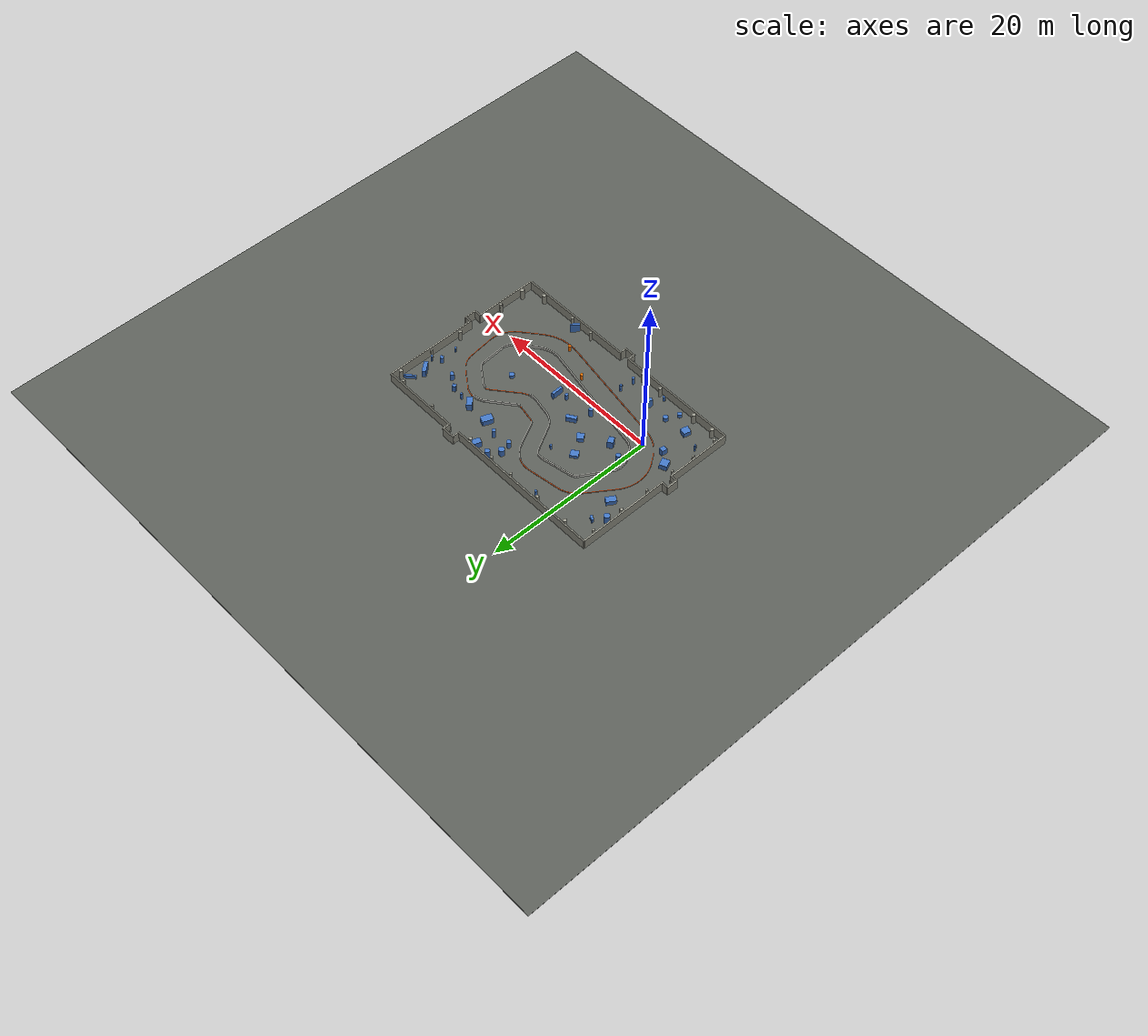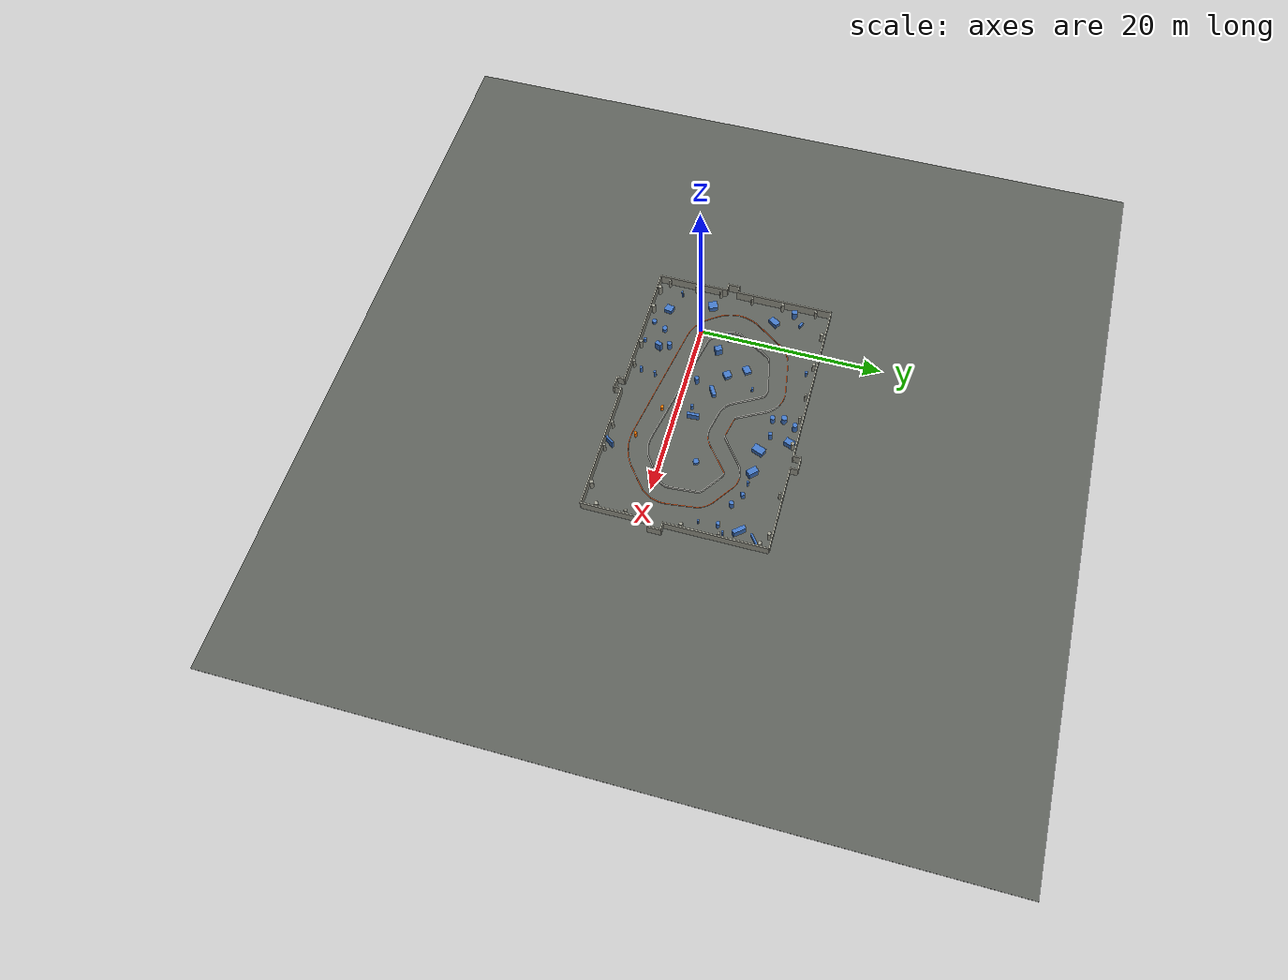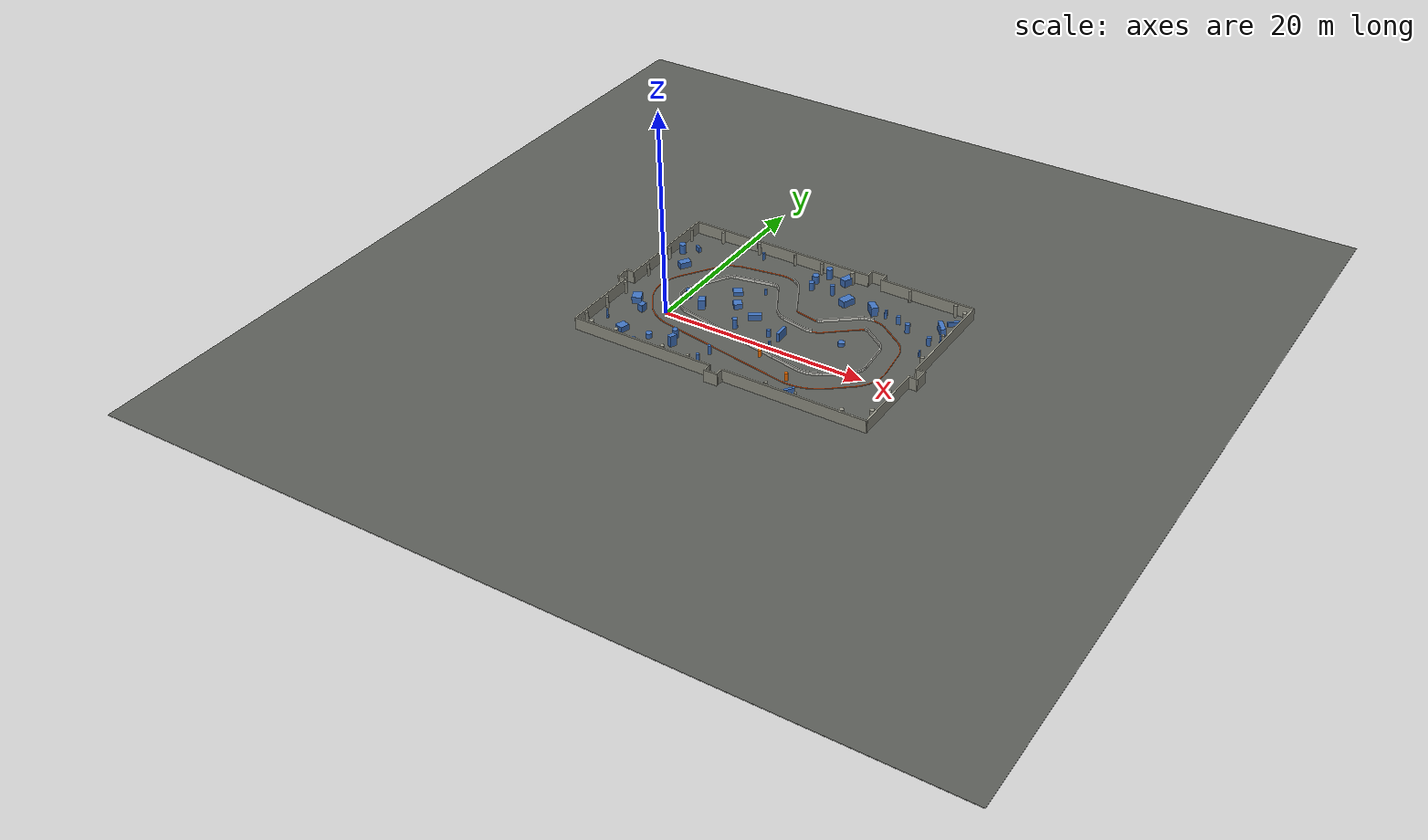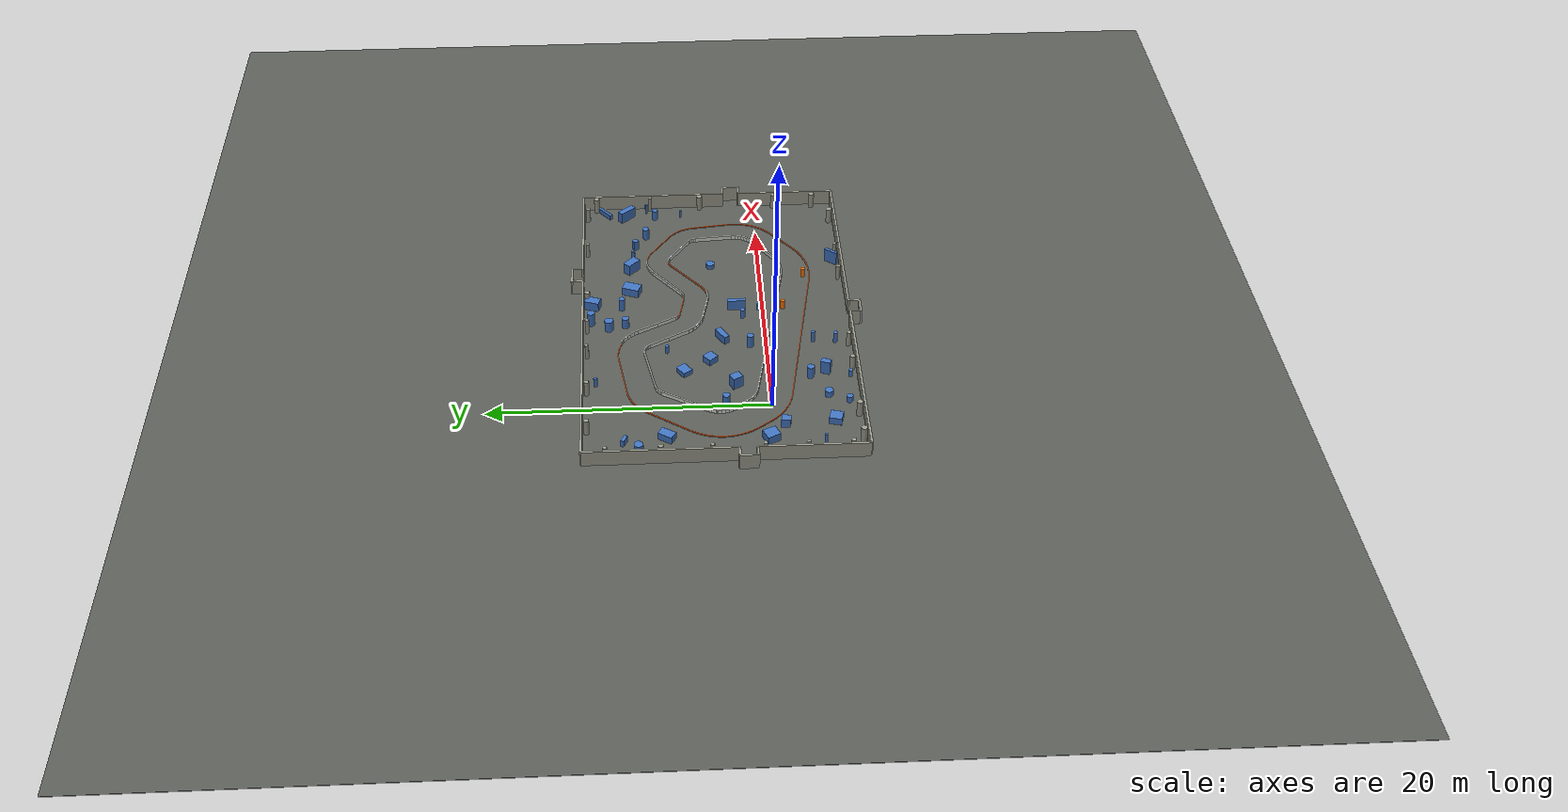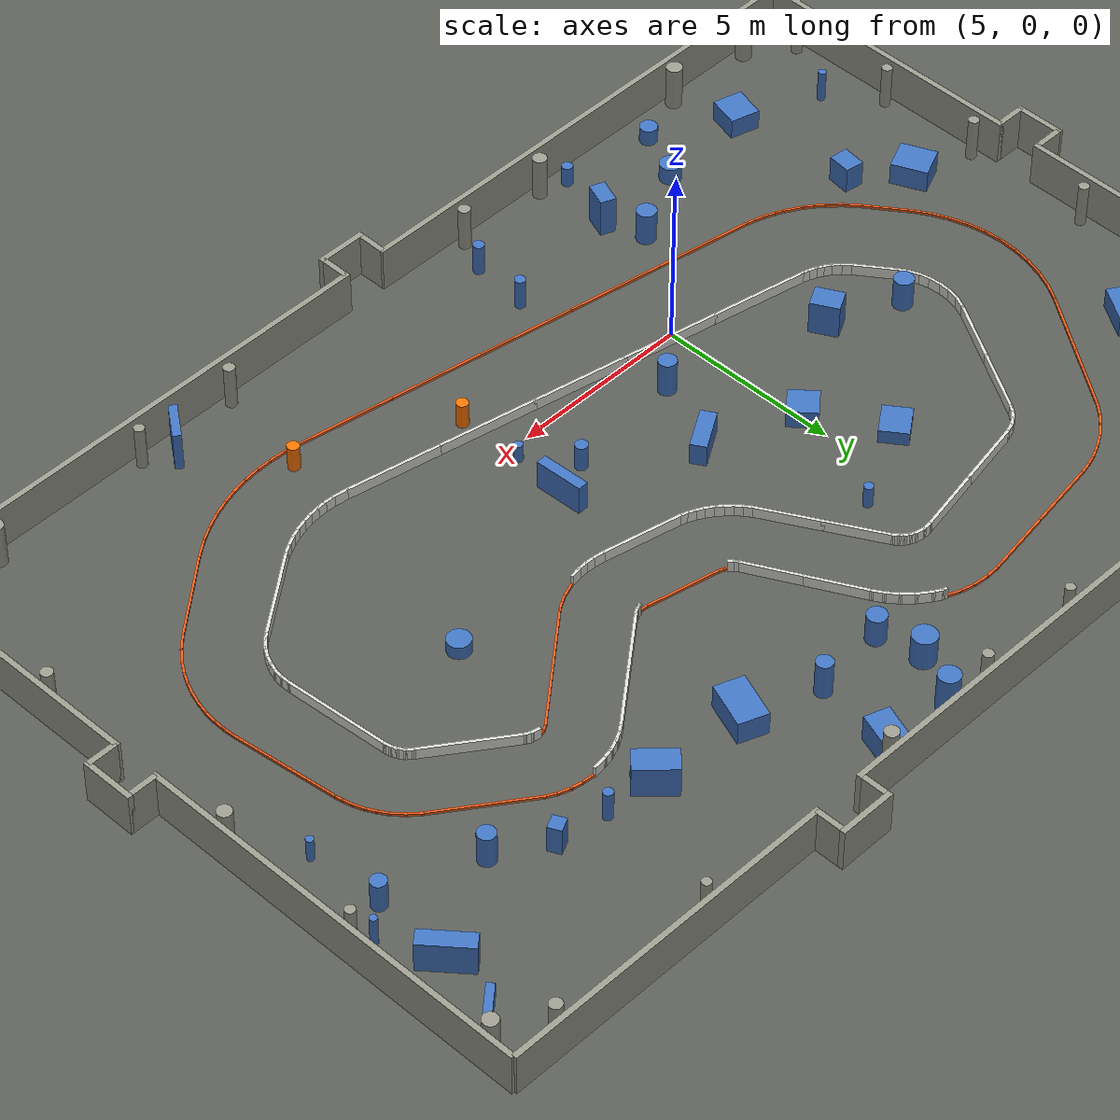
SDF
<?xml version="1.0" ?>
<sdf version="1.9">
  <!-- Generated by simulation/tools/generate_pose_dataset.py --install-gazebo-worlds from tools/pose_dataset/config/tracks.yaml (test_unseen). Do not edit by hand: change the YAML and regenerate. -->
  <world name="default">
    <physics name="default_physics" type="dart">
      <max_step_size>0.001</max_step_size>
      <real_time_factor>1.0</real_time_factor>
      <real_time_update_rate>1000.0</real_time_update_rate>
    </physics>
    <plugin filename="gz-sim-physics-system" name="gz::sim::systems::Physics" />
    <plugin filename="gz-sim-user-commands-system" name="gz::sim::systems::UserCommands" />
    <plugin filename="gz-sim-scene-broadcaster-system" name="gz::sim::systems::SceneBroadcaster" />
    <plugin filename="gz-sim-imu-system" name="gz::sim::systems::Imu" />
    <plugin filename="gz-sim-sensors-system" name="gz::sim::systems::Sensors">
      <render_engine>ogre2</render_engine>
    </plugin>
    <light type="directional" name="sun">
      <pose>0 0 10 0 0 0</pose>
      <diffuse>0.8 0.8 0.8 1</diffuse>
      <direction>-0.5 0.5 -1</direction>
      <cast_shadows>true</cast_shadows>
    </light>
    <model name="track_curb">
      <static>true</static>
      <pose>0 0 0 0 0 0</pose>
      <link name="curb_link">
        <collision name="left0_0_0_collision">
          <pose>16.445524 6.797430 0.035000 0.000000 0.000000 -2.932960</pose>
          <geometry>
            <box>
              <size>0.229098 0.060000 0.070000</size>
            </box>
          </geometry>
        </collision>
        <visual name="left0_0_0_visual">
          <pose>16.445524 6.797430 0.035000 0.000000 0.000000 -2.932960</pose>
          <geometry>
            <box>
              <size>0.229098 0.060000 0.070000</size>
            </box>
          </geometry>
          <material>
            <ambient>0.9 0.35 0.1 1</ambient>
            <diffuse>0.9 0.35 0.1 1</diffuse>
          </material>
        </visual>
        <collision name="left0_1_0_collision">
          <pose>16.289475 6.739123 0.035000 0.000000 0.000000 -2.633929</pose>
          <geometry>
            <box>
              <size>0.227833 0.060000 0.070000</size>
            </box>
          </geometry>
        </collision>
        <visual name="left0_1_0_visual">
          <pose>16.289475 6.739123 0.035000 0.000000 0.000000 -2.633929</pose>
          <geometry>
            <box>
              <size>0.227833 0.060000 0.070000</size>
            </box>
          </geometry>
          <material>
            <ambient>0.9 0.35 0.1 1</ambient>
            <diffuse>0.9 0.35 0.1 1</diffuse>
          </material>
        </visual>
        <collision name="left0_2_0_collision">
          <pose>15.530823 6.140468 0.035000 0.000000 0.000000 -2.458364</pose>
          <geometry>
            <box>
              <size>1.827338 0.060000 0.070000</size>
            </box>
          </geometry>
        </collision>
        <visual name="left0_2_0_visual">
          <pose>15.530823 6.140468 0.035000 0.000000 0.000000 -2.458364</pose>
          <geometry>
            <box>
              <size>1.827338 0.060000 0.070000</size>
            </box>
          </geometry>
          <material>
            <ambient>0.9 0.35 0.1 1</ambient>
            <diffuse>0.9 0.35 0.1 1</diffuse>
          </material>
        </visual>
        <collision name="left0_2_1_collision">
          <pose>14.160184 5.024747 0.035000 0.000000 0.000000 -2.458364</pose>
          <geometry>
            <box>
              <size>1.827338 0.060000 0.070000</size>
            </box>
          </geometry>
        </collision>
        <visual name="left0_2_1_visual">
          <pose>14.160184 5.024747 0.035000 0.000000 0.000000 -2.458364</pose>
          <geometry>
            <box>
              <size>1.827338 0.060000 0.070000</size>
            </box>
          </geometry>
          <material>
            <ambient>0.9 0.35 0.1 1</ambient>
            <diffuse>0.9 0.35 0.1 1</diffuse>
          </material>
        </visual>
        <collision name="left0_3_0_collision">
          <pose>13.382528 4.407827 0.035000 0.000000 0.000000 -2.572562</pose>
          <geometry>
            <box>
              <size>0.279217 0.060000 0.070000</size>
            </box>
          </geometry>
        </collision>
        <visual name="left0_3_0_visual">
          <pose>13.382528 4.407827 0.035000 0.000000 0.000000 -2.572562</pose>
          <geometry>
            <box>
              <size>0.279217 0.060000 0.070000</size>
            </box>
          </geometry>
          <material>
            <ambient>0.9 0.35 0.1 1</ambient>
            <diffuse>0.9 0.35 0.1 1</diffuse>
          </material>
        </visual>
        <collision name="left0_4_0_collision">
          <pose>13.192745 4.298446 0.035000 0.000000 0.000000 -2.664899</pose>
          <geometry>
            <box>
              <size>0.279346 0.060000 0.070000</size>
            </box>
          </geometry>
        </collision>
        <visual name="left0_4_0_visual">
          <pose>13.192745 4.298446 0.035000 0.000000 0.000000 -2.664899</pose>
          <geometry>
            <box>
              <size>0.279346 0.060000 0.070000</size>
            </box>
          </geometry>
          <material>
            <ambient>0.9 0.35 0.1 1</ambient>
            <diffuse>0.9 0.35 0.1 1</diffuse>
          </material>
        </visual>
        <collision name="left0_5_0_collision">
          <pose>12.874273 4.166821 0.035000 0.000000 0.000000 -2.789113</pose>
          <geometry>
            <box>
              <size>0.531009 0.060000 0.070000</size>
            </box>
          </geometry>
        </collision>
        <visual name="left0_5_0_visual">
          <pose>12.874273 4.166821 0.035000 0.000000 0.000000 -2.789113</pose>
          <geometry>
            <box>
              <size>0.531009 0.060000 0.070000</size>
            </box>
          </geometry>
          <material>
            <ambient>0.9 0.35 0.1 1</ambient>
            <diffuse>0.9 0.35 0.1 1</diffuse>
          </material>
        </visual>
        <collision name="right1_0_0_collision">
          <pose>12.195429 5.802627 0.035000 0.000000 0.000000 -3.014258</pose>
          <geometry>
            <box>
              <size>0.182472 0.060000 0.070000</size>
            </box>
          </geometry>
        </collision>
        <visual name="right1_0_0_visual">
          <pose>12.195429 5.802627 0.035000 0.000000 0.000000 -3.014258</pose>
          <geometry>
            <box>
              <size>0.182472 0.060000 0.070000</size>
            </box>
          </geometry>
          <material>
            <ambient>0.9 0.35 0.1 1</ambient>
            <diffuse>0.9 0.35 0.1 1</diffuse>
          </material>
        </visual>
        <collision name="right1_1_0_collision">
          <pose>12.069579 5.799882 0.035000 0.000000 0.000000 3.064475</pose>
          <geometry>
            <box>
              <size>0.190607 0.060000 0.070000</size>
            </box>
          </geometry>
        </collision>
        <visual name="right1_1_0_visual">
          <pose>12.069579 5.799882 0.035000 0.000000 0.000000 3.064475</pose>
          <geometry>
            <box>
              <size>0.190607 0.060000 0.070000</size>
            </box>
          </geometry>
          <material>
            <ambient>0.9 0.35 0.1 1</ambient>
            <diffuse>0.9 0.35 0.1 1</diffuse>
          </material>
        </visual>
        <collision name="right1_2_0_collision">
          <pose>11.036696 6.010086 0.035000 0.000000 0.000000 2.932681</pose>
          <geometry>
            <box>
              <size>2.038567 0.060000 0.070000</size>
            </box>
          </geometry>
        </collision>
        <visual name="right1_2_0_visual">
          <pose>11.036696 6.010086 0.035000 0.000000 0.000000 2.932681</pose>
          <geometry>
            <box>
              <size>2.038567 0.060000 0.070000</size>
            </box>
          </geometry>
          <material>
            <ambient>0.9 0.35 0.1 1</ambient>
            <diffuse>0.9 0.35 0.1 1</diffuse>
          </material>
        </visual>
        <collision name="right1_3_0_collision">
          <pose>9.990548 6.242880 0.035000 0.000000 0.000000 2.802749</pose>
          <geometry>
            <box>
              <size>0.226199 0.060000 0.070000</size>
            </box>
          </geometry>
        </collision>
        <visual name="right1_3_0_visual">
          <pose>9.990548 6.242880 0.035000 0.000000 0.000000 2.802749</pose>
          <geometry>
            <box>
              <size>0.226199 0.060000 0.070000</size>
            </box>
          </geometry>
          <material>
            <ambient>0.9 0.35 0.1 1</ambient>
            <diffuse>0.9 0.35 0.1 1</diffuse>
          </material>
        </visual>
        <collision name="right1_4_0_collision">
          <pose>9.867100 6.298703 0.035000 0.000000 0.000000 2.582522</pose>
          <geometry>
            <box>
              <size>0.166336 0.060000 0.070000</size>
            </box>
          </geometry>
        </collision>
        <visual name="right1_4_0_visual">
          <pose>9.867100 6.298703 0.035000 0.000000 0.000000 2.582522</pose>
          <geometry>
            <box>
              <size>0.166336 0.060000 0.070000</size>
            </box>
          </geometry>
          <material>
            <ambient>0.9 0.35 0.1 1</ambient>
            <diffuse>0.9 0.35 0.1 1</diffuse>
          </material>
        </visual>
        <collision name="right1_5_0_collision">
          <pose>9.821891 6.333422 0.035000 0.000000 0.000000 1.591638</pose>
          <geometry>
            <box>
              <size>0.073041 0.060000 0.070000</size>
            </box>
          </geometry>
        </collision>
        <visual name="right1_5_0_visual">
          <pose>9.821891 6.333422 0.035000 0.000000 0.000000 1.591638</pose>
          <geometry>
            <box>
              <size>0.073041 0.060000 0.070000</size>
            </box>
          </geometry>
          <material>
            <ambient>0.9 0.35 0.1 1</ambient>
            <diffuse>0.9 0.35 0.1 1</diffuse>
          </material>
        </visual>
        <collision name="right3_0_0_collision">
          <pose>6.828390 10.538684 0.035000 0.000000 0.000000 2.752442</pose>
          <geometry>
            <box>
              <size>0.453125 0.060000 0.070000</size>
            </box>
          </geometry>
        </collision>
        <visual name="right3_0_0_visual">
          <pose>6.828390 10.538684 0.035000 0.000000 0.000000 2.752442</pose>
          <geometry>
            <box>
              <size>0.453125 0.060000 0.070000</size>
            </box>
          </geometry>
          <material>
            <ambient>0.9 0.35 0.1 1</ambient>
            <diffuse>0.9 0.35 0.1 1</diffuse>
          </material>
        </visual>
        <collision name="right3_1_0_collision">
          <pose>6.455519 10.661045 0.035000 0.000000 0.000000 2.896448</pose>
          <geometry>
            <box>
              <size>0.453784 0.060000 0.070000</size>
            </box>
          </geometry>
        </collision>
        <visual name="right3_1_0_visual">
          <pose>6.455519 10.661045 0.035000 0.000000 0.000000 2.896448</pose>
          <geometry>
            <box>
              <size>0.453784 0.060000 0.070000</size>
            </box>
          </geometry>
          <material>
            <ambient>0.9 0.35 0.1 1</ambient>
            <diffuse>0.9 0.35 0.1 1</diffuse>
          </material>
        </visual>
        <collision name="right3_2_0_collision">
          <pose>6.068299 10.728743 0.035000 0.000000 0.000000 3.040454</pose>
          <geometry>
            <box>
              <size>0.454444 0.060000 0.070000</size>
            </box>
          </geometry>
        </collision>
        <visual name="right3_2_0_visual">
          <pose>6.068299 10.728743 0.035000 0.000000 0.000000 3.040454</pose>
          <geometry>
            <box>
              <size>0.454444 0.060000 0.070000</size>
            </box>
          </geometry>
          <material>
            <ambient>0.9 0.35 0.1 1</ambient>
            <diffuse>0.9 0.35 0.1 1</diffuse>
          </material>
        </visual>
        <collision name="right3_3_0_collision">
          <pose>5.689845 10.741851 0.035000 0.000000 0.000000 -3.104267</pose>
          <geometry>
            <box>
              <size>0.424734 0.060000 0.070000</size>
            </box>
          </geometry>
        </collision>
        <visual name="right3_3_0_visual">
          <pose>5.689845 10.741851 0.035000 0.000000 0.000000 -3.104267</pose>
          <geometry>
            <box>
              <size>0.424734 0.060000 0.070000</size>
            </box>
          </geometry>
          <material>
            <ambient>0.9 0.35 0.1 1</ambient>
            <diffuse>0.9 0.35 0.1 1</diffuse>
          </material>
        </visual>
        <collision name="right3_4_0_collision">
          <pose>4.556007 10.588662 0.035000 0.000000 0.000000 -2.988960</pose>
          <geometry>
            <box>
              <size>1.985583 0.060000 0.070000</size>
            </box>
          </geometry>
        </collision>
        <visual name="right3_4_0_visual">
          <pose>4.556007 10.588662 0.035000 0.000000 0.000000 -2.988960</pose>
          <geometry>
            <box>
              <size>1.985583 0.060000 0.070000</size>
            </box>
          </geometry>
          <material>
            <ambient>0.9 0.35 0.1 1</ambient>
            <diffuse>0.9 0.35 0.1 1</diffuse>
          </material>
        </visual>
        <collision name="right3_4_1_collision">
          <pose>2.652810 10.295895 0.035000 0.000000 0.000000 -2.988960</pose>
          <geometry>
            <box>
              <size>1.985583 0.060000 0.070000</size>
            </box>
          </geometry>
        </collision>
        <visual name="right3_4_1_visual">
          <pose>2.652810 10.295895 0.035000 0.000000 0.000000 -2.988960</pose>
          <geometry>
            <box>
              <size>1.985583 0.060000 0.070000</size>
            </box>
          </geometry>
          <material>
            <ambient>0.9 0.35 0.1 1</ambient>
            <diffuse>0.9 0.35 0.1 1</diffuse>
          </material>
        </visual>
        <collision name="right3_5_0_collision">
          <pose>1.573484 10.120065 0.035000 0.000000 0.000000 -2.915013</pose>
          <geometry>
            <box>
              <size>0.322155 0.060000 0.070000</size>
            </box>
          </geometry>
        </collision>
        <visual name="right3_5_0_visual">
          <pose>1.573484 10.120065 0.035000 0.000000 0.000000 -2.915013</pose>
          <geometry>
            <box>
              <size>0.322155 0.060000 0.070000</size>
            </box>
          </geometry>
          <material>
            <ambient>0.9 0.35 0.1 1</ambient>
            <diffuse>0.9 0.35 0.1 1</diffuse>
          </material>
        </visual>
        <collision name="right3_6_0_collision">
          <pose>1.334462 10.055754 0.035000 0.000000 0.000000 -2.838010</pose>
          <geometry>
            <box>
              <size>0.293257 0.060000 0.070000</size>
            </box>
          </geometry>
        </collision>
        <visual name="right3_6_0_visual">
          <pose>1.334462 10.055754 0.035000 0.000000 0.000000 -2.838010</pose>
          <geometry>
            <box>
              <size>0.293257 0.060000 0.070000</size>
            </box>
          </geometry>
          <material>
            <ambient>0.9 0.35 0.1 1</ambient>
            <diffuse>0.9 0.35 0.1 1</diffuse>
          </material>
        </visual>
        <collision name="right3_7_0_collision">
          <pose>1.114593 9.978019 0.035000 0.000000 0.000000 -2.765536</pose>
          <geometry>
            <box>
              <size>0.293462 0.060000 0.070000</size>
            </box>
          </geometry>
        </collision>
        <visual name="right3_7_0_visual">
          <pose>1.114593 9.978019 0.035000 0.000000 0.000000 -2.765536</pose>
          <geometry>
            <box>
              <size>0.293462 0.060000 0.070000</size>
            </box>
          </geometry>
          <material>
            <ambient>0.9 0.35 0.1 1</ambient>
            <diffuse>0.9 0.35 0.1 1</diffuse>
          </material>
        </visual>
        <collision name="right3_8_0_collision">
          <pose>0.900743 9.884485 0.035000 0.000000 0.000000 -2.693062</pose>
          <geometry>
            <box>
              <size>0.293666 0.060000 0.070000</size>
            </box>
          </geometry>
        </collision>
        <visual name="right3_8_0_visual">
          <pose>0.900743 9.884485 0.035000 0.000000 0.000000 -2.693062</pose>
          <geometry>
            <box>
              <size>0.293666 0.060000 0.070000</size>
            </box>
          </geometry>
          <material>
            <ambient>0.9 0.35 0.1 1</ambient>
            <diffuse>0.9 0.35 0.1 1</diffuse>
          </material>
        </visual>
        <collision name="right3_9_0_collision">
          <pose>0.644788 9.744014 0.035000 0.000000 0.000000 -2.604100</pose>
          <geometry>
            <box>
              <size>0.410824 0.060000 0.070000</size>
            </box>
          </geometry>
        </collision>
        <visual name="right3_9_0_visual">
          <pose>0.644788 9.744014 0.035000 0.000000 0.000000 -2.604100</pose>
          <geometry>
            <box>
              <size>0.410824 0.060000 0.070000</size>
            </box>
          </geometry>
          <material>
            <ambient>0.9 0.35 0.1 1</ambient>
            <diffuse>0.9 0.35 0.1 1</diffuse>
          </material>
        </visual>
        <collision name="right3_10_0_collision">
          <pose>0.352912 9.549512 0.035000 0.000000 0.000000 -2.503573</pose>
          <geometry>
            <box>
              <size>0.411554 0.060000 0.070000</size>
            </box>
          </geometry>
        </collision>
        <visual name="right3_10_0_visual">
          <pose>0.352912 9.549512 0.035000 0.000000 0.000000 -2.503573</pose>
          <geometry>
            <box>
              <size>0.411554 0.060000 0.070000</size>
            </box>
          </geometry>
          <material>
            <ambient>0.9 0.35 0.1 1</ambient>
            <diffuse>0.9 0.35 0.1 1</diffuse>
          </material>
        </visual>
        <collision name="right3_11_0_collision">
          <pose>0.082407 9.325134 0.035000 0.000000 0.000000 -2.394826</pose>
          <geometry>
            <box>
              <size>0.412390 0.060000 0.070000</size>
            </box>
          </geometry>
        </collision>
        <visual name="right3_11_0_visual">
          <pose>0.082407 9.325134 0.035000 0.000000 0.000000 -2.394826</pose>
          <geometry>
            <box>
              <size>0.412390 0.060000 0.070000</size>
            </box>
          </geometry>
          <material>
            <ambient>0.9 0.35 0.1 1</ambient>
            <diffuse>0.9 0.35 0.1 1</diffuse>
          </material>
        </visual>
        <collision name="right3_12_0_collision">
          <pose>-0.162728 9.072124 0.035000 0.000000 0.000000 -2.286079</pose>
          <geometry>
            <box>
              <size>0.413225 0.060000 0.070000</size>
            </box>
          </geometry>
        </collision>
        <visual name="right3_12_0_visual">
          <pose>-0.162728 9.072124 0.035000 0.000000 0.000000 -2.286079</pose>
          <geometry>
            <box>
              <size>0.413225 0.060000 0.070000</size>
            </box>
          </geometry>
          <material>
            <ambient>0.9 0.35 0.1 1</ambient>
            <diffuse>0.9 0.35 0.1 1</diffuse>
          </material>
        </visual>
        <collision name="right3_13_0_collision">
          <pose>-0.809885 8.162956 0.035000 0.000000 0.000000 -2.171276</pose>
          <geometry>
            <box>
              <size>1.940683 0.060000 0.070000</size>
            </box>
          </geometry>
        </collision>
        <visual name="right3_13_0_visual">
          <pose>-0.809885 8.162956 0.035000 0.000000 0.000000 -2.171276</pose>
          <geometry>
            <box>
              <size>1.940683 0.060000 0.070000</size>
            </box>
          </geometry>
          <material>
            <ambient>0.9 0.35 0.1 1</ambient>
            <diffuse>0.9 0.35 0.1 1</diffuse>
          </material>
        </visual>
        <collision name="right3_13_1_collision">
          <pose>-1.872543 6.611271 0.035000 0.000000 0.000000 -2.171276</pose>
          <geometry>
            <box>
              <size>1.940683 0.060000 0.070000</size>
            </box>
          </geometry>
        </collision>
        <visual name="right3_13_1_visual">
          <pose>-1.872543 6.611271 0.035000 0.000000 0.000000 -2.171276</pose>
          <geometry>
            <box>
              <size>1.940683 0.060000 0.070000</size>
            </box>
          </geometry>
          <material>
            <ambient>0.9 0.35 0.1 1</ambient>
            <diffuse>0.9 0.35 0.1 1</diffuse>
          </material>
        </visual>
        <collision name="right3_14_0_collision">
          <pose>-2.523070 5.633518 0.035000 0.000000 0.000000 -2.104089</pose>
          <geometry>
            <box>
              <size>0.528938 0.060000 0.070000</size>
            </box>
          </geometry>
        </collision>
        <visual name="right3_14_0_visual">
          <pose>-2.523070 5.633518 0.035000 0.000000 0.000000 -2.104089</pose>
          <geometry>
            <box>
              <size>0.528938 0.060000 0.070000</size>
            </box>
          </geometry>
          <material>
            <ambient>0.9 0.35 0.1 1</ambient>
            <diffuse>0.9 0.35 0.1 1</diffuse>
          </material>
        </visual>
        <collision name="right3_15_0_collision">
          <pose>-2.743571 5.203117 0.035000 0.000000 0.000000 -1.988114</pose>
          <geometry>
            <box>
              <size>0.559883 0.060000 0.070000</size>
            </box>
          </geometry>
        </collision>
        <visual name="right3_15_0_visual">
          <pose>-2.743571 5.203117 0.035000 0.000000 0.000000 -1.988114</pose>
          <geometry>
            <box>
              <size>0.559883 0.060000 0.070000</size>
            </box>
          </geometry>
          <material>
            <ambient>0.9 0.35 0.1 1</ambient>
            <diffuse>0.9 0.35 0.1 1</diffuse>
          </material>
        </visual>
        <collision name="right3_16_0_collision">
          <pose>-2.918436 4.735036 0.035000 0.000000 0.000000 -1.868690</pose>
          <geometry>
            <box>
              <size>0.561256 0.060000 0.070000</size>
            </box>
          </geometry>
        </collision>
        <visual name="right3_16_0_visual">
          <pose>-2.918436 4.735036 0.035000 0.000000 0.000000 -1.868690</pose>
          <geometry>
            <box>
              <size>0.561256 0.060000 0.070000</size>
            </box>
          </geometry>
          <material>
            <ambient>0.9 0.35 0.1 1</ambient>
            <diffuse>0.9 0.35 0.1 1</diffuse>
          </material>
        </visual>
        <collision name="right3_17_0_collision">
          <pose>-3.036611 4.248123 0.035000 0.000000 0.000000 -1.749266</pose>
          <geometry>
            <box>
              <size>0.562630 0.060000 0.070000</size>
            </box>
          </geometry>
        </collision>
        <visual name="right3_17_0_visual">
          <pose>-3.036611 4.248123 0.035000 0.000000 0.000000 -1.749266</pose>
          <geometry>
            <box>
              <size>0.562630 0.060000 0.070000</size>
            </box>
          </geometry>
          <material>
            <ambient>0.9 0.35 0.1 1</ambient>
            <diffuse>0.9 0.35 0.1 1</diffuse>
          </material>
        </visual>
        <collision name="right3_18_0_collision">
          <pose>-3.096097 3.749238 0.035000 0.000000 0.000000 -1.629843</pose>
          <geometry>
            <box>
              <size>0.564003 0.060000 0.070000</size>
            </box>
          </geometry>
        </collision>
        <visual name="right3_18_0_visual">
          <pose>-3.096097 3.749238 0.035000 0.000000 0.000000 -1.629843</pose>
          <geometry>
            <box>
              <size>0.564003 0.060000 0.070000</size>
            </box>
          </geometry>
          <material>
            <ambient>0.9 0.35 0.1 1</ambient>
            <diffuse>0.9 0.35 0.1 1</diffuse>
          </material>
        </visual>
        <collision name="right3_19_0_collision">
          <pose>-3.092131 3.260133 0.035000 0.000000 0.000000 -1.491662</pose>
          <geometry>
            <box>
              <size>0.536577 0.060000 0.070000</size>
            </box>
          </geometry>
        </collision>
        <visual name="right3_19_0_visual">
          <pose>-3.092131 3.260133 0.035000 0.000000 0.000000 -1.491662</pose>
          <geometry>
            <box>
              <size>0.536577 0.060000 0.070000</size>
            </box>
          </geometry>
          <material>
            <ambient>0.9 0.35 0.1 1</ambient>
            <diffuse>0.9 0.35 0.1 1</diffuse>
          </material>
        </visual>
        <collision name="right3_20_0_collision">
          <pose>-3.027695 2.788696 0.035000 0.000000 0.000000 -1.378257</pose>
          <geometry>
            <box>
              <size>0.536595 0.060000 0.070000</size>
            </box>
          </geometry>
        </collision>
        <visual name="right3_20_0_visual">
          <pose>-3.027695 2.788696 0.035000 0.000000 0.000000 -1.378257</pose>
          <geometry>
            <box>
              <size>0.536595 0.060000 0.070000</size>
            </box>
          </geometry>
          <material>
            <ambient>0.9 0.35 0.1 1</ambient>
            <diffuse>0.9 0.35 0.1 1</diffuse>
          </material>
        </visual>
        <collision name="right3_21_0_collision">
          <pose>-2.910476 2.327522 0.035000 0.000000 0.000000 -1.265527</pose>
          <geometry>
            <box>
              <size>0.536595 0.060000 0.070000</size>
            </box>
          </geometry>
        </collision>
        <visual name="right3_21_0_visual">
          <pose>-2.910476 2.327522 0.035000 0.000000 0.000000 -1.265527</pose>
          <geometry>
            <box>
              <size>0.536595 0.060000 0.070000</size>
            </box>
          </geometry>
          <material>
            <ambient>0.9 0.35 0.1 1</ambient>
            <diffuse>0.9 0.35 0.1 1</diffuse>
          </material>
        </visual>
        <collision name="right3_22_0_collision">
          <pose>-2.742124 1.882462 0.035000 0.000000 0.000000 -1.152797</pose>
          <geometry>
            <box>
              <size>0.536595 0.060000 0.070000</size>
            </box>
          </geometry>
        </collision>
        <visual name="right3_22_0_visual">
          <pose>-2.742124 1.882462 0.035000 0.000000 0.000000 -1.152797</pose>
          <geometry>
            <box>
              <size>0.536595 0.060000 0.070000</size>
            </box>
          </geometry>
          <material>
            <ambient>0.9 0.35 0.1 1</ambient>
            <diffuse>0.9 0.35 0.1 1</diffuse>
          </material>
        </visual>
        <collision name="right3_23_0_collision">
          <pose>-2.516966 1.447514 0.035000 0.000000 0.000000 -1.036752</pose>
          <geometry>
            <box>
              <size>0.564597 0.060000 0.070000</size>
            </box>
          </geometry>
        </collision>
        <visual name="right3_23_0_visual">
          <pose>-2.516966 1.447514 0.035000 0.000000 0.000000 -1.036752</pose>
          <geometry>
            <box>
              <size>0.564597 0.060000 0.070000</size>
            </box>
          </geometry>
          <material>
            <ambient>0.9 0.35 0.1 1</ambient>
            <diffuse>0.9 0.35 0.1 1</diffuse>
          </material>
        </visual>
        <collision name="right3_24_0_collision">
          <pose>-2.012254 0.703552 0.035000 0.000000 0.000000 -0.950539</pose>
          <geometry>
            <box>
              <size>1.354766 0.060000 0.070000</size>
            </box>
          </geometry>
        </collision>
        <visual name="right3_24_0_visual">
          <pose>-2.012254 0.703552 0.035000 0.000000 0.000000 -0.950539</pose>
          <geometry>
            <box>
              <size>1.354766 0.060000 0.070000</size>
            </box>
          </geometry>
          <material>
            <ambient>0.9 0.35 0.1 1</ambient>
            <diffuse>0.9 0.35 0.1 1</diffuse>
          </material>
        </visual>
        <collision name="right3_25_0_collision">
          <pose>-1.500553 0.014932 0.035000 0.000000 0.000000 -0.874027</pose>
          <geometry>
            <box>
              <size>0.482015 0.060000 0.070000</size>
            </box>
          </geometry>
        </collision>
        <visual name="right3_25_0_visual">
          <pose>-1.500553 0.014932 0.035000 0.000000 0.000000 -0.874027</pose>
          <geometry>
            <box>
              <size>0.482015 0.060000 0.070000</size>
            </box>
          </geometry>
          <material>
            <ambient>0.9 0.35 0.1 1</ambient>
            <diffuse>0.9 0.35 0.1 1</diffuse>
          </material>
        </visual>
        <collision name="right3_26_0_collision">
          <pose>-1.203706 -0.303711 0.035000 0.000000 0.000000 -0.770891</pose>
          <geometry>
            <box>
              <size>0.510124 0.060000 0.070000</size>
            </box>
          </geometry>
        </collision>
        <visual name="right3_26_0_visual">
          <pose>-1.203706 -0.303711 0.035000 0.000000 0.000000 -0.770891</pose>
          <geometry>
            <box>
              <size>0.510124 0.060000 0.070000</size>
            </box>
          </geometry>
          <material>
            <ambient>0.9 0.35 0.1 1</ambient>
            <diffuse>0.9 0.35 0.1 1</diffuse>
          </material>
        </visual>
        <collision name="right3_27_0_collision">
          <pose>-0.933253 -0.549482 0.035000 0.000000 0.000000 -0.684391</pose>
          <geometry>
            <box>
              <size>0.341408 0.060000 0.070000</size>
            </box>
          </geometry>
        </collision>
        <visual name="right3_27_0_visual">
          <pose>-0.933253 -0.549482 0.035000 0.000000 0.000000 -0.684391</pose>
          <geometry>
            <box>
              <size>0.341408 0.060000 0.070000</size>
            </box>
          </geometry>
          <material>
            <ambient>0.9 0.35 0.1 1</ambient>
            <diffuse>0.9 0.35 0.1 1</diffuse>
          </material>
        </visual>
        <collision name="right3_28_0_collision">
          <pose>-0.709544 -0.719943 0.035000 0.000000 0.000000 -0.617852</pose>
          <geometry>
            <box>
              <size>0.341408 0.060000 0.070000</size>
            </box>
          </geometry>
        </collision>
        <visual name="right3_28_0_visual">
          <pose>-0.709544 -0.719943 0.035000 0.000000 0.000000 -0.617852</pose>
          <geometry>
            <box>
              <size>0.341408 0.060000 0.070000</size>
            </box>
          </geometry>
          <material>
            <ambient>0.9 0.35 0.1 1</ambient>
            <diffuse>0.9 0.35 0.1 1</diffuse>
          </material>
        </visual>
        <collision name="right3_29_0_collision">
          <pose>-0.374885 -0.926556 0.035000 0.000000 0.000000 -0.517121</pose>
          <geometry>
            <box>
              <size>0.566110 0.060000 0.070000</size>
            </box>
          </geometry>
        </collision>
        <visual name="right3_29_0_visual">
          <pose>-0.374885 -0.926556 0.035000 0.000000 0.000000 -0.517121</pose>
          <geometry>
            <box>
              <size>0.566110 0.060000 0.070000</size>
            </box>
          </geometry>
          <material>
            <ambient>0.9 0.35 0.1 1</ambient>
            <diffuse>0.9 0.35 0.1 1</diffuse>
          </material>
        </visual>
        <collision name="right3_30_0_collision">
          <pose>-0.039731 -1.103939 0.035000 0.000000 0.000000 -0.426054</pose>
          <geometry>
            <box>
              <size>0.312989 0.060000 0.070000</size>
            </box>
          </geometry>
        </collision>
        <visual name="right3_30_0_visual">
          <pose>-0.039731 -1.103939 0.035000 0.000000 0.000000 -0.426054</pose>
          <geometry>
            <box>
              <size>0.312989 0.060000 0.070000</size>
            </box>
          </geometry>
          <material>
            <ambient>0.9 0.35 0.1 1</ambient>
            <diffuse>0.9 0.35 0.1 1</diffuse>
          </material>
        </visual>
        <collision name="right3_31_0_collision">
          <pose>0.206776 -1.206073 0.035000 0.000000 0.000000 -0.362838</pose>
          <geometry>
            <box>
              <size>0.340933 0.060000 0.070000</size>
            </box>
          </geometry>
        </collision>
        <visual name="right3_31_0_visual">
          <pose>0.206776 -1.206073 0.035000 0.000000 0.000000 -0.362838</pose>
          <geometry>
            <box>
              <size>0.340933 0.060000 0.070000</size>
            </box>
          </geometry>
          <material>
            <ambient>0.9 0.35 0.1 1</ambient>
            <diffuse>0.9 0.35 0.1 1</diffuse>
          </material>
        </visual>
        <collision name="right3_32_0_collision">
          <pose>0.458821 -1.293222 0.035000 0.000000 0.000000 -0.299620</pose>
          <geometry>
            <box>
              <size>0.312707 0.060000 0.070000</size>
            </box>
          </geometry>
        </collision>
        <visual name="right3_32_0_visual">
          <pose>0.458821 -1.293222 0.035000 0.000000 0.000000 -0.299620</pose>
          <geometry>
            <box>
              <size>0.312707 0.060000 0.070000</size>
            </box>
          </geometry>
          <material>
            <ambient>0.9 0.35 0.1 1</ambient>
            <diffuse>0.9 0.35 0.1 1</diffuse>
          </material>
        </visual>
        <collision name="right3_33_0_collision">
          <pose>0.715953 -1.363378 0.035000 0.000000 0.000000 -0.236404</pose>
          <geometry>
            <box>
              <size>0.340619 0.060000 0.070000</size>
            </box>
          </geometry>
        </collision>
        <visual name="right3_33_0_visual">
          <pose>0.715953 -1.363378 0.035000 0.000000 0.000000 -0.236404</pose>
          <geometry>
            <box>
              <size>0.340619 0.060000 0.070000</size>
            </box>
          </geometry>
          <material>
            <ambient>0.9 0.35 0.1 1</ambient>
            <diffuse>0.9 0.35 0.1 1</diffuse>
          </material>
        </visual>
        <collision name="right3_34_0_collision">
          <pose>2.164263 -1.625589 0.035000 0.000000 0.000000 -0.173073</pose>
          <geometry>
            <box>
              <size>2.723600 0.060000 0.070000</size>
            </box>
          </geometry>
        </collision>
        <visual name="right3_34_0_visual">
          <pose>2.164263 -1.625589 0.035000 0.000000 0.000000 -0.173073</pose>
          <geometry>
            <box>
              <size>2.723600 0.060000 0.070000</size>
            </box>
          </geometry>
          <material>
            <ambient>0.9 0.35 0.1 1</ambient>
            <diffuse>0.9 0.35 0.1 1</diffuse>
          </material>
        </visual>
        <collision name="right3_34_1_collision">
          <pose>4.788070 -2.084287 0.035000 0.000000 0.000000 -0.173073</pose>
          <geometry>
            <box>
              <size>2.723600 0.060000 0.070000</size>
            </box>
          </geometry>
        </collision>
        <visual name="right3_34_1_visual">
          <pose>4.788070 -2.084287 0.035000 0.000000 0.000000 -0.173073</pose>
          <geometry>
            <box>
              <size>2.723600 0.060000 0.070000</size>
            </box>
          </geometry>
          <material>
            <ambient>0.9 0.35 0.1 1</ambient>
            <diffuse>0.9 0.35 0.1 1</diffuse>
          </material>
        </visual>
        <collision name="right3_34_2_collision">
          <pose>7.411876 -2.542985 0.035000 0.000000 0.000000 -0.173073</pose>
          <geometry>
            <box>
              <size>2.723600 0.060000 0.070000</size>
            </box>
          </geometry>
        </collision>
        <visual name="right3_34_2_visual">
          <pose>7.411876 -2.542985 0.035000 0.000000 0.000000 -0.173073</pose>
          <geometry>
            <box>
              <size>2.723600 0.060000 0.070000</size>
            </box>
          </geometry>
          <material>
            <ambient>0.9 0.35 0.1 1</ambient>
            <diffuse>0.9 0.35 0.1 1</diffuse>
          </material>
        </visual>
        <collision name="right3_34_3_collision">
          <pose>10.035682 -3.001683 0.035000 0.000000 0.000000 -0.173073</pose>
          <geometry>
            <box>
              <size>2.723600 0.060000 0.070000</size>
            </box>
          </geometry>
        </collision>
        <visual name="right3_34_3_visual">
          <pose>10.035682 -3.001683 0.035000 0.000000 0.000000 -0.173073</pose>
          <geometry>
            <box>
              <size>2.723600 0.060000 0.070000</size>
            </box>
          </geometry>
          <material>
            <ambient>0.9 0.35 0.1 1</ambient>
            <diffuse>0.9 0.35 0.1 1</diffuse>
          </material>
        </visual>
        <collision name="right3_34_4_collision">
          <pose>12.659489 -3.460381 0.035000 0.000000 0.000000 -0.173073</pose>
          <geometry>
            <box>
              <size>2.723600 0.060000 0.070000</size>
            </box>
          </geometry>
        </collision>
        <visual name="right3_34_4_visual">
          <pose>12.659489 -3.460381 0.035000 0.000000 0.000000 -0.173073</pose>
          <geometry>
            <box>
              <size>2.723600 0.060000 0.070000</size>
            </box>
          </geometry>
          <material>
            <ambient>0.9 0.35 0.1 1</ambient>
            <diffuse>0.9 0.35 0.1 1</diffuse>
          </material>
        </visual>
        <collision name="right3_35_0_collision">
          <pose>14.169304 -3.716133 0.035000 0.000000 0.000000 -0.132623</pose>
          <geometry>
            <box>
              <size>0.459332 0.060000 0.070000</size>
            </box>
          </geometry>
        </collision>
        <visual name="right3_35_0_visual">
          <pose>14.169304 -3.716133 0.035000 0.000000 0.000000 -0.132623</pose>
          <geometry>
            <box>
              <size>0.459332 0.060000 0.070000</size>
            </box>
          </geometry>
          <material>
            <ambient>0.9 0.35 0.1 1</ambient>
            <diffuse>0.9 0.35 0.1 1</diffuse>
          </material>
        </visual>
        <collision name="right3_36_0_collision">
          <pose>14.578879 -3.754010 0.035000 0.000000 0.000000 -0.054158</pose>
          <geometry>
            <box>
              <size>0.483946 0.060000 0.070000</size>
            </box>
          </geometry>
        </collision>
        <visual name="right3_36_0_visual">
          <pose>14.578879 -3.754010 0.035000 0.000000 0.000000 -0.054158</pose>
          <geometry>
            <box>
              <size>0.483946 0.060000 0.070000</size>
            </box>
          </geometry>
          <material>
            <ambient>0.9 0.35 0.1 1</ambient>
            <diffuse>0.9 0.35 0.1 1</diffuse>
          </material>
        </visual>
        <collision name="right3_37_0_collision">
          <pose>15.002269 -3.759833 0.035000 0.000000 0.000000 0.026685</pose>
          <geometry>
            <box>
              <size>0.483605 0.060000 0.070000</size>
            </box>
          </geometry>
        </collision>
        <visual name="right3_37_0_visual">
          <pose>15.002269 -3.759833 0.035000 0.000000 0.000000 0.026685</pose>
          <geometry>
            <box>
              <size>0.483605 0.060000 0.070000</size>
            </box>
          </geometry>
          <material>
            <ambient>0.9 0.35 0.1 1</ambient>
            <diffuse>0.9 0.35 0.1 1</diffuse>
          </material>
        </visual>
        <collision name="right3_38_0_collision">
          <pose>15.424406 -3.731469 0.035000 0.000000 0.000000 0.107528</pose>
          <geometry>
            <box>
              <size>0.483265 0.060000 0.070000</size>
            </box>
          </geometry>
        </collision>
        <visual name="right3_38_0_visual">
          <pose>15.424406 -3.731469 0.035000 0.000000 0.000000 0.107528</pose>
          <geometry>
            <box>
              <size>0.483265 0.060000 0.070000</size>
            </box>
          </geometry>
          <material>
            <ambient>0.9 0.35 0.1 1</ambient>
            <diffuse>0.9 0.35 0.1 1</diffuse>
          </material>
        </visual>
        <collision name="right3_39_0_collision">
          <pose>15.854644 -3.666309 0.035000 0.000000 0.000000 0.190748</pose>
          <geometry>
            <box>
              <size>0.507777 0.060000 0.070000</size>
            </box>
          </geometry>
        </collision>
        <visual name="right3_39_0_visual">
          <pose>15.854644 -3.666309 0.035000 0.000000 0.000000 0.190748</pose>
          <geometry>
            <box>
              <size>0.507777 0.060000 0.070000</size>
            </box>
          </geometry>
          <material>
            <ambient>0.9 0.35 0.1 1</ambient>
            <diffuse>0.9 0.35 0.1 1</diffuse>
          </material>
        </visual>
        <collision name="right3_40_0_collision">
          <pose>16.277626 -3.565912 0.035000 0.000000 0.000000 0.277864</pose>
          <geometry>
            <box>
              <size>0.482516 0.060000 0.070000</size>
            </box>
          </geometry>
        </collision>
        <visual name="right3_40_0_visual">
          <pose>16.277626 -3.565912 0.035000 0.000000 0.000000 0.277864</pose>
          <geometry>
            <box>
              <size>0.482516 0.060000 0.070000</size>
            </box>
          </geometry>
          <material>
            <ambient>0.9 0.35 0.1 1</ambient>
            <diffuse>0.9 0.35 0.1 1</diffuse>
          </material>
        </visual>
        <collision name="right3_41_0_collision">
          <pose>16.678305 -3.433717 0.035000 0.000000 0.000000 0.359551</pose>
          <geometry>
            <box>
              <size>0.482033 0.060000 0.070000</size>
            </box>
          </geometry>
        </collision>
        <visual name="right3_41_0_visual">
          <pose>16.678305 -3.433717 0.035000 0.000000 0.000000 0.359551</pose>
          <geometry>
            <box>
              <size>0.482033 0.060000 0.070000</size>
            </box>
          </geometry>
          <material>
            <ambient>0.9 0.35 0.1 1</ambient>
            <diffuse>0.9 0.35 0.1 1</diffuse>
          </material>
        </visual>
        <collision name="right3_42_0_collision">
          <pose>17.066482 -3.269619 0.035000 0.000000 0.000000 0.440403</pose>
          <geometry>
            <box>
              <size>0.481531 0.060000 0.070000</size>
            </box>
          </geometry>
        </collision>
        <visual name="right3_42_0_visual">
          <pose>17.066482 -3.269619 0.035000 0.000000 0.000000 0.440403</pose>
          <geometry>
            <box>
              <size>0.481531 0.060000 0.070000</size>
            </box>
          </geometry>
          <material>
            <ambient>0.9 0.35 0.1 1</ambient>
            <diffuse>0.9 0.35 0.1 1</diffuse>
          </material>
        </visual>
        <collision name="right3_43_0_collision">
          <pose>17.439693 -3.074939 0.035000 0.000000 0.000000 0.521256</pose>
          <geometry>
            <box>
              <size>0.481029 0.060000 0.070000</size>
            </box>
          </geometry>
        </collision>
        <visual name="right3_43_0_visual">
          <pose>17.439693 -3.074939 0.035000 0.000000 0.000000 0.521256</pose>
          <geometry>
            <box>
              <size>0.481029 0.060000 0.070000</size>
            </box>
          </geometry>
          <material>
            <ambient>0.9 0.35 0.1 1</ambient>
            <diffuse>0.9 0.35 0.1 1</diffuse>
          </material>
        </visual>
        <collision name="right3_44_0_collision">
          <pose>17.844577 -2.813396 0.035000 0.000000 0.000000 0.613993</pose>
          <geometry>
            <box>
              <size>0.604016 0.060000 0.070000</size>
            </box>
          </geometry>
        </collision>
        <visual name="right3_44_0_visual">
          <pose>17.844577 -2.813396 0.035000 0.000000 0.000000 0.613993</pose>
          <geometry>
            <box>
              <size>0.604016 0.060000 0.070000</size>
            </box>
          </geometry>
          <material>
            <ambient>0.9 0.35 0.1 1</ambient>
            <diffuse>0.9 0.35 0.1 1</diffuse>
          </material>
        </visual>
        <collision name="right3_45_0_collision">
          <pose>19.040968 -1.869964 0.035000 0.000000 0.000000 0.679398</pose>
          <geometry>
            <box>
              <size>2.564178 0.060000 0.070000</size>
            </box>
          </geometry>
        </collision>
        <visual name="right3_45_0_visual">
          <pose>19.040968 -1.869964 0.035000 0.000000 0.000000 0.679398</pose>
          <geometry>
            <box>
              <size>2.564178 0.060000 0.070000</size>
            </box>
          </geometry>
          <material>
            <ambient>0.9 0.35 0.1 1</ambient>
            <diffuse>0.9 0.35 0.1 1</diffuse>
          </material>
        </visual>
        <collision name="right3_46_0_collision">
          <pose>20.163289 -0.943813 0.035000 0.000000 0.000000 0.754729</pose>
          <geometry>
            <box>
              <size>0.467046 0.060000 0.070000</size>
            </box>
          </geometry>
        </collision>
        <visual name="right3_46_0_visual">
          <pose>20.163289 -0.943813 0.035000 0.000000 0.000000 0.754729</pose>
          <geometry>
            <box>
              <size>0.467046 0.060000 0.070000</size>
            </box>
          </geometry>
          <material>
            <ambient>0.9 0.35 0.1 1</ambient>
            <diffuse>0.9 0.35 0.1 1</diffuse>
          </material>
        </visual>
        <collision name="right3_47_0_collision">
          <pose>20.450756 -0.638271 0.035000 0.000000 0.000000 0.873279</pose>
          <geometry>
            <box>
              <size>0.493460 0.060000 0.070000</size>
            </box>
          </geometry>
        </collision>
        <visual name="right3_47_0_visual">
          <pose>20.450756 -0.638271 0.035000 0.000000 0.000000 0.873279</pose>
          <geometry>
            <box>
              <size>0.493460 0.060000 0.070000</size>
            </box>
          </geometry>
          <material>
            <ambient>0.9 0.35 0.1 1</ambient>
            <diffuse>0.9 0.35 0.1 1</diffuse>
          </material>
        </visual>
        <collision name="right3_48_0_collision">
          <pose>20.680354 -0.337289 0.035000 0.000000 0.000000 0.980366</pose>
          <geometry>
            <box>
              <size>0.384716 0.060000 0.070000</size>
            </box>
          </geometry>
        </collision>
        <visual name="right3_48_0_visual">
          <pose>20.680354 -0.337289 0.035000 0.000000 0.000000 0.980366</pose>
          <geometry>
            <box>
              <size>0.384716 0.060000 0.070000</size>
            </box>
          </geometry>
          <material>
            <ambient>0.9 0.35 0.1 1</ambient>
            <diffuse>0.9 0.35 0.1 1</diffuse>
          </material>
        </visual>
        <collision name="right3_49_0_collision">
          <pose>20.848292 -0.060006 0.035000 0.000000 0.000000 1.072148</pose>
          <geometry>
            <box>
              <size>0.384316 0.060000 0.070000</size>
            </box>
          </geometry>
        </collision>
        <visual name="right3_49_0_visual">
          <pose>20.848292 -0.060006 0.035000 0.000000 0.000000 1.072148</pose>
          <geometry>
            <box>
              <size>0.384316 0.060000 0.070000</size>
            </box>
          </geometry>
          <material>
            <ambient>0.9 0.35 0.1 1</ambient>
            <diffuse>0.9 0.35 0.1 1</diffuse>
          </material>
        </visual>
        <collision name="right3_50_0_collision">
          <pose>20.989849 0.231176 0.035000 0.000000 0.000000 1.164494</pose>
          <geometry>
            <box>
              <size>0.383909 0.060000 0.070000</size>
            </box>
          </geometry>
        </collision>
        <visual name="right3_50_0_visual">
          <pose>20.989849 0.231176 0.035000 0.000000 0.000000 1.164494</pose>
          <geometry>
            <box>
              <size>0.383909 0.060000 0.070000</size>
            </box>
          </geometry>
          <material>
            <ambient>0.9 0.35 0.1 1</ambient>
            <diffuse>0.9 0.35 0.1 1</diffuse>
          </material>
        </visual>
        <collision name="right3_51_0_collision">
          <pose>21.103718 0.533808 0.035000 0.000000 0.000000 1.257406</pose>
          <geometry>
            <box>
              <size>0.383481 0.060000 0.070000</size>
            </box>
          </geometry>
        </collision>
        <visual name="right3_51_0_visual">
          <pose>21.103718 0.533808 0.035000 0.000000 0.000000 1.257406</pose>
          <geometry>
            <box>
              <size>0.383481 0.060000 0.070000</size>
            </box>
          </geometry>
          <material>
            <ambient>0.9 0.35 0.1 1</ambient>
            <diffuse>0.9 0.35 0.1 1</diffuse>
          </material>
        </visual>
        <collision name="right3_52_0_collision">
          <pose>21.189080 0.845236 0.035000 0.000000 0.000000 1.349193</pose>
          <geometry>
            <box>
              <size>0.383030 0.060000 0.070000</size>
            </box>
          </geometry>
        </collision>
        <visual name="right3_52_0_visual">
          <pose>21.189080 0.845236 0.035000 0.000000 0.000000 1.349193</pose>
          <geometry>
            <box>
              <size>0.383030 0.060000 0.070000</size>
            </box>
          </geometry>
          <material>
            <ambient>0.9 0.35 0.1 1</ambient>
            <diffuse>0.9 0.35 0.1 1</diffuse>
          </material>
        </visual>
        <collision name="right3_53_0_collision">
          <pose>21.245460 1.162733 0.035000 0.000000 0.000000 1.440979</pose>
          <geometry>
            <box>
              <size>0.382579 0.060000 0.070000</size>
            </box>
          </geometry>
        </collision>
        <visual name="right3_53_0_visual">
          <pose>21.245460 1.162733 0.035000 0.000000 0.000000 1.440979</pose>
          <geometry>
            <box>
              <size>0.382579 0.060000 0.070000</size>
            </box>
          </geometry>
          <material>
            <ambient>0.9 0.35 0.1 1</ambient>
            <diffuse>0.9 0.35 0.1 1</diffuse>
          </material>
        </visual>
        <collision name="right3_54_0_collision">
          <pose>21.272463 1.483613 0.035000 0.000000 0.000000 1.532766</pose>
          <geometry>
            <box>
              <size>0.382128 0.060000 0.070000</size>
            </box>
          </geometry>
        </collision>
        <visual name="right3_54_0_visual">
          <pose>21.272463 1.483613 0.035000 0.000000 0.000000 1.532766</pose>
          <geometry>
            <box>
              <size>0.382128 0.060000 0.070000</size>
            </box>
          </geometry>
          <material>
            <ambient>0.9 0.35 0.1 1</ambient>
            <diffuse>0.9 0.35 0.1 1</diffuse>
          </material>
        </visual>
        <collision name="right3_55_0_collision">
          <pose>21.269945 1.805166 0.035000 0.000000 0.000000 1.624553</pose>
          <geometry>
            <box>
              <size>0.381677 0.060000 0.070000</size>
            </box>
          </geometry>
        </collision>
        <visual name="right3_55_0_visual">
          <pose>21.269945 1.805166 0.035000 0.000000 0.000000 1.624553</pose>
          <geometry>
            <box>
              <size>0.381677 0.060000 0.070000</size>
            </box>
          </geometry>
          <material>
            <ambient>0.9 0.35 0.1 1</ambient>
            <diffuse>0.9 0.35 0.1 1</diffuse>
          </material>
        </visual>
        <collision name="right3_56_0_collision">
          <pose>21.087564 3.406414 0.035000 0.000000 0.000000 1.690815</pose>
          <geometry>
            <box>
              <size>2.962160 0.060000 0.070000</size>
            </box>
          </geometry>
        </collision>
        <visual name="right3_56_0_visual">
          <pose>21.087564 3.406414 0.035000 0.000000 0.000000 1.690815</pose>
          <geometry>
            <box>
              <size>2.962160 0.060000 0.070000</size>
            </box>
          </geometry>
          <material>
            <ambient>0.9 0.35 0.1 1</ambient>
            <diffuse>0.9 0.35 0.1 1</diffuse>
          </material>
        </visual>
        <collision name="right3_57_0_collision">
          <pose>20.896698 4.949358 0.035000 0.000000 0.000000 1.736680</pose>
          <geometry>
            <box>
              <size>0.267453 0.060000 0.070000</size>
            </box>
          </geometry>
        </collision>
        <visual name="right3_57_0_visual">
          <pose>20.896698 4.949358 0.035000 0.000000 0.000000 1.736680</pose>
          <geometry>
            <box>
              <size>0.267453 0.060000 0.070000</size>
            </box>
          </geometry>
          <material>
            <ambient>0.9 0.35 0.1 1</ambient>
            <diffuse>0.9 0.35 0.1 1</diffuse>
          </material>
        </visual>
        <collision name="right3_58_0_collision">
          <pose>20.845445 5.180382 0.035000 0.000000 0.000000 1.829940</pose>
          <geometry>
            <box>
              <size>0.326335 0.060000 0.070000</size>
            </box>
          </geometry>
        </collision>
        <visual name="right3_58_0_visual">
          <pose>20.845445 5.180382 0.035000 0.000000 0.000000 1.829940</pose>
          <geometry>
            <box>
              <size>0.326335 0.060000 0.070000</size>
            </box>
          </geometry>
          <material>
            <ambient>0.9 0.35 0.1 1</ambient>
            <diffuse>0.9 0.35 0.1 1</diffuse>
          </material>
        </visual>
        <collision name="right3_59_0_collision">
          <pose>20.757917 5.446834 0.035000 0.000000 0.000000 1.940689</pose>
          <geometry>
            <box>
              <size>0.355444 0.060000 0.070000</size>
            </box>
          </geometry>
        </collision>
        <visual name="right3_59_0_visual">
          <pose>20.757917 5.446834 0.035000 0.000000 0.000000 1.940689</pose>
          <geometry>
            <box>
              <size>0.355444 0.060000 0.070000</size>
            </box>
          </geometry>
          <material>
            <ambient>0.9 0.35 0.1 1</ambient>
            <diffuse>0.9 0.35 0.1 1</diffuse>
          </material>
        </visual>
        <collision name="right3_60_0_collision">
          <pose>20.643131 5.702284 0.035000 0.000000 0.000000 2.051443</pose>
          <geometry>
            <box>
              <size>0.325522 0.060000 0.070000</size>
            </box>
          </geometry>
        </collision>
        <visual name="right3_60_0_visual">
          <pose>20.643131 5.702284 0.035000 0.000000 0.000000 2.051443</pose>
          <geometry>
            <box>
              <size>0.325522 0.060000 0.070000</size>
            </box>
          </geometry>
          <material>
            <ambient>0.9 0.35 0.1 1</ambient>
            <diffuse>0.9 0.35 0.1 1</diffuse>
          </material>
        </visual>
        <collision name="right3_61_0_collision">
          <pose>20.501202 5.943412 0.035000 0.000000 0.000000 2.149048</pose>
          <geometry>
            <box>
              <size>0.354738 0.060000 0.070000</size>
            </box>
          </geometry>
        </collision>
        <visual name="right3_61_0_visual">
          <pose>20.501202 5.943412 0.035000 0.000000 0.000000 2.149048</pose>
          <geometry>
            <box>
              <size>0.354738 0.060000 0.070000</size>
            </box>
          </geometry>
          <material>
            <ambient>0.9 0.35 0.1 1</ambient>
            <diffuse>0.9 0.35 0.1 1</diffuse>
          </material>
        </visual>
        <collision name="right3_62_0_collision">
          <pose>20.305985 6.201380 0.035000 0.000000 0.000000 2.276570</pose>
          <geometry>
            <box>
              <size>0.413584 0.060000 0.070000</size>
            </box>
          </geometry>
        </collision>
        <visual name="right3_62_0_visual">
          <pose>20.305985 6.201380 0.035000 0.000000 0.000000 2.276570</pose>
          <geometry>
            <box>
              <size>0.413584 0.060000 0.070000</size>
            </box>
          </geometry>
          <material>
            <ambient>0.9 0.35 0.1 1</ambient>
            <diffuse>0.9 0.35 0.1 1</diffuse>
          </material>
        </visual>
        <collision name="right3_63_0_collision">
          <pose>20.059003 6.453195 0.035000 0.000000 0.000000 2.416440</pose>
          <geometry>
            <box>
              <size>0.413584 0.060000 0.070000</size>
            </box>
          </geometry>
        </collision>
        <visual name="right3_63_0_visual">
          <pose>20.059003 6.453195 0.035000 0.000000 0.000000 2.416440</pose>
          <geometry>
            <box>
              <size>0.413584 0.060000 0.070000</size>
            </box>
          </geometry>
          <material>
            <ambient>0.9 0.35 0.1 1</ambient>
            <diffuse>0.9 0.35 0.1 1</diffuse>
          </material>
        </visual>
        <collision name="right3_64_0_collision">
          <pose>18.819192 7.359007 0.035000 0.000000 0.000000 2.522850</pose>
          <geometry>
            <box>
              <size>2.779099 0.060000 0.070000</size>
            </box>
          </geometry>
        </collision>
        <visual name="right3_64_0_visual">
          <pose>18.819192 7.359007 0.035000 0.000000 0.000000 2.522850</pose>
          <geometry>
            <box>
              <size>2.779099 0.060000 0.070000</size>
            </box>
          </geometry>
          <material>
            <ambient>0.9 0.35 0.1 1</ambient>
            <diffuse>0.9 0.35 0.1 1</diffuse>
          </material>
        </visual>
        <collision name="right3_65_0_collision">
          <pose>17.570919 8.220482 0.035000 0.000000 0.000000 2.663650</pose>
          <geometry>
            <box>
              <size>0.377076 0.060000 0.070000</size>
            </box>
          </geometry>
        </collision>
        <visual name="right3_65_0_visual">
          <pose>17.570919 8.220482 0.035000 0.000000 0.000000 2.663650</pose>
          <geometry>
            <box>
              <size>0.377076 0.060000 0.070000</size>
            </box>
          </geometry>
          <material>
            <ambient>0.9 0.35 0.1 1</ambient>
            <diffuse>0.9 0.35 0.1 1</diffuse>
          </material>
        </visual>
        <collision name="right3_66_0_collision">
          <pose>17.280454 8.345620 0.035000 0.000000 0.000000 2.805956</pose>
          <geometry>
            <box>
              <size>0.377076 0.060000 0.070000</size>
            </box>
          </geometry>
        </collision>
        <visual name="right3_66_0_visual">
          <pose>17.280454 8.345620 0.035000 0.000000 0.000000 2.805956</pose>
          <geometry>
            <box>
              <size>0.377076 0.060000 0.070000</size>
            </box>
          </geometry>
          <material>
            <ambient>0.9 0.35 0.1 1</ambient>
            <diffuse>0.9 0.35 0.1 1</diffuse>
          </material>
        </visual>
        <collision name="right3_67_0_collision">
          <pose>16.990913 8.426251 0.035000 0.000000 0.000000 2.941148</pose>
          <geometry>
            <box>
              <size>0.345414 0.060000 0.070000</size>
            </box>
          </geometry>
        </collision>
        <visual name="right3_67_0_visual">
          <pose>16.990913 8.426251 0.035000 0.000000 0.000000 2.941148</pose>
          <geometry>
            <box>
              <size>0.345414 0.060000 0.070000</size>
            </box>
          </geometry>
          <material>
            <ambient>0.9 0.35 0.1 1</ambient>
            <diffuse>0.9 0.35 0.1 1</diffuse>
          </material>
        </visual>
        <collision name="right3_68_0_collision">
          <pose>16.660962 8.469411 0.035000 0.000000 0.000000 3.064176</pose>
          <geometry>
            <box>
              <size>0.441344 0.060000 0.070000</size>
            </box>
          </geometry>
        </collision>
        <visual name="right3_68_0_visual">
          <pose>16.660962 8.469411 0.035000 0.000000 0.000000 3.064176</pose>
          <geometry>
            <box>
              <size>0.441344 0.060000 0.070000</size>
            </box>
          </geometry>
          <material>
            <ambient>0.9 0.35 0.1 1</ambient>
            <diffuse>0.9 0.35 0.1 1</diffuse>
          </material>
        </visual>
      </link>
    </model>
    <model name="track_feature">
      <static>true</static>
      <pose>0 0 0 0 0 0</pose>
      <link name="feature_link">
        <collision name="feat_box_3_collision">
          <pose>3.730426 6.058745 0.191413 0.000000 0.000000 -2.520980</pose>
          <geometry>
            <box>
              <size>0.887231 0.761544 0.382827</size>
            </box>
          </geometry>
        </collision>
        <visual name="feat_box_3_visual">
          <pose>3.730426 6.058745 0.191413 0.000000 0.000000 -2.520980</pose>
          <geometry>
            <box>
              <size>0.887231 0.761544 0.382827</size>
            </box>
          </geometry>
          <material>
            <ambient>0.25 0.45 0.75 1</ambient>
            <diffuse>0.25 0.45 0.75 1</diffuse>
          </material>
        </visual>
        <collision name="feat_box_6_collision">
          <pose>-3.415404 0.365912 0.310558 0.000000 0.000000 -1.155151</pose>
          <geometry>
            <box>
              <size>0.975236 0.867513 0.621116</size>
            </box>
          </geometry>
        </collision>
        <visual name="feat_box_6_visual">
          <pose>-3.415404 0.365912 0.310558 0.000000 0.000000 -1.155151</pose>
          <geometry>
            <box>
              <size>0.975236 0.867513 0.621116</size>
            </box>
          </geometry>
          <material>
            <ambient>0.25 0.45 0.75 1</ambient>
            <diffuse>0.25 0.45 0.75 1</diffuse>
          </material>
        </visual>
        <collision name="feat_box_8_collision">
          <pose>16.115030 -5.550907 0.544657 0.000000 0.000000 0.929510</pose>
          <geometry>
            <box>
              <size>1.044340 0.217578 1.089314</size>
            </box>
          </geometry>
        </collision>
        <visual name="feat_box_8_visual">
          <pose>16.115030 -5.550907 0.544657 0.000000 0.000000 0.929510</pose>
          <geometry>
            <box>
              <size>1.044340 0.217578 1.089314</size>
            </box>
          </geometry>
          <material>
            <ambient>0.25 0.45 0.75 1</ambient>
            <diffuse>0.25 0.45 0.75 1</diffuse>
          </material>
        </visual>
        <collision name="feat_box_9_collision">
          <pose>10.815213 1.953281 0.410378 0.000000 0.000000 -1.531074</pose>
          <geometry>
            <box>
              <size>1.318826 0.285740 0.820756</size>
            </box>
          </geometry>
        </collision>
        <visual name="feat_box_9_visual">
          <pose>10.815213 1.953281 0.410378 0.000000 0.000000 -1.531074</pose>
          <geometry>
            <box>
              <size>1.318826 0.285740 0.820756</size>
            </box>
          </geometry>
          <material>
            <ambient>0.25 0.45 0.75 1</ambient>
            <diffuse>0.25 0.45 0.75 1</diffuse>
          </material>
        </visual>
        <collision name="feat_box_11_collision">
          <pose>22.926767 11.597689 0.215051 0.000000 0.000000 -2.441700</pose>
          <geometry>
            <box>
              <size>1.338069 0.207549 0.430103</size>
            </box>
          </geometry>
        </collision>
        <visual name="feat_box_11_visual">
          <pose>22.926767 11.597689 0.215051 0.000000 0.000000 -2.441700</pose>
          <geometry>
            <box>
              <size>1.338069 0.207549 0.430103</size>
            </box>
          </geometry>
          <material>
            <ambient>0.25 0.45 0.75 1</ambient>
            <diffuse>0.25 0.45 0.75 1</diffuse>
          </material>
        </visual>
        <collision name="feat_box_13_collision">
          <pose>18.509252 9.308301 0.395112 0.000000 0.000000 0.445934</pose>
          <geometry>
            <box>
              <size>0.389248 0.353503 0.790225</size>
            </box>
          </geometry>
        </collision>
        <visual name="feat_box_13_visual">
          <pose>18.509252 9.308301 0.395112 0.000000 0.000000 0.445934</pose>
          <geometry>
            <box>
              <size>0.389248 0.353503 0.790225</size>
            </box>
          </geometry>
          <material>
            <ambient>0.25 0.45 0.75 1</ambient>
            <diffuse>0.25 0.45 0.75 1</diffuse>
          </material>
        </visual>
        <collision name="feat_box_15_collision">
          <pose>4.902072 4.159753 0.253299 0.000000 0.000000 -0.870662</pose>
          <geometry>
            <box>
              <size>0.793347 0.770475 0.506598</size>
            </box>
          </geometry>
        </collision>
        <visual name="feat_box_15_visual">
          <pose>4.902072 4.159753 0.253299 0.000000 0.000000 -0.870662</pose>
          <geometry>
            <box>
              <size>0.793347 0.770475 0.506598</size>
            </box>
          </geometry>
          <material>
            <ambient>0.25 0.45 0.75 1</ambient>
            <diffuse>0.25 0.45 0.75 1</diffuse>
          </material>
        </visual>
        <collision name="feat_box_20_collision">
          <pose>-2.096711 -0.724525 0.358845 0.000000 0.000000 3.006564</pose>
          <geometry>
            <box>
              <size>0.513341 0.641203 0.717691</size>
            </box>
          </geometry>
        </collision>
        <visual name="feat_box_20_visual">
          <pose>-2.096711 -0.724525 0.358845 0.000000 0.000000 3.006564</pose>
          <geometry>
            <box>
              <size>0.513341 0.641203 0.717691</size>
            </box>
          </geometry>
          <material>
            <ambient>0.25 0.45 0.75 1</ambient>
            <diffuse>0.25 0.45 0.75 1</diffuse>
          </material>
        </visual>
        <collision name="feat_box_22_collision">
          <pose>2.182198 2.469468 0.470216 0.000000 0.000000 0.487606</pose>
          <geometry>
            <box>
              <size>0.615199 0.767488 0.940432</size>
            </box>
          </geometry>
        </collision>
        <visual name="feat_box_22_visual">
          <pose>2.182198 2.469468 0.470216 0.000000 0.000000 0.487606</pose>
          <geometry>
            <box>
              <size>0.615199 0.767488 0.940432</size>
            </box>
          </geometry>
          <material>
            <ambient>0.25 0.45 0.75 1</ambient>
            <diffuse>0.25 0.45 0.75 1</diffuse>
          </material>
        </visual>
        <collision name="feat_box_24_collision">
          <pose>11.415800 12.579143 0.362358 0.000000 0.000000 1.239207</pose>
          <geometry>
            <box>
              <size>1.082434 0.672076 0.724716</size>
            </box>
          </geometry>
        </collision>
        <visual name="feat_box_24_visual">
          <pose>11.415800 12.579143 0.362358 0.000000 0.000000 1.239207</pose>
          <geometry>
            <box>
              <size>1.082434 0.672076 0.724716</size>
            </box>
          </geometry>
          <material>
            <ambient>0.25 0.45 0.75 1</ambient>
            <diffuse>0.25 0.45 0.75 1</diffuse>
          </material>
        </visual>
        <collision name="feat_box_25_collision">
          <pose>13.019192 9.650428 0.325902 0.000000 0.000000 -1.930415</pose>
          <geometry>
            <box>
              <size>1.259161 0.801006 0.651804</size>
            </box>
          </geometry>
        </collision>
        <visual name="feat_box_25_visual">
          <pose>13.019192 9.650428 0.325902 0.000000 0.000000 -1.930415</pose>
          <geometry>
            <box>
              <size>1.259161 0.801006 0.651804</size>
            </box>
          </geometry>
          <material>
            <ambient>0.25 0.45 0.75 1</ambient>
            <diffuse>0.25 0.45 0.75 1</diffuse>
          </material>
        </visual>
        <collision name="feat_box_28_collision">
          <pose>-3.072524 7.477056 0.277819 0.000000 0.000000 1.008469</pose>
          <geometry>
            <box>
              <size>1.099210 0.669735 0.555639</size>
            </box>
          </geometry>
        </collision>
        <visual name="feat_box_28_visual">
          <pose>-3.072524 7.477056 0.277819 0.000000 0.000000 1.008469</pose>
          <geometry>
            <box>
              <size>1.099210 0.669735 0.555639</size>
            </box>
          </geometry>
          <material>
            <ambient>0.25 0.45 0.75 1</ambient>
            <diffuse>0.25 0.45 0.75 1</diffuse>
          </material>
        </visual>
        <collision name="feat_box_30_collision">
          <pose>7.314954 3.180194 0.312349 0.000000 0.000000 -2.598660</pose>
          <geometry>
            <box>
              <size>1.189577 0.423335 0.624698</size>
            </box>
          </geometry>
        </collision>
        <visual name="feat_box_30_visual">
          <pose>7.314954 3.180194 0.312349 0.000000 0.000000 -2.598660</pose>
          <geometry>
            <box>
              <size>1.189577 0.423335 0.624698</size>
            </box>
          </geometry>
          <material>
            <ambient>0.25 0.45 0.75 1</ambient>
            <diffuse>0.25 0.45 0.75 1</diffuse>
          </material>
        </visual>
        <collision name="feat_box_34_collision">
          <pose>3.326744 -3.963082 0.534567 0.000000 0.000000 1.192291</pose>
          <geometry>
            <box>
              <size>0.684785 0.420083 1.069133</size>
            </box>
          </geometry>
        </collision>
        <visual name="feat_box_34_visual">
          <pose>3.326744 -3.963082 0.534567 0.000000 0.000000 1.192291</pose>
          <geometry>
            <box>
              <size>0.684785 0.420083 1.069133</size>
            </box>
          </geometry>
          <material>
            <ambient>0.25 0.45 0.75 1</ambient>
            <diffuse>0.25 0.45 0.75 1</diffuse>
          </material>
        </visual>
        <collision name="feat_box_36_collision">
          <pose>-1.814496 -4.209445 0.277696 0.000000 0.000000 -1.838344</pose>
          <geometry>
            <box>
              <size>0.879017 0.807953 0.555392</size>
            </box>
          </geometry>
        </collision>
        <visual name="feat_box_36_visual">
          <pose>-1.814496 -4.209445 0.277696 0.000000 0.000000 -1.838344</pose>
          <geometry>
            <box>
              <size>0.879017 0.807953 0.555392</size>
            </box>
          </geometry>
          <material>
            <ambient>0.25 0.45 0.75 1</ambient>
            <diffuse>0.25 0.45 0.75 1</diffuse>
          </material>
        </visual>
        <collision name="feat_box_37_collision">
          <pose>15.753716 9.629445 0.439591 0.000000 0.000000 2.358096</pose>
          <geometry>
            <box>
              <size>1.108895 0.632265 0.879181</size>
            </box>
          </geometry>
        </collision>
        <visual name="feat_box_37_visual">
          <pose>15.753716 9.629445 0.439591 0.000000 0.000000 2.358096</pose>
          <geometry>
            <box>
              <size>1.108895 0.632265 0.879181</size>
            </box>
          </geometry>
          <material>
            <ambient>0.25 0.45 0.75 1</ambient>
            <diffuse>0.25 0.45 0.75 1</diffuse>
          </material>
        </visual>
        <collision name="feat_box_39_collision">
          <pose>22.476227 9.916242 0.434328 0.000000 0.000000 2.262926</pose>
          <geometry>
            <box>
              <size>1.376583 0.438230 0.868655</size>
            </box>
          </geometry>
        </collision>
        <visual name="feat_box_39_visual">
          <pose>22.476227 9.916242 0.434328 0.000000 0.000000 2.262926</pose>
          <geometry>
            <box>
              <size>1.376583 0.438230 0.868655</size>
            </box>
          </geometry>
          <material>
            <ambient>0.25 0.45 0.75 1</ambient>
            <diffuse>0.25 0.45 0.75 1</diffuse>
          </material>
        </visual>
        <collision name="feat_box_41_collision">
          <pose>-3.447451 10.404382 0.255332 0.000000 0.000000 -2.001445</pose>
          <geometry>
            <box>
              <size>0.250688 0.607752 0.510664</size>
            </box>
          </geometry>
        </collision>
        <visual name="feat_box_41_visual">
          <pose>-3.447451 10.404382 0.255332 0.000000 0.000000 -2.001445</pose>
          <geometry>
            <box>
              <size>0.250688 0.607752 0.510664</size>
            </box>
          </geometry>
          <material>
            <ambient>0.25 0.45 0.75 1</ambient>
            <diffuse>0.25 0.45 0.75 1</diffuse>
          </material>
        </visual>
        <collision name="feat_cyl_1_collision">
          <pose>6.823430 -3.371344 0.429166 0.000000 0.000000 0.000000</pose>
          <geometry>
            <cylinder>
              <radius>0.144311</radius>
              <length>0.858331</length>
            </cylinder>
          </geometry>
        </collision>
        <visual name="feat_cyl_1_visual">
          <pose>6.823430 -3.371344 0.429166 0.000000 0.000000 0.000000</pose>
          <geometry>
            <cylinder>
              <radius>0.144311</radius>
              <length>0.858331</length>
            </cylinder>
          </geometry>
          <material>
            <ambient>0.25 0.45 0.75 1</ambient>
            <diffuse>0.25 0.45 0.75 1</diffuse>
          </material>
        </visual>
        <collision name="feat_cyl_2_collision">
          <pose>-4.543023 9.419059 0.480460 0.000000 0.000000 0.000000</pose>
          <geometry>
            <cylinder>
              <radius>0.312111</radius>
              <length>0.960920</length>
            </cylinder>
          </geometry>
        </collision>
        <visual name="feat_cyl_2_visual">
          <pose>-4.543023 9.419059 0.480460 0.000000 0.000000 0.000000</pose>
          <geometry>
            <cylinder>
              <radius>0.312111</radius>
              <length>0.960920</length>
            </cylinder>
          </geometry>
          <material>
            <ambient>0.25 0.45 0.75 1</ambient>
            <diffuse>0.25 0.45 0.75 1</diffuse>
          </material>
        </visual>
        <collision name="feat_cyl_4_collision">
          <pose>10.641458 0.350668 0.256841 0.000000 0.000000 0.000000</pose>
          <geometry>
            <cylinder>
              <radius>0.111815</radius>
              <length>0.513683</length>
            </cylinder>
          </geometry>
        </collision>
        <visual name="feat_cyl_4_visual">
          <pose>10.641458 0.350668 0.256841 0.000000 0.000000 0.000000</pose>
          <geometry>
            <cylinder>
              <radius>0.111815</radius>
              <length>0.513683</length>
            </cylinder>
          </geometry>
          <material>
            <ambient>0.25 0.45 0.75 1</ambient>
            <diffuse>0.25 0.45 0.75 1</diffuse>
          </material>
        </visual>
        <collision name="feat_cyl_5_collision">
          <pose>6.479678 1.219268 0.484534 0.000000 0.000000 0.000000</pose>
          <geometry>
            <cylinder>
              <radius>0.237790</radius>
              <length>0.969069</length>
            </cylinder>
          </geometry>
        </collision>
        <visual name="feat_cyl_5_visual">
          <pose>6.479678 1.219268 0.484534 0.000000 0.000000 0.000000</pose>
          <geometry>
            <cylinder>
              <radius>0.237790</radius>
              <length>0.969069</length>
            </cylinder>
          </geometry>
          <material>
            <ambient>0.25 0.45 0.75 1</ambient>
            <diffuse>0.25 0.45 0.75 1</diffuse>
          </material>
        </visual>
        <collision name="feat_cyl_7_collision">
          <pose>0.861585 -3.973469 0.242152 0.000000 0.000000 0.000000</pose>
          <geometry>
            <cylinder>
              <radius>0.289131</radius>
              <length>0.484304</length>
            </cylinder>
          </geometry>
        </collision>
        <visual name="feat_cyl_7_visual">
          <pose>0.861585 -3.973469 0.242152 0.000000 0.000000 0.000000</pose>
          <geometry>
            <cylinder>
              <radius>0.289131</radius>
              <length>0.484304</length>
            </cylinder>
          </geometry>
          <material>
            <ambient>0.25 0.45 0.75 1</ambient>
            <diffuse>0.25 0.45 0.75 1</diffuse>
          </material>
        </visual>
        <collision name="feat_cyl_10_collision">
          <pose>22.343738 7.720364 0.411125 0.000000 0.000000 0.000000</pose>
          <geometry>
            <cylinder>
              <radius>0.204487</radius>
              <length>0.822250</length>
            </cylinder>
          </geometry>
        </collision>
        <visual name="feat_cyl_10_visual">
          <pose>22.343738 7.720364 0.411125 0.000000 0.000000 0.000000</pose>
          <geometry>
            <cylinder>
              <radius>0.204487</radius>
              <length>0.822250</length>
            </cylinder>
          </geometry>
          <material>
            <ambient>0.25 0.45 0.75 1</ambient>
            <diffuse>0.25 0.45 0.75 1</diffuse>
          </material>
        </visual>
        <collision name="feat_cyl_12_collision">
          <pose>6.650186 -4.968301 0.432508 0.000000 0.000000 0.000000</pose>
          <geometry>
            <cylinder>
              <radius>0.150543</radius>
              <length>0.865017</length>
            </cylinder>
          </geometry>
        </collision>
        <visual name="feat_cyl_12_visual">
          <pose>6.650186 -4.968301 0.432508 0.000000 0.000000 0.000000</pose>
          <geometry>
            <cylinder>
              <radius>0.150543</radius>
              <length>0.865017</length>
            </cylinder>
          </geometry>
          <material>
            <ambient>0.25 0.45 0.75 1</ambient>
            <diffuse>0.25 0.45 0.75 1</diffuse>
          </material>
        </visual>
        <collision name="feat_cyl_14_collision">
          <pose>23.142132 8.390867 0.418767 0.000000 0.000000 0.000000</pose>
          <geometry>
            <cylinder>
              <radius>0.097013</radius>
              <length>0.837533</length>
            </cylinder>
          </geometry>
        </collision>
        <visual name="feat_cyl_14_visual">
          <pose>23.142132 8.390867 0.418767 0.000000 0.000000 0.000000</pose>
          <geometry>
            <cylinder>
              <radius>0.097013</radius>
              <length>0.837533</length>
            </cylinder>
          </geometry>
          <material>
            <ambient>0.25 0.45 0.75 1</ambient>
            <diffuse>0.25 0.45 0.75 1</diffuse>
          </material>
        </visual>
        <collision name="feat_cyl_16_collision">
          <pose>2.917547 -2.856771 0.456504 0.000000 0.000000 0.000000</pose>
          <geometry>
            <cylinder>
              <radius>0.262776</radius>
              <length>0.913007</length>
            </cylinder>
          </geometry>
        </collision>
        <visual name="feat_cyl_16_visual">
          <pose>2.917547 -2.856771 0.456504 0.000000 0.000000 0.000000</pose>
          <geometry>
            <cylinder>
              <radius>0.262776</radius>
              <length>0.913007</length>
            </cylinder>
          </geometry>
          <material>
            <ambient>0.25 0.45 0.75 1</ambient>
            <diffuse>0.25 0.45 0.75 1</diffuse>
          </material>
        </visual>
        <collision name="feat_cyl_17_collision">
          <pose>15.911658 3.669256 0.188206 0.000000 0.000000 0.000000</pose>
          <geometry>
            <cylinder>
              <radius>0.306466</radius>
              <length>0.376413</length>
            </cylinder>
          </geometry>
        </collision>
        <visual name="feat_cyl_17_visual">
          <pose>15.911658 3.669256 0.188206 0.000000 0.000000 0.000000</pose>
          <geometry>
            <cylinder>
              <radius>0.306466</radius>
              <length>0.376413</length>
            </cylinder>
          </geometry>
          <material>
            <ambient>0.25 0.45 0.75 1</ambient>
            <diffuse>0.25 0.45 0.75 1</diffuse>
          </material>
        </visual>
        <collision name="feat_cyl_18_collision">
          <pose>22.476498 5.720379 0.325613 0.000000 0.000000 0.000000</pose>
          <geometry>
            <cylinder>
              <radius>0.098485</radius>
              <length>0.651226</length>
            </cylinder>
          </geometry>
        </collision>
        <visual name="feat_cyl_18_visual">
          <pose>22.476498 5.720379 0.325613 0.000000 0.000000 0.000000</pose>
          <geometry>
            <cylinder>
              <radius>0.098485</radius>
              <length>0.651226</length>
            </cylinder>
          </geometry>
          <material>
            <ambient>0.25 0.45 0.75 1</ambient>
            <diffuse>0.25 0.45 0.75 1</diffuse>
          </material>
        </visual>
        <collision name="feat_cyl_19_collision">
          <pose>2.599666 12.349716 0.358015 0.000000 0.000000 0.000000</pose>
          <geometry>
            <cylinder>
              <radius>0.135179</radius>
              <length>0.716030</length>
            </cylinder>
          </geometry>
        </collision>
        <visual name="feat_cyl_19_visual">
          <pose>2.599666 12.349716 0.358015 0.000000 0.000000 0.000000</pose>
          <geometry>
            <cylinder>
              <radius>0.135179</radius>
              <length>0.716030</length>
            </cylinder>
          </geometry>
          <material>
            <ambient>0.25 0.45 0.75 1</ambient>
            <diffuse>0.25 0.45 0.75 1</diffuse>
          </material>
        </visual>
        <collision name="feat_cyl_21_collision">
          <pose>9.509352 12.678236 0.530789 0.000000 0.000000 0.000000</pose>
          <geometry>
            <cylinder>
              <radius>0.281107</radius>
              <length>1.061578</length>
            </cylinder>
          </geometry>
        </collision>
        <visual name="feat_cyl_21_visual">
          <pose>9.509352 12.678236 0.530789 0.000000 0.000000 0.000000</pose>
          <geometry>
            <cylinder>
              <radius>0.281107</radius>
              <length>1.061578</length>
            </cylinder>
          </geometry>
          <material>
            <ambient>0.25 0.45 0.75 1</ambient>
            <diffuse>0.25 0.45 0.75 1</diffuse>
          </material>
        </visual>
        <collision name="feat_cyl_23_collision">
          <pose>9.770001 1.560531 0.361451 0.000000 0.000000 0.000000</pose>
          <geometry>
            <cylinder>
              <radius>0.167578</radius>
              <length>0.722902</length>
            </cylinder>
          </geometry>
        </collision>
        <visual name="feat_cyl_23_visual">
          <pose>9.770001 1.560531 0.361451 0.000000 0.000000 0.000000</pose>
          <geometry>
            <cylinder>
              <radius>0.167578</radius>
              <length>0.722902</length>
            </cylinder>
          </geometry>
          <material>
            <ambient>0.25 0.45 0.75 1</ambient>
            <diffuse>0.25 0.45 0.75 1</diffuse>
          </material>
        </visual>
        <collision name="feat_cyl_26_collision">
          <pose>8.814293 11.367897 0.418019 0.000000 0.000000 0.000000</pose>
          <geometry>
            <cylinder>
              <radius>0.318881</radius>
              <length>0.836038</length>
            </cylinder>
          </geometry>
        </collision>
        <visual name="feat_cyl_26_visual">
          <pose>8.814293 11.367897 0.418019 0.000000 0.000000 0.000000</pose>
          <geometry>
            <cylinder>
              <radius>0.318881</radius>
              <length>0.836038</length>
            </cylinder>
          </geometry>
          <material>
            <ambient>0.25 0.45 0.75 1</ambient>
            <diffuse>0.25 0.45 0.75 1</diffuse>
          </material>
        </visual>
        <collision name="feat_cyl_27_collision">
          <pose>17.130093 9.508165 0.418193 0.000000 0.000000 0.000000</pose>
          <geometry>
            <cylinder>
              <radius>0.127883</radius>
              <length>0.836386</length>
            </cylinder>
          </geometry>
        </collision>
        <visual name="feat_cyl_27_visual">
          <pose>17.130093 9.508165 0.418193 0.000000 0.000000 0.000000</pose>
          <geometry>
            <cylinder>
              <radius>0.127883</radius>
              <length>0.836386</length>
            </cylinder>
          </geometry>
          <material>
            <ambient>0.25 0.45 0.75 1</ambient>
            <diffuse>0.25 0.45 0.75 1</diffuse>
          </material>
        </visual>
        <collision name="feat_cyl_29_collision">
          <pose>0.200716 -5.356258 0.229293 0.000000 0.000000 0.000000</pose>
          <geometry>
            <cylinder>
              <radius>0.235377</radius>
              <length>0.458585</length>
            </cylinder>
          </geometry>
        </collision>
        <visual name="feat_cyl_29_visual">
          <pose>0.200716 -5.356258 0.229293 0.000000 0.000000 0.000000</pose>
          <geometry>
            <cylinder>
              <radius>0.235377</radius>
              <length>0.458585</length>
            </cylinder>
          </geometry>
          <material>
            <ambient>0.25 0.45 0.75 1</ambient>
            <diffuse>0.25 0.45 0.75 1</diffuse>
          </material>
        </visual>
        <collision name="feat_cyl_31_collision">
          <pose>9.079466 10.171304 0.400524 0.000000 0.000000 0.000000</pose>
          <geometry>
            <cylinder>
              <radius>0.258450</radius>
              <length>0.801048</length>
            </cylinder>
          </geometry>
        </collision>
        <visual name="feat_cyl_31_visual">
          <pose>9.079466 10.171304 0.400524 0.000000 0.000000 0.000000</pose>
          <geometry>
            <cylinder>
              <radius>0.258450</radius>
              <length>0.801048</length>
            </cylinder>
          </geometry>
          <material>
            <ambient>0.25 0.45 0.75 1</ambient>
            <diffuse>0.25 0.45 0.75 1</diffuse>
          </material>
        </visual>
        <collision name="feat_cyl_32_collision">
          <pose>19.836274 8.477344 0.451798 0.000000 0.000000 0.000000</pose>
          <geometry>
            <cylinder>
              <radius>0.231257</radius>
              <length>0.903596</length>
            </cylinder>
          </geometry>
        </collision>
        <visual name="feat_cyl_32_visual">
          <pose>19.836274 8.477344 0.451798 0.000000 0.000000 0.000000</pose>
          <geometry>
            <cylinder>
              <radius>0.231257</radius>
              <length>0.903596</length>
            </cylinder>
          </geometry>
          <material>
            <ambient>0.25 0.45 0.75 1</ambient>
            <diffuse>0.25 0.45 0.75 1</diffuse>
          </material>
        </visual>
        <collision name="feat_cyl_33_collision">
          <pose>6.006801 7.211249 0.306891 0.000000 0.000000 0.000000</pose>
          <geometry>
            <cylinder>
              <radius>0.123452</radius>
              <length>0.613782</length>
            </cylinder>
          </geometry>
        </collision>
        <visual name="feat_cyl_33_visual">
          <pose>6.006801 7.211249 0.306891 0.000000 0.000000 0.000000</pose>
          <geometry>
            <cylinder>
              <radius>0.123452</radius>
              <length>0.613782</length>
            </cylinder>
          </geometry>
          <material>
            <ambient>0.25 0.45 0.75 1</ambient>
            <diffuse>0.25 0.45 0.75 1</diffuse>
          </material>
        </visual>
        <collision name="feat_cyl_35_collision">
          <pose>-4.056913 -3.318548 0.437616 0.000000 0.000000 0.000000</pose>
          <geometry>
            <cylinder>
              <radius>0.105128</radius>
              <length>0.875231</length>
            </cylinder>
          </geometry>
        </collision>
        <visual name="feat_cyl_35_visual">
          <pose>-4.056913 -3.318548 0.437616 0.000000 0.000000 0.000000</pose>
          <geometry>
            <cylinder>
              <radius>0.105128</radius>
              <length>0.875231</length>
            </cylinder>
          </geometry>
          <material>
            <ambient>0.25 0.45 0.75 1</ambient>
            <diffuse>0.25 0.45 0.75 1</diffuse>
          </material>
        </visual>
        <collision name="feat_cyl_38_collision">
          <pose>0.286478 3.261611 0.421737 0.000000 0.000000 0.000000</pose>
          <geometry>
            <cylinder>
              <radius>0.258904</radius>
              <length>0.843473</length>
            </cylinder>
          </geometry>
        </collision>
        <visual name="feat_cyl_38_visual">
          <pose>0.286478 3.261611 0.421737 0.000000 0.000000 0.000000</pose>
          <geometry>
            <cylinder>
              <radius>0.258904</radius>
              <length>0.843473</length>
            </cylinder>
          </geometry>
          <material>
            <ambient>0.25 0.45 0.75 1</ambient>
            <diffuse>0.25 0.45 0.75 1</diffuse>
          </material>
        </visual>
        <collision name="feat_cyl_40_collision">
          <pose>2.818507 -5.673829 0.286138 0.000000 0.000000 0.000000</pose>
          <geometry>
            <cylinder>
              <radius>0.145942</radius>
              <length>0.572276</length>
            </cylinder>
          </geometry>
        </collision>
        <visual name="feat_cyl_40_visual">
          <pose>2.818507 -5.673829 0.286138 0.000000 0.000000 0.000000</pose>
          <geometry>
            <cylinder>
              <radius>0.145942</radius>
              <length>0.572276</length>
            </cylinder>
          </geometry>
          <material>
            <ambient>0.25 0.45 0.75 1</ambient>
            <diffuse>0.25 0.45 0.75 1</diffuse>
          </material>
        </visual>
        <collision name="feat_cyl_42_collision">
          <pose>11.109261 10.404739 0.501373 0.000000 0.000000 0.000000</pose>
          <geometry>
            <cylinder>
              <radius>0.216308</radius>
              <length>1.002745</length>
            </cylinder>
          </geometry>
        </collision>
        <visual name="feat_cyl_42_visual">
          <pose>11.109261 10.404739 0.501373 0.000000 0.000000 0.000000</pose>
          <geometry>
            <cylinder>
              <radius>0.216308</radius>
              <length>1.002745</length>
            </cylinder>
          </geometry>
          <material>
            <ambient>0.25 0.45 0.75 1</ambient>
            <diffuse>0.25 0.45 0.75 1</diffuse>
          </material>
        </visual>
      </link>
    </model>
    <model name="track_ground">
      <static>true</static>
      <pose>0 0 0 0 0 0</pose>
      <link name="ground_link">
        <collision name="ground_collision">
          <pose>9.416386 3.318913 -0.025000 0.000000 0.000000 0.000000</pose>
          <geometry>
            <box>
              <size>80.000000 80.000000 0.050000</size>
            </box>
          </geometry>
          <surface>
            <friction>
              <ode>
                <mu>1.2</mu>
                <mu2>1.2</mu2>
              </ode>
            </friction>
            <contact>
              <ode>
                <kp>100000.0</kp>
                <kd>10.0</kd>
              </ode>
            </contact>
          </surface>
        </collision>
        <visual name="ground_visual">
          <pose>9.416386 3.318913 -0.025000 0.000000 0.000000 0.000000</pose>
          <geometry>
            <box>
              <size>80.000000 80.000000 0.050000</size>
            </box>
          </geometry>
          <material>
            <ambient>0.35 0.36 0.34 1</ambient>
            <diffuse>0.35 0.36 0.34 1</diffuse>
          </material>
        </visual>
      </link>
    </model>
    <model name="track_obstacle">
      <static>true</static>
      <pose>0 0 0 0 0 0</pose>
      <link name="obstacle_link">
        <collision name="obst_0_collision">
          <pose>10.713619 -1.449219 0.350000 0.000000 0.000000 0.000000</pose>
          <geometry>
            <cylinder>
              <radius>0.160000</radius>
              <length>0.700000</length>
            </cylinder>
          </geometry>
        </collision>
        <visual name="obst_0_visual">
          <pose>10.713619 -1.449219 0.350000 0.000000 0.000000 0.000000</pose>
          <geometry>
            <cylinder>
              <radius>0.160000</radius>
              <length>0.700000</length>
            </cylinder>
          </geometry>
          <material>
            <ambient>1.0 0.45 0.0 1</ambient>
            <diffuse>1.0 0.45 0.0 1</diffuse>
          </material>
        </visual>
        <collision name="obst_1_collision">
          <pose>14.498621 -3.255044 0.350000 0.000000 0.000000 0.000000</pose>
          <geometry>
            <cylinder>
              <radius>0.160000</radius>
              <length>0.700000</length>
            </cylinder>
          </geometry>
        </collision>
        <visual name="obst_1_visual">
          <pose>14.498621 -3.255044 0.350000 0.000000 0.000000 0.000000</pose>
          <geometry>
            <cylinder>
              <radius>0.160000</radius>
              <length>0.700000</length>
            </cylinder>
          </geometry>
          <material>
            <ambient>1.0 0.45 0.0 1</ambient>
            <diffuse>1.0 0.45 0.0 1</diffuse>
          </material>
        </visual>
      </link>
    </model>
    <model name="track_room">
      <static>true</static>
      <pose>0 0 0 0 0 0</pose>
      <link name="room_link">
        <collision name="hall_0_0_collision">
          <pose>1.686435 -6.223313 0.600000 0.000000 0.000000 0.000000</pose>
          <geometry>
            <box>
              <size>14.137747 0.150000 1.200000</size>
            </box>
          </geometry>
        </collision>
        <visual name="hall_0_0_visual">
          <pose>1.686435 -6.223313 0.600000 0.000000 0.000000 0.000000</pose>
          <geometry>
            <box>
              <size>14.137747 0.150000 1.200000</size>
            </box>
          </geometry>
          <material>
            <ambient>0.6 0.6 0.55 1</ambient>
            <diffuse>0.6 0.6 0.55 1</diffuse>
          </material>
        </visual>
        <collision name="hall_0_152_collision">
          <pose>16.856474 -6.223313 0.600000 0.000000 0.000000 0.000000</pose>
          <geometry>
            <box>
              <size>14.027018 0.150000 1.200000</size>
            </box>
          </geometry>
        </collision>
        <visual name="hall_0_152_visual">
          <pose>16.856474 -6.223313 0.600000 0.000000 0.000000 0.000000</pose>
          <geometry>
            <box>
              <size>14.027018 0.150000 1.200000</size>
            </box>
          </geometry>
          <material>
            <ambient>0.6 0.6 0.55 1</ambient>
            <diffuse>0.6 0.6 0.55 1</diffuse>
          </material>
        </visual>
        <collision name="hall_niche_0_collision">
          <pose>9.299137 -7.023313 0.600000 0.000000 0.000000 0.000000</pose>
          <geometry>
            <box>
              <size>1.387657 0.150000 1.200000</size>
            </box>
          </geometry>
        </collision>
        <visual name="hall_niche_0_visual">
          <pose>9.299137 -7.023313 0.600000 0.000000 0.000000 0.000000</pose>
          <geometry>
            <box>
              <size>1.387657 0.150000 1.200000</size>
            </box>
          </geometry>
          <material>
            <ambient>0.6 0.6 0.55 1</ambient>
            <diffuse>0.6 0.6 0.55 1</diffuse>
          </material>
        </visual>
        <collision name="hall_jamb_0_-1_collision">
          <pose>8.680309 -6.623313 0.600000 0.000000 0.000000 0.000000</pose>
          <geometry>
            <box>
              <size>0.150000 0.800000 1.200000</size>
            </box>
          </geometry>
        </collision>
        <visual name="hall_jamb_0_-1_visual">
          <pose>8.680309 -6.623313 0.600000 0.000000 0.000000 0.000000</pose>
          <geometry>
            <box>
              <size>0.150000 0.800000 1.200000</size>
            </box>
          </geometry>
          <material>
            <ambient>0.6 0.6 0.55 1</ambient>
            <diffuse>0.6 0.6 0.55 1</diffuse>
          </material>
        </visual>
        <collision name="hall_jamb_0_1_collision">
          <pose>9.917965 -6.623313 0.600000 0.000000 0.000000 0.000000</pose>
          <geometry>
            <box>
              <size>0.150000 0.800000 1.200000</size>
            </box>
          </geometry>
        </collision>
        <visual name="hall_jamb_0_1_visual">
          <pose>9.917965 -6.623313 0.600000 0.000000 0.000000 0.000000</pose>
          <geometry>
            <box>
              <size>0.150000 0.800000 1.200000</size>
            </box>
          </geometry>
          <material>
            <ambient>0.6 0.6 0.55 1</ambient>
            <diffuse>0.6 0.6 0.55 1</diffuse>
          </material>
        </visual>
        <collision name="hall_1_0_collision">
          <pose>23.869983 -2.536081 0.600000 0.000000 0.000000 1.570796</pose>
          <geometry>
            <box>
              <size>7.374465 0.150000 1.200000</size>
            </box>
          </geometry>
        </collision>
        <visual name="hall_1_0_visual">
          <pose>23.869983 -2.536081 0.600000 0.000000 0.000000 1.570796</pose>
          <geometry>
            <box>
              <size>7.374465 0.150000 1.200000</size>
            </box>
          </geometry>
          <material>
            <ambient>0.6 0.6 0.55 1</ambient>
            <diffuse>0.6 0.6 0.55 1</diffuse>
          </material>
        </visual>
        <collision name="hall_1_85_collision">
          <pose>23.869983 7.805228 0.600000 0.000000 0.000000 1.570796</pose>
          <geometry>
            <box>
              <size>10.999810 0.150000 1.200000</size>
            </box>
          </geometry>
        </collision>
        <visual name="hall_1_85_visual">
          <pose>23.869983 7.805228 0.600000 0.000000 0.000000 1.570796</pose>
          <geometry>
            <box>
              <size>10.999810 0.150000 1.200000</size>
            </box>
          </geometry>
          <material>
            <ambient>0.6 0.6 0.55 1</ambient>
            <diffuse>0.6 0.6 0.55 1</diffuse>
          </material>
        </visual>
        <collision name="hall_niche_1_collision">
          <pose>24.669983 1.728237 0.600000 0.000000 0.000000 1.570796</pose>
          <geometry>
            <box>
              <size>1.454172 0.150000 1.200000</size>
            </box>
          </geometry>
        </collision>
        <visual name="hall_niche_1_visual">
          <pose>24.669983 1.728237 0.600000 0.000000 0.000000 1.570796</pose>
          <geometry>
            <box>
              <size>1.454172 0.150000 1.200000</size>
            </box>
          </geometry>
          <material>
            <ambient>0.6 0.6 0.55 1</ambient>
            <diffuse>0.6 0.6 0.55 1</diffuse>
          </material>
        </visual>
        <collision name="hall_jamb_1_-1_collision">
          <pose>24.269983 1.076151 0.600000 0.000000 0.000000 1.570796</pose>
          <geometry>
            <box>
              <size>0.150000 0.800000 1.200000</size>
            </box>
          </geometry>
        </collision>
        <visual name="hall_jamb_1_-1_visual">
          <pose>24.269983 1.076151 0.600000 0.000000 0.000000 1.570796</pose>
          <geometry>
            <box>
              <size>0.150000 0.800000 1.200000</size>
            </box>
          </geometry>
          <material>
            <ambient>0.6 0.6 0.55 1</ambient>
            <diffuse>0.6 0.6 0.55 1</diffuse>
          </material>
        </visual>
        <collision name="hall_jamb_1_1_collision">
          <pose>24.269983 2.380323 0.600000 0.000000 0.000000 1.570796</pose>
          <geometry>
            <box>
              <size>0.150000 0.800000 1.200000</size>
            </box>
          </geometry>
        </collision>
        <visual name="hall_jamb_1_1_visual">
          <pose>24.269983 2.380323 0.600000 0.000000 0.000000 1.570796</pose>
          <geometry>
            <box>
              <size>0.150000 0.800000 1.200000</size>
            </box>
          </geometry>
          <material>
            <ambient>0.6 0.6 0.55 1</ambient>
            <diffuse>0.6 0.6 0.55 1</diffuse>
          </material>
        </visual>
        <collision name="hall_2_0_collision">
          <pose>19.199880 13.305133 0.600000 0.000000 0.000000 3.141593</pose>
          <geometry>
            <box>
              <size>9.340206 0.150000 1.200000</size>
            </box>
          </geometry>
        </collision>
        <visual name="hall_2_0_visual">
          <pose>19.199880 13.305133 0.600000 0.000000 0.000000 3.141593</pose>
          <geometry>
            <box>
              <size>9.340206 0.150000 1.200000</size>
            </box>
          </geometry>
          <material>
            <ambient>0.6 0.6 0.55 1</ambient>
            <diffuse>0.6 0.6 0.55 1</diffuse>
          </material>
        </visual>
        <collision name="hall_2_106_collision">
          <pose>3.936441 13.305133 0.600000 0.000000 0.000000 3.141593</pose>
          <geometry>
            <box>
              <size>18.637760 0.150000 1.200000</size>
            </box>
          </geometry>
        </collision>
        <visual name="hall_2_106_visual">
          <pose>3.936441 13.305133 0.600000 0.000000 0.000000 3.141593</pose>
          <geometry>
            <box>
              <size>18.637760 0.150000 1.200000</size>
            </box>
          </geometry>
          <material>
            <ambient>0.6 0.6 0.55 1</ambient>
            <diffuse>0.6 0.6 0.55 1</diffuse>
          </material>
        </visual>
        <collision name="hall_niche_2_collision">
          <pose>13.892549 14.105133 0.600000 0.000000 0.000000 3.141593</pose>
          <geometry>
            <box>
              <size>1.574456 0.150000 1.200000</size>
            </box>
          </geometry>
        </collision>
        <visual name="hall_niche_2_visual">
          <pose>13.892549 14.105133 0.600000 0.000000 0.000000 3.141593</pose>
          <geometry>
            <box>
              <size>1.574456 0.150000 1.200000</size>
            </box>
          </geometry>
          <material>
            <ambient>0.6 0.6 0.55 1</ambient>
            <diffuse>0.6 0.6 0.55 1</diffuse>
          </material>
        </visual>
        <collision name="hall_jamb_2_-1_collision">
          <pose>14.604777 13.705133 0.600000 0.000000 0.000000 3.141593</pose>
          <geometry>
            <box>
              <size>0.150000 0.800000 1.200000</size>
            </box>
          </geometry>
        </collision>
        <visual name="hall_jamb_2_-1_visual">
          <pose>14.604777 13.705133 0.600000 0.000000 0.000000 3.141593</pose>
          <geometry>
            <box>
              <size>0.150000 0.800000 1.200000</size>
            </box>
          </geometry>
          <material>
            <ambient>0.6 0.6 0.55 1</ambient>
            <diffuse>0.6 0.6 0.55 1</diffuse>
          </material>
        </visual>
        <collision name="hall_jamb_2_1_collision">
          <pose>13.180321 13.705133 0.600000 0.000000 0.000000 3.141593</pose>
          <geometry>
            <box>
              <size>0.150000 0.800000 1.200000</size>
            </box>
          </geometry>
        </collision>
        <visual name="hall_jamb_2_1_visual">
          <pose>13.180321 13.705133 0.600000 0.000000 0.000000 3.141593</pose>
          <geometry>
            <box>
              <size>0.150000 0.800000 1.200000</size>
            </box>
          </geometry>
          <material>
            <ambient>0.6 0.6 0.55 1</ambient>
            <diffuse>0.6 0.6 0.55 1</diffuse>
          </material>
        </visual>
        <collision name="hall_3_0_collision">
          <pose>-5.382439 7.950508 0.600000 0.000000 0.000000 -1.570796</pose>
          <geometry>
            <box>
              <size>10.709250 0.150000 1.200000</size>
            </box>
          </geometry>
        </collision>
        <visual name="hall_3_0_visual">
          <pose>-5.382439 7.950508 0.600000 0.000000 0.000000 -1.570796</pose>
          <geometry>
            <box>
              <size>10.709250 0.150000 1.200000</size>
            </box>
          </geometry>
          <material>
            <ambient>0.6 0.6 0.55 1</ambient>
            <diffuse>0.6 0.6 0.55 1</diffuse>
          </material>
        </visual>
        <collision name="hall_3_117_collision">
          <pose>-5.382439 -2.352358 0.600000 0.000000 0.000000 -1.570796</pose>
          <geometry>
            <box>
              <size>7.741911 0.150000 1.200000</size>
            </box>
          </geometry>
        </collision>
        <visual name="hall_3_117_visual">
          <pose>-5.382439 -2.352358 0.600000 0.000000 0.000000 -1.570796</pose>
          <geometry>
            <box>
              <size>7.741911 0.150000 1.200000</size>
            </box>
          </geometry>
          <material>
            <ambient>0.6 0.6 0.55 1</ambient>
            <diffuse>0.6 0.6 0.55 1</diffuse>
          </material>
        </visual>
        <collision name="hall_niche_3_collision">
          <pose>-6.182439 2.057240 0.600000 0.000000 0.000000 -1.570796</pose>
          <geometry>
            <box>
              <size>1.377286 0.150000 1.200000</size>
            </box>
          </geometry>
        </collision>
        <visual name="hall_niche_3_visual">
          <pose>-6.182439 2.057240 0.600000 0.000000 0.000000 -1.570796</pose>
          <geometry>
            <box>
              <size>1.377286 0.150000 1.200000</size>
            </box>
          </geometry>
          <material>
            <ambient>0.6 0.6 0.55 1</ambient>
            <diffuse>0.6 0.6 0.55 1</diffuse>
          </material>
        </visual>
        <collision name="hall_jamb_3_-1_collision">
          <pose>-5.782439 2.670883 0.600000 0.000000 0.000000 -1.570796</pose>
          <geometry>
            <box>
              <size>0.150000 0.800000 1.200000</size>
            </box>
          </geometry>
        </collision>
        <visual name="hall_jamb_3_-1_visual">
          <pose>-5.782439 2.670883 0.600000 0.000000 0.000000 -1.570796</pose>
          <geometry>
            <box>
              <size>0.150000 0.800000 1.200000</size>
            </box>
          </geometry>
          <material>
            <ambient>0.6 0.6 0.55 1</ambient>
            <diffuse>0.6 0.6 0.55 1</diffuse>
          </material>
        </visual>
        <collision name="hall_jamb_3_1_collision">
          <pose>-5.782439 1.443597 0.600000 0.000000 0.000000 -1.570796</pose>
          <geometry>
            <box>
              <size>0.150000 0.800000 1.200000</size>
            </box>
          </geometry>
        </collision>
        <visual name="hall_jamb_3_1_visual">
          <pose>-5.782439 1.443597 0.600000 0.000000 0.000000 -1.570796</pose>
          <geometry>
            <box>
              <size>0.150000 0.800000 1.200000</size>
            </box>
          </geometry>
          <material>
            <ambient>0.6 0.6 0.55 1</ambient>
            <diffuse>0.6 0.6 0.55 1</diffuse>
          </material>
        </visual>
        <collision name="column_0_14_collision">
          <pose>-3.888591 -5.873313 0.600000 0.000000 0.000000 0.000000</pose>
          <geometry>
            <cylinder>
              <radius>0.216622</radius>
              <length>1.200000</length>
            </cylinder>
          </geometry>
        </collision>
        <visual name="column_0_14_visual">
          <pose>-3.888591 -5.873313 0.600000 0.000000 0.000000 0.000000</pose>
          <geometry>
            <cylinder>
              <radius>0.216622</radius>
              <length>1.200000</length>
            </cylinder>
          </geometry>
          <material>
            <ambient>0.6 0.6 0.55 1</ambient>
            <diffuse>0.6 0.6 0.55 1</diffuse>
          </material>
        </visual>
        <collision name="column_0_41_collision">
          <pose>-1.275869 -5.873313 0.600000 0.000000 0.000000 0.000000</pose>
          <geometry>
            <cylinder>
              <radius>0.212876</radius>
              <length>1.200000</length>
            </cylinder>
          </geometry>
        </collision>
        <visual name="column_0_41_visual">
          <pose>-1.275869 -5.873313 0.600000 0.000000 0.000000 0.000000</pose>
          <geometry>
            <cylinder>
              <radius>0.212876</radius>
              <length>1.200000</length>
            </cylinder>
          </geometry>
          <material>
            <ambient>0.6 0.6 0.55 1</ambient>
            <diffuse>0.6 0.6 0.55 1</diffuse>
          </material>
        </visual>
        <collision name="column_0_89_collision">
          <pose>3.593274 -5.873313 0.600000 0.000000 0.000000 0.000000</pose>
          <geometry>
            <cylinder>
              <radius>0.190142</radius>
              <length>1.200000</length>
            </cylinder>
          </geometry>
        </collision>
        <visual name="column_0_89_visual">
          <pose>3.593274 -5.873313 0.600000 0.000000 0.000000 0.000000</pose>
          <geometry>
            <cylinder>
              <radius>0.190142</radius>
              <length>1.200000</length>
            </cylinder>
          </geometry>
          <material>
            <ambient>0.6 0.6 0.55 1</ambient>
            <diffuse>0.6 0.6 0.55 1</diffuse>
          </material>
        </visual>
        <collision name="column_0_116_collision">
          <pose>6.237463 -5.873313 0.600000 0.000000 0.000000 0.000000</pose>
          <geometry>
            <cylinder>
              <radius>0.160727</radius>
              <length>1.200000</length>
            </cylinder>
          </geometry>
        </collision>
        <visual name="column_0_116_visual">
          <pose>6.237463 -5.873313 0.600000 0.000000 0.000000 0.000000</pose>
          <geometry>
            <cylinder>
              <radius>0.160727</radius>
              <length>1.200000</length>
            </cylinder>
          </geometry>
          <material>
            <ambient>0.6 0.6 0.55 1</ambient>
            <diffuse>0.6 0.6 0.55 1</diffuse>
          </material>
        </visual>
        <collision name="column_0_194_collision">
          <pose>14.080113 -5.873313 0.600000 0.000000 0.000000 0.000000</pose>
          <geometry>
            <cylinder>
              <radius>0.150025</radius>
              <length>1.200000</length>
            </cylinder>
          </geometry>
        </collision>
        <visual name="column_0_194_visual">
          <pose>14.080113 -5.873313 0.600000 0.000000 0.000000 0.000000</pose>
          <geometry>
            <cylinder>
              <radius>0.150025</radius>
              <length>1.200000</length>
            </cylinder>
          </geometry>
          <material>
            <ambient>0.6 0.6 0.55 1</ambient>
            <diffuse>0.6 0.6 0.55 1</diffuse>
          </material>
        </visual>
        <collision name="column_0_223_collision">
          <pose>16.935328 -5.873313 0.600000 0.000000 0.000000 0.000000</pose>
          <geometry>
            <cylinder>
              <radius>0.138333</radius>
              <length>1.200000</length>
            </cylinder>
          </geometry>
        </collision>
        <visual name="column_0_223_visual">
          <pose>16.935328 -5.873313 0.600000 0.000000 0.000000 0.000000</pose>
          <geometry>
            <cylinder>
              <radius>0.138333</radius>
              <length>1.200000</length>
            </cylinder>
          </geometry>
          <material>
            <ambient>0.6 0.6 0.55 1</ambient>
            <diffuse>0.6 0.6 0.55 1</diffuse>
          </material>
        </visual>
        <collision name="column_0_267_collision">
          <pose>21.357977 -5.873313 0.600000 0.000000 0.000000 0.000000</pose>
          <geometry>
            <cylinder>
              <radius>0.211605</radius>
              <length>1.200000</length>
            </cylinder>
          </geometry>
        </collision>
        <visual name="column_0_267_visual">
          <pose>21.357977 -5.873313 0.600000 0.000000 0.000000 0.000000</pose>
          <geometry>
            <cylinder>
              <radius>0.211605</radius>
              <length>1.200000</length>
            </cylinder>
          </geometry>
          <material>
            <ambient>0.6 0.6 0.55 1</ambient>
            <diffuse>0.6 0.6 0.55 1</diffuse>
          </material>
        </visual>
        <collision name="column_1_15_collision">
          <pose>23.519983 -4.664358 0.600000 0.000000 0.000000 0.000000</pose>
          <geometry>
            <cylinder>
              <radius>0.213023</radius>
              <length>1.200000</length>
            </cylinder>
          </geometry>
        </collision>
        <visual name="column_1_15_visual">
          <pose>23.519983 -4.664358 0.600000 0.000000 0.000000 0.000000</pose>
          <geometry>
            <cylinder>
              <radius>0.213023</radius>
              <length>1.200000</length>
            </cylinder>
          </geometry>
          <material>
            <ambient>0.6 0.6 0.55 1</ambient>
            <diffuse>0.6 0.6 0.55 1</diffuse>
          </material>
        </visual>
        <collision name="column_1_46_collision">
          <pose>23.519983 -1.600328 0.600000 0.000000 0.000000 0.000000</pose>
          <geometry>
            <cylinder>
              <radius>0.157245</radius>
              <length>1.200000</length>
            </cylinder>
          </geometry>
        </collision>
        <visual name="column_1_46_visual">
          <pose>23.519983 -1.600328 0.600000 0.000000 0.000000 0.000000</pose>
          <geometry>
            <cylinder>
              <radius>0.157245</radius>
              <length>1.200000</length>
            </cylinder>
          </geometry>
          <material>
            <ambient>0.6 0.6 0.55 1</ambient>
            <diffuse>0.6 0.6 0.55 1</diffuse>
          </material>
        </visual>
        <collision name="column_1_104_collision">
          <pose>23.519983 4.191368 0.600000 0.000000 0.000000 0.000000</pose>
          <geometry>
            <cylinder>
              <radius>0.191642</radius>
              <length>1.200000</length>
            </cylinder>
          </geometry>
        </collision>
        <visual name="column_1_104_visual">
          <pose>23.519983 4.191368 0.600000 0.000000 0.000000 0.000000</pose>
          <geometry>
            <cylinder>
              <radius>0.191642</radius>
              <length>1.200000</length>
            </cylinder>
          </geometry>
          <material>
            <ambient>0.6 0.6 0.55 1</ambient>
            <diffuse>0.6 0.6 0.55 1</diffuse>
          </material>
        </visual>
        <collision name="column_1_143_collision">
          <pose>23.519983 8.095480 0.600000 0.000000 0.000000 0.000000</pose>
          <geometry>
            <cylinder>
              <radius>0.132239</radius>
              <length>1.200000</length>
            </cylinder>
          </geometry>
        </collision>
        <visual name="column_1_143_visual">
          <pose>23.519983 8.095480 0.600000 0.000000 0.000000 0.000000</pose>
          <geometry>
            <cylinder>
              <radius>0.132239</radius>
              <length>1.200000</length>
            </cylinder>
          </geometry>
          <material>
            <ambient>0.6 0.6 0.55 1</ambient>
            <diffuse>0.6 0.6 0.55 1</diffuse>
          </material>
        </visual>
        <collision name="column_1_185_collision">
          <pose>23.519983 12.277173 0.600000 0.000000 0.000000 0.000000</pose>
          <geometry>
            <cylinder>
              <radius>0.200694</radius>
              <length>1.200000</length>
            </cylinder>
          </geometry>
        </collision>
        <visual name="column_1_185_visual">
          <pose>23.519983 12.277173 0.600000 0.000000 0.000000 0.000000</pose>
          <geometry>
            <cylinder>
              <radius>0.200694</radius>
              <length>1.200000</length>
            </cylinder>
          </geometry>
          <material>
            <ambient>0.6 0.6 0.55 1</ambient>
            <diffuse>0.6 0.6 0.55 1</diffuse>
          </material>
        </visual>
        <collision name="column_2_15_collision">
          <pose>22.284168 12.955133 0.600000 0.000000 0.000000 0.000000</pose>
          <geometry>
            <cylinder>
              <radius>0.166661</radius>
              <length>1.200000</length>
            </cylinder>
          </geometry>
        </collision>
        <visual name="column_2_15_visual">
          <pose>22.284168 12.955133 0.600000 0.000000 0.000000 0.000000</pose>
          <geometry>
            <cylinder>
              <radius>0.166661</radius>
              <length>1.200000</length>
            </cylinder>
          </geometry>
          <material>
            <ambient>0.6 0.6 0.55 1</ambient>
            <diffuse>0.6 0.6 0.55 1</diffuse>
          </material>
        </visual>
        <collision name="column_2_61_collision">
          <pose>17.706592 12.955133 0.600000 0.000000 0.000000 0.000000</pose>
          <geometry>
            <cylinder>
              <radius>0.127065</radius>
              <length>1.200000</length>
            </cylinder>
          </geometry>
        </collision>
        <visual name="column_2_61_visual">
          <pose>17.706592 12.955133 0.600000 0.000000 0.000000 0.000000</pose>
          <geometry>
            <cylinder>
              <radius>0.127065</radius>
              <length>1.200000</length>
            </cylinder>
          </geometry>
          <material>
            <ambient>0.6 0.6 0.55 1</ambient>
            <diffuse>0.6 0.6 0.55 1</diffuse>
          </material>
        </visual>
        <collision name="column_2_121_collision">
          <pose>11.769108 12.955133 0.600000 0.000000 0.000000 0.000000</pose>
          <geometry>
            <cylinder>
              <radius>0.186110</radius>
              <length>1.200000</length>
            </cylinder>
          </geometry>
        </collision>
        <visual name="column_2_121_visual">
          <pose>11.769108 12.955133 0.600000 0.000000 0.000000 0.000000</pose>
          <geometry>
            <cylinder>
              <radius>0.186110</radius>
              <length>1.200000</length>
            </cylinder>
          </geometry>
          <material>
            <ambient>0.6 0.6 0.55 1</ambient>
            <diffuse>0.6 0.6 0.55 1</diffuse>
          </material>
        </visual>
        <collision name="column_2_153_collision">
          <pose>8.525645 12.955133 0.600000 0.000000 0.000000 0.000000</pose>
          <geometry>
            <cylinder>
              <radius>0.141973</radius>
              <length>1.200000</length>
            </cylinder>
          </geometry>
        </collision>
        <visual name="column_2_153_visual">
          <pose>8.525645 12.955133 0.600000 0.000000 0.000000 0.000000</pose>
          <geometry>
            <cylinder>
              <radius>0.141973</radius>
              <length>1.200000</length>
            </cylinder>
          </geometry>
          <material>
            <ambient>0.6 0.6 0.55 1</ambient>
            <diffuse>0.6 0.6 0.55 1</diffuse>
          </material>
        </visual>
        <collision name="column_2_181_collision">
          <pose>5.681805 12.955133 0.600000 0.000000 0.000000 0.000000</pose>
          <geometry>
            <cylinder>
              <radius>0.127199</radius>
              <length>1.200000</length>
            </cylinder>
          </geometry>
        </collision>
        <visual name="column_2_181_visual">
          <pose>5.681805 12.955133 0.600000 0.000000 0.000000 0.000000</pose>
          <geometry>
            <cylinder>
              <radius>0.127199</radius>
              <length>1.200000</length>
            </cylinder>
          </geometry>
          <material>
            <ambient>0.6 0.6 0.55 1</ambient>
            <diffuse>0.6 0.6 0.55 1</diffuse>
          </material>
        </visual>
        <collision name="column_2_221_collision">
          <pose>1.736136 12.955133 0.600000 0.000000 0.000000 0.000000</pose>
          <geometry>
            <cylinder>
              <radius>0.171970</radius>
              <length>1.200000</length>
            </cylinder>
          </geometry>
        </collision>
        <visual name="column_2_221_visual">
          <pose>1.736136 12.955133 0.600000 0.000000 0.000000 0.000000</pose>
          <geometry>
            <cylinder>
              <radius>0.171970</radius>
              <length>1.200000</length>
            </cylinder>
          </geometry>
          <material>
            <ambient>0.6 0.6 0.55 1</ambient>
            <diffuse>0.6 0.6 0.55 1</diffuse>
          </material>
        </visual>
        <collision name="column_2_261_collision">
          <pose>-2.277418 12.955133 0.600000 0.000000 0.000000 0.000000</pose>
          <geometry>
            <cylinder>
              <radius>0.189491</radius>
              <length>1.200000</length>
            </cylinder>
          </geometry>
        </collision>
        <visual name="column_2_261_visual">
          <pose>-2.277418 12.955133 0.600000 0.000000 0.000000 0.000000</pose>
          <geometry>
            <cylinder>
              <radius>0.189491</radius>
              <length>1.200000</length>
            </cylinder>
          </geometry>
          <material>
            <ambient>0.6 0.6 0.55 1</ambient>
            <diffuse>0.6 0.6 0.55 1</diffuse>
          </material>
        </visual>
        <collision name="column_3_16_collision">
          <pose>-5.032439 11.681163 0.600000 0.000000 0.000000 0.000000</pose>
          <geometry>
            <cylinder>
              <radius>0.145202</radius>
              <length>1.200000</length>
            </cylinder>
          </geometry>
        </collision>
        <visual name="column_3_16_visual">
          <pose>-5.032439 11.681163 0.600000 0.000000 0.000000 0.000000</pose>
          <geometry>
            <cylinder>
              <radius>0.145202</radius>
              <length>1.200000</length>
            </cylinder>
          </geometry>
          <material>
            <ambient>0.6 0.6 0.55 1</ambient>
            <diffuse>0.6 0.6 0.55 1</diffuse>
          </material>
        </visual>
        <collision name="column_3_53_collision">
          <pose>-5.032439 7.932144 0.600000 0.000000 0.000000 0.000000</pose>
          <geometry>
            <cylinder>
              <radius>0.173469</radius>
              <length>1.200000</length>
            </cylinder>
          </geometry>
        </collision>
        <visual name="column_3_53_visual">
          <pose>-5.032439 7.932144 0.600000 0.000000 0.000000 0.000000</pose>
          <geometry>
            <cylinder>
              <radius>0.173469</radius>
              <length>1.200000</length>
            </cylinder>
          </geometry>
          <material>
            <ambient>0.6 0.6 0.55 1</ambient>
            <diffuse>0.6 0.6 0.55 1</diffuse>
          </material>
        </visual>
        <collision name="column_3_88_collision">
          <pose>-5.032439 4.459817 0.600000 0.000000 0.000000 0.000000</pose>
          <geometry>
            <cylinder>
              <radius>0.134745</radius>
              <length>1.200000</length>
            </cylinder>
          </geometry>
        </collision>
        <visual name="column_3_88_visual">
          <pose>-5.032439 4.459817 0.600000 0.000000 0.000000 0.000000</pose>
          <geometry>
            <cylinder>
              <radius>0.134745</radius>
              <length>1.200000</length>
            </cylinder>
          </geometry>
          <material>
            <ambient>0.6 0.6 0.55 1</ambient>
            <diffuse>0.6 0.6 0.55 1</diffuse>
          </material>
        </visual>
        <collision name="column_3_124_collision">
          <pose>-5.032439 0.889791 0.600000 0.000000 0.000000 0.000000</pose>
          <geometry>
            <cylinder>
              <radius>0.140126</radius>
              <length>1.200000</length>
            </cylinder>
          </geometry>
        </collision>
        <visual name="column_3_124_visual">
          <pose>-5.032439 0.889791 0.600000 0.000000 0.000000 0.000000</pose>
          <geometry>
            <cylinder>
              <radius>0.140126</radius>
              <length>1.200000</length>
            </cylinder>
          </geometry>
          <material>
            <ambient>0.6 0.6 0.55 1</ambient>
            <diffuse>0.6 0.6 0.55 1</diffuse>
          </material>
        </visual>
        <collision name="column_3_153_collision">
          <pose>-5.032439 -2.003328 0.600000 0.000000 0.000000 0.000000</pose>
          <geometry>
            <cylinder>
              <radius>0.137777</radius>
              <length>1.200000</length>
            </cylinder>
          </geometry>
        </collision>
        <visual name="column_3_153_visual">
          <pose>-5.032439 -2.003328 0.600000 0.000000 0.000000 0.000000</pose>
          <geometry>
            <cylinder>
              <radius>0.137777</radius>
              <length>1.200000</length>
            </cylinder>
          </geometry>
          <material>
            <ambient>0.6 0.6 0.55 1</ambient>
            <diffuse>0.6 0.6 0.55 1</diffuse>
          </material>
        </visual>
        <collision name="column_3_183_collision">
          <pose>-5.032439 -5.045777 0.600000 0.000000 0.000000 0.000000</pose>
          <geometry>
            <cylinder>
              <radius>0.154265</radius>
              <length>1.200000</length>
            </cylinder>
          </geometry>
        </collision>
        <visual name="column_3_183_visual">
          <pose>-5.032439 -5.045777 0.600000 0.000000 0.000000 0.000000</pose>
          <geometry>
            <cylinder>
              <radius>0.154265</radius>
              <length>1.200000</length>
            </cylinder>
          </geometry>
          <material>
            <ambient>0.6 0.6 0.55 1</ambient>
            <diffuse>0.6 0.6 0.55 1</diffuse>
          </material>
        </visual>
      </link>
    </model>
    <model name="track_wall">
      <static>true</static>
      <pose>0 0 0 0 0 0</pose>
      <link name="wall_link">
        <collision name="left1_0_0_collision">
          <pose>12.529097 4.063760 0.150000 0.000000 0.000000 -2.968091</pose>
          <geometry>
            <box>
              <size>0.332085 0.080000 0.300000</size>
            </box>
          </geometry>
        </collision>
        <visual name="left1_0_0_visual">
          <pose>12.529097 4.063760 0.150000 0.000000 0.000000 -2.968091</pose>
          <geometry>
            <box>
              <size>0.332085 0.080000 0.300000</size>
            </box>
          </geometry>
          <material>
            <ambient>0.85 0.85 0.82 1</ambient>
            <diffuse>0.85 0.85 0.82 1</diffuse>
          </material>
        </visual>
        <collision name="left1_1_0_collision">
          <pose>12.279195 4.033439 0.150000 0.000000 0.000000 -3.073615</pose>
          <geometry>
            <box>
              <size>0.332085 0.080000 0.300000</size>
            </box>
          </geometry>
        </collision>
        <visual name="left1_1_0_visual">
          <pose>12.279195 4.033439 0.150000 0.000000 0.000000 -3.073615</pose>
          <geometry>
            <box>
              <size>0.332085 0.080000 0.300000</size>
            </box>
          </geometry>
          <material>
            <ambient>0.85 0.85 0.82 1</ambient>
            <diffuse>0.85 0.85 0.82 1</diffuse>
          </material>
        </visual>
        <collision name="left1_2_0_collision">
          <pose>12.027490 4.029609 0.150000 0.000000 0.000000 3.104046</pose>
          <geometry>
            <box>
              <size>0.332085 0.080000 0.300000</size>
            </box>
          </geometry>
        </collision>
        <visual name="left1_2_0_visual">
          <pose>12.027490 4.029609 0.150000 0.000000 0.000000 3.104046</pose>
          <geometry>
            <box>
              <size>0.332085 0.080000 0.300000</size>
            </box>
          </geometry>
          <material>
            <ambient>0.85 0.85 0.82 1</ambient>
            <diffuse>0.85 0.85 0.82 1</diffuse>
          </material>
        </visual>
        <collision name="left1_3_0_collision">
          <pose>11.762774 4.055179 0.150000 0.000000 0.000000 2.992529</pose>
          <geometry>
            <box>
              <size>0.360636 0.080000 0.300000</size>
            </box>
          </geometry>
        </collision>
        <visual name="left1_3_0_visual">
          <pose>11.762774 4.055179 0.150000 0.000000 0.000000 2.992529</pose>
          <geometry>
            <box>
              <size>0.360636 0.080000 0.300000</size>
            </box>
          </geometry>
          <material>
            <ambient>0.85 0.85 0.82 1</ambient>
            <diffuse>0.85 0.85 0.82 1</diffuse>
          </material>
        </visual>
        <collision name="left1_4_0_collision">
          <pose>10.584795 4.299119 0.150000 0.000000 0.000000 2.930121</pose>
          <geometry>
            <box>
              <size>2.205790 0.080000 0.300000</size>
            </box>
          </geometry>
        </collision>
        <visual name="left1_4_0_visual">
          <pose>10.584795 4.299119 0.150000 0.000000 0.000000 2.930121</pose>
          <geometry>
            <box>
              <size>2.205790 0.080000 0.300000</size>
            </box>
          </geometry>
          <material>
            <ambient>0.85 0.85 0.82 1</ambient>
            <diffuse>0.85 0.85 0.82 1</diffuse>
          </material>
        </visual>
        <collision name="left1_5_0_collision">
          <pose>9.455542 4.551528 0.150000 0.000000 0.000000 2.826895</pose>
          <geometry>
            <box>
              <size>0.269372 0.080000 0.300000</size>
            </box>
          </geometry>
        </collision>
        <visual name="left1_5_0_visual">
          <pose>9.455542 4.551528 0.150000 0.000000 0.000000 2.826895</pose>
          <geometry>
            <box>
              <size>0.269372 0.080000 0.300000</size>
            </box>
          </geometry>
          <material>
            <ambient>0.85 0.85 0.82 1</ambient>
            <diffuse>0.85 0.85 0.82 1</diffuse>
          </material>
        </visual>
        <collision name="left1_6_0_collision">
          <pose>9.263793 4.623907 0.150000 0.000000 0.000000 2.741034</pose>
          <geometry>
            <box>
              <size>0.300913 0.080000 0.300000</size>
            </box>
          </geometry>
        </collision>
        <visual name="left1_6_0_visual">
          <pose>9.263793 4.623907 0.150000 0.000000 0.000000 2.741034</pose>
          <geometry>
            <box>
              <size>0.300913 0.080000 0.300000</size>
            </box>
          </geometry>
          <material>
            <ambient>0.85 0.85 0.82 1</ambient>
            <diffuse>0.85 0.85 0.82 1</diffuse>
          </material>
        </visual>
        <collision name="left1_7_0_collision">
          <pose>9.064777 4.719255 0.150000 0.000000 0.000000 2.648569</pose>
          <geometry>
            <box>
              <size>0.300913 0.080000 0.300000</size>
            </box>
          </geometry>
        </collision>
        <visual name="left1_7_0_visual">
          <pose>9.064777 4.719255 0.150000 0.000000 0.000000 2.648569</pose>
          <geometry>
            <box>
              <size>0.300913 0.080000 0.300000</size>
            </box>
          </geometry>
          <material>
            <ambient>0.85 0.85 0.82 1</ambient>
            <diffuse>0.85 0.85 0.82 1</diffuse>
          </material>
        </visual>
        <collision name="left1_8_0_collision">
          <pose>8.875416 4.832573 0.150000 0.000000 0.000000 2.556104</pose>
          <geometry>
            <box>
              <size>0.300913 0.080000 0.300000</size>
            </box>
          </geometry>
        </collision>
        <visual name="left1_8_0_visual">
          <pose>8.875416 4.832573 0.150000 0.000000 0.000000 2.556104</pose>
          <geometry>
            <box>
              <size>0.300913 0.080000 0.300000</size>
            </box>
          </geometry>
          <material>
            <ambient>0.85 0.85 0.82 1</ambient>
            <diffuse>0.85 0.85 0.82 1</diffuse>
          </material>
        </visual>
        <collision name="left1_9_0_collision">
          <pose>8.685095 4.972901 0.150000 0.000000 0.000000 2.462651</pose>
          <geometry>
            <box>
              <size>0.332524 0.080000 0.300000</size>
            </box>
          </geometry>
        </collision>
        <visual name="left1_9_0_visual">
          <pose>8.685095 4.972901 0.150000 0.000000 0.000000 2.462651</pose>
          <geometry>
            <box>
              <size>0.332524 0.080000 0.300000</size>
            </box>
          </geometry>
          <material>
            <ambient>0.85 0.85 0.82 1</ambient>
            <diffuse>0.85 0.85 0.82 1</diffuse>
          </material>
        </visual>
        <collision name="left1_10_0_collision">
          <pose>8.508020 5.129723 0.150000 0.000000 0.000000 2.364383</pose>
          <geometry>
            <box>
              <size>0.301115 0.080000 0.300000</size>
            </box>
          </geometry>
        </collision>
        <visual name="left1_10_0_visual">
          <pose>8.508020 5.129723 0.150000 0.000000 0.000000 2.364383</pose>
          <geometry>
            <box>
              <size>0.301115 0.080000 0.300000</size>
            </box>
          </geometry>
          <material>
            <ambient>0.85 0.85 0.82 1</ambient>
            <diffuse>0.85 0.85 0.82 1</diffuse>
          </material>
        </visual>
        <collision name="left1_11_0_collision">
          <pose>8.357847 5.291785 0.150000 0.000000 0.000000 2.271914</pose>
          <geometry>
            <box>
              <size>0.301246 0.080000 0.300000</size>
            </box>
          </geometry>
        </collision>
        <visual name="left1_11_0_visual">
          <pose>8.357847 5.291785 0.150000 0.000000 0.000000 2.271914</pose>
          <geometry>
            <box>
              <size>0.301246 0.080000 0.300000</size>
            </box>
          </geometry>
          <material>
            <ambient>0.85 0.85 0.82 1</ambient>
            <diffuse>0.85 0.85 0.82 1</diffuse>
          </material>
        </visual>
        <collision name="left1_12_0_collision">
          <pose>8.223199 5.467127 0.150000 0.000000 0.000000 2.179444</pose>
          <geometry>
            <box>
              <size>0.301378 0.080000 0.300000</size>
            </box>
          </geometry>
        </collision>
        <visual name="left1_12_0_visual">
          <pose>8.223199 5.467127 0.150000 0.000000 0.000000 2.179444</pose>
          <geometry>
            <box>
              <size>0.301378 0.080000 0.300000</size>
            </box>
          </geometry>
          <material>
            <ambient>0.85 0.85 0.82 1</ambient>
            <diffuse>0.85 0.85 0.82 1</diffuse>
          </material>
        </visual>
        <collision name="left1_13_0_collision">
          <pose>7.759345 6.286666 0.150000 0.000000 0.000000 2.073394</pose>
          <geometry>
            <box>
              <size>1.743128 0.080000 0.300000</size>
            </box>
          </geometry>
        </collision>
        <visual name="left1_13_0_visual">
          <pose>7.759345 6.286666 0.150000 0.000000 0.000000 2.073394</pose>
          <geometry>
            <box>
              <size>1.743128 0.080000 0.300000</size>
            </box>
          </geometry>
          <material>
            <ambient>0.85 0.85 0.82 1</ambient>
            <diffuse>0.85 0.85 0.82 1</diffuse>
          </material>
        </visual>
        <collision name="left1_13_1_collision">
          <pose>6.958210 7.744122 0.150000 0.000000 0.000000 2.073394</pose>
          <geometry>
            <box>
              <size>1.743128 0.080000 0.300000</size>
            </box>
          </geometry>
        </collision>
        <visual name="left1_13_1_visual">
          <pose>6.958210 7.744122 0.150000 0.000000 0.000000 2.073394</pose>
          <geometry>
            <box>
              <size>1.743128 0.080000 0.300000</size>
            </box>
          </geometry>
          <material>
            <ambient>0.85 0.85 0.82 1</ambient>
            <diffuse>0.85 0.85 0.82 1</diffuse>
          </material>
        </visual>
        <collision name="left1_14_0_collision">
          <pose>6.516052 8.525758 0.150000 0.000000 0.000000 2.236997</pose>
          <geometry>
            <box>
              <size>0.214595 0.080000 0.300000</size>
            </box>
          </geometry>
        </collision>
        <visual name="left1_14_0_visual">
          <pose>6.516052 8.525758 0.150000 0.000000 0.000000 2.236997</pose>
          <geometry>
            <box>
              <size>0.214595 0.080000 0.300000</size>
            </box>
          </geometry>
          <material>
            <ambient>0.85 0.85 0.82 1</ambient>
            <diffuse>0.85 0.85 0.82 1</diffuse>
          </material>
        </visual>
        <collision name="left1_15_0_collision">
          <pose>6.425359 8.624361 0.150000 0.000000 0.000000 2.392130</pose>
          <geometry>
            <box>
              <size>0.214152 0.080000 0.300000</size>
            </box>
          </geometry>
        </collision>
        <visual name="left1_15_0_visual">
          <pose>6.425359 8.624361 0.150000 0.000000 0.000000 2.392130</pose>
          <geometry>
            <box>
              <size>0.214152 0.080000 0.300000</size>
            </box>
          </geometry>
          <material>
            <ambient>0.85 0.85 0.82 1</ambient>
            <diffuse>0.85 0.85 0.82 1</diffuse>
          </material>
        </visual>
        <collision name="left1_16_0_collision">
          <pose>6.320865 8.707491 0.150000 0.000000 0.000000 2.547262</pose>
          <geometry>
            <box>
              <size>0.213709 0.080000 0.300000</size>
            </box>
          </geometry>
        </collision>
        <visual name="left1_16_0_visual">
          <pose>6.320865 8.707491 0.150000 0.000000 0.000000 2.547262</pose>
          <geometry>
            <box>
              <size>0.213709 0.080000 0.300000</size>
            </box>
          </geometry>
          <material>
            <ambient>0.85 0.85 0.82 1</ambient>
            <diffuse>0.85 0.85 0.82 1</diffuse>
          </material>
        </visual>
        <collision name="left1_17_0_collision">
          <pose>6.204985 8.772813 0.150000 0.000000 0.000000 2.709620</pose>
          <geometry>
            <box>
              <size>0.213216 0.080000 0.300000</size>
            </box>
          </geometry>
        </collision>
        <visual name="left1_17_0_visual">
          <pose>6.204985 8.772813 0.150000 0.000000 0.000000 2.709620</pose>
          <geometry>
            <box>
              <size>0.213216 0.080000 0.300000</size>
            </box>
          </geometry>
          <material>
            <ambient>0.85 0.85 0.82 1</ambient>
            <diffuse>0.85 0.85 0.82 1</diffuse>
          </material>
        </visual>
        <collision name="left1_18_0_collision">
          <pose>6.033875 8.824634 0.150000 0.000000 0.000000 2.928508</pose>
          <geometry>
            <box>
              <size>0.306361 0.080000 0.300000</size>
            </box>
          </geometry>
        </collision>
        <visual name="left1_18_0_visual">
          <pose>6.033875 8.824634 0.150000 0.000000 0.000000 2.928508</pose>
          <geometry>
            <box>
              <size>0.306361 0.080000 0.300000</size>
            </box>
          </geometry>
          <material>
            <ambient>0.85 0.85 0.82 1</ambient>
            <diffuse>0.85 0.85 0.82 1</diffuse>
          </material>
        </visual>
        <collision name="left1_19_0_collision">
          <pose>5.811353 8.842621 0.150000 0.000000 0.000000 -3.088486</pose>
          <geometry>
            <box>
              <size>0.304119 0.080000 0.300000</size>
            </box>
          </geometry>
        </collision>
        <visual name="left1_19_0_visual">
          <pose>5.811353 8.842621 0.150000 0.000000 0.000000 -3.088486</pose>
          <geometry>
            <box>
              <size>0.304119 0.080000 0.300000</size>
            </box>
          </geometry>
          <material>
            <ambient>0.85 0.85 0.82 1</ambient>
            <diffuse>0.85 0.85 0.82 1</diffuse>
          </material>
        </visual>
        <collision name="left1_20_0_collision">
          <pose>4.805348 8.666087 0.150000 0.000000 0.000000 -2.953068</pose>
          <geometry>
            <box>
              <size>1.900462 0.080000 0.300000</size>
            </box>
          </geometry>
        </collision>
        <visual name="left1_20_0_visual">
          <pose>4.805348 8.666087 0.150000 0.000000 0.000000 -2.953068</pose>
          <geometry>
            <box>
              <size>1.900462 0.080000 0.300000</size>
            </box>
          </geometry>
          <material>
            <ambient>0.85 0.85 0.82 1</ambient>
            <diffuse>0.85 0.85 0.82 1</diffuse>
          </material>
        </visual>
        <collision name="left1_20_1_collision">
          <pose>3.017142 8.324915 0.150000 0.000000 0.000000 -2.953068</pose>
          <geometry>
            <box>
              <size>1.900462 0.080000 0.300000</size>
            </box>
          </geometry>
        </collision>
        <visual name="left1_20_1_visual">
          <pose>3.017142 8.324915 0.150000 0.000000 0.000000 -2.953068</pose>
          <geometry>
            <box>
              <size>1.900462 0.080000 0.300000</size>
            </box>
          </geometry>
          <material>
            <ambient>0.85 0.85 0.82 1</ambient>
            <diffuse>0.85 0.85 0.82 1</diffuse>
          </material>
        </visual>
        <collision name="left1_21_0_collision">
          <pose>2.012044 8.118467 0.150000 0.000000 0.000000 -2.829084</pose>
          <geometry>
            <box>
              <size>0.313289 0.080000 0.300000</size>
            </box>
          </geometry>
        </collision>
        <visual name="left1_21_0_visual">
          <pose>2.012044 8.118467 0.150000 0.000000 0.000000 -2.829084</pose>
          <geometry>
            <box>
              <size>0.313289 0.080000 0.300000</size>
            </box>
          </geometry>
          <material>
            <ambient>0.85 0.85 0.82 1</ambient>
            <diffuse>0.85 0.85 0.82 1</diffuse>
          </material>
        </visual>
        <collision name="left1_22_0_collision">
          <pose>1.800035 8.025836 0.150000 0.000000 0.000000 -2.629589</pose>
          <geometry>
            <box>
              <size>0.311747 0.080000 0.300000</size>
            </box>
          </geometry>
        </collision>
        <visual name="left1_22_0_visual">
          <pose>1.800035 8.025836 0.150000 0.000000 0.000000 -2.629589</pose>
          <geometry>
            <box>
              <size>0.311747 0.080000 0.300000</size>
            </box>
          </geometry>
          <material>
            <ambient>0.85 0.85 0.82 1</ambient>
            <diffuse>0.85 0.85 0.82 1</diffuse>
          </material>
        </visual>
        <collision name="left1_23_0_collision">
          <pose>1.620993 7.899434 0.150000 0.000000 0.000000 -2.412983</pose>
          <geometry>
            <box>
              <size>0.289161 0.080000 0.300000</size>
            </box>
          </geometry>
        </collision>
        <visual name="left1_23_0_visual">
          <pose>1.620993 7.899434 0.150000 0.000000 0.000000 -2.412983</pose>
          <geometry>
            <box>
              <size>0.289161 0.080000 0.300000</size>
            </box>
          </geometry>
          <material>
            <ambient>0.85 0.85 0.82 1</ambient>
            <diffuse>0.85 0.85 0.82 1</diffuse>
          </material>
        </visual>
        <collision name="left1_24_0_collision">
          <pose>1.476876 7.743662 0.150000 0.000000 0.000000 -2.225243</pose>
          <geometry>
            <box>
              <size>0.297143 0.080000 0.300000</size>
            </box>
          </geometry>
        </collision>
        <visual name="left1_24_0_visual">
          <pose>1.476876 7.743662 0.150000 0.000000 0.000000 -2.225243</pose>
          <geometry>
            <box>
              <size>0.297143 0.080000 0.300000</size>
            </box>
          </geometry>
          <material>
            <ambient>0.85 0.85 0.82 1</ambient>
            <diffuse>0.85 0.85 0.82 1</diffuse>
          </material>
        </visual>
        <collision name="left1_25_0_collision">
          <pose>0.954451 6.886674 0.150000 0.000000 0.000000 -2.105306</pose>
          <geometry>
            <box>
              <size>1.871592 0.080000 0.300000</size>
            </box>
          </geometry>
        </collision>
        <visual name="left1_25_0_visual">
          <pose>0.954451 6.886674 0.150000 0.000000 0.000000 -2.105306</pose>
          <geometry>
            <box>
              <size>1.871592 0.080000 0.300000</size>
            </box>
          </geometry>
          <material>
            <ambient>0.85 0.85 0.82 1</ambient>
            <diffuse>0.85 0.85 0.82 1</diffuse>
          </material>
        </visual>
        <collision name="left1_25_1_collision">
          <pose>0.041779 5.344977 0.150000 0.000000 0.000000 -2.105306</pose>
          <geometry>
            <box>
              <size>1.871592 0.080000 0.300000</size>
            </box>
          </geometry>
        </collision>
        <visual name="left1_25_1_visual">
          <pose>0.041779 5.344977 0.150000 0.000000 0.000000 -2.105306</pose>
          <geometry>
            <box>
              <size>1.871592 0.080000 0.300000</size>
            </box>
          </geometry>
          <material>
            <ambient>0.85 0.85 0.82 1</ambient>
            <diffuse>0.85 0.85 0.82 1</diffuse>
          </material>
        </visual>
        <collision name="left1_26_0_collision">
          <pose>-0.481707 4.425720 0.150000 0.000000 0.000000 -1.995703</pose>
          <geometry>
            <box>
              <size>0.405785 0.080000 0.300000</size>
            </box>
          </geometry>
        </collision>
        <visual name="left1_26_0_visual">
          <pose>-0.481707 4.425720 0.150000 0.000000 0.000000 -1.995703</pose>
          <geometry>
            <box>
              <size>0.405785 0.080000 0.300000</size>
            </box>
          </geometry>
          <material>
            <ambient>0.85 0.85 0.82 1</ambient>
            <diffuse>0.85 0.85 0.82 1</diffuse>
          </material>
        </visual>
        <collision name="left1_27_0_collision">
          <pose>-0.588572 4.115852 0.150000 0.000000 0.000000 -1.811985</pose>
          <geometry>
            <box>
              <size>0.412547 0.080000 0.300000</size>
            </box>
          </geometry>
        </collision>
        <visual name="left1_27_0_visual">
          <pose>-0.588572 4.115852 0.150000 0.000000 0.000000 -1.811985</pose>
          <geometry>
            <box>
              <size>0.412547 0.080000 0.300000</size>
            </box>
          </geometry>
          <material>
            <ambient>0.85 0.85 0.82 1</ambient>
            <diffuse>0.85 0.85 0.82 1</diffuse>
          </material>
        </visual>
        <collision name="left1_28_0_collision">
          <pose>-0.637919 3.813466 0.150000 0.000000 0.000000 -1.639031</pose>
          <geometry>
            <box>
              <size>0.362509 0.080000 0.300000</size>
            </box>
          </geometry>
        </collision>
        <visual name="left1_28_0_visual">
          <pose>-0.637919 3.813466 0.150000 0.000000 0.000000 -1.639031</pose>
          <geometry>
            <box>
              <size>0.362509 0.080000 0.300000</size>
            </box>
          </geometry>
          <material>
            <ambient>0.85 0.85 0.82 1</ambient>
            <diffuse>0.85 0.85 0.82 1</diffuse>
          </material>
        </visual>
        <collision name="left1_29_0_collision">
          <pose>-0.635194 3.503669 0.150000 0.000000 0.000000 -1.497758</pose>
          <geometry>
            <box>
              <size>0.418645 0.080000 0.300000</size>
            </box>
          </geometry>
        </collision>
        <visual name="left1_29_0_visual">
          <pose>-0.635194 3.503669 0.150000 0.000000 0.000000 -1.497758</pose>
          <geometry>
            <box>
              <size>0.418645 0.080000 0.300000</size>
            </box>
          </geometry>
          <material>
            <ambient>0.85 0.85 0.82 1</ambient>
            <diffuse>0.85 0.85 0.82 1</diffuse>
          </material>
        </visual>
        <collision name="left1_30_0_collision">
          <pose>-0.591078 3.198549 0.150000 0.000000 0.000000 -1.341786</pose>
          <geometry>
            <box>
              <size>0.359805 0.080000 0.300000</size>
            </box>
          </geometry>
        </collision>
        <visual name="left1_30_0_visual">
          <pose>-0.591078 3.198549 0.150000 0.000000 0.000000 -1.341786</pose>
          <geometry>
            <box>
              <size>0.359805 0.080000 0.300000</size>
            </box>
          </geometry>
          <material>
            <ambient>0.85 0.85 0.82 1</ambient>
            <diffuse>0.85 0.85 0.82 1</diffuse>
          </material>
        </visual>
        <collision name="left1_31_0_collision">
          <pose>-0.508981 2.938021 0.150000 0.000000 0.000000 -1.185953</pose>
          <geometry>
            <box>
              <size>0.348170 0.080000 0.300000</size>
            </box>
          </geometry>
        </collision>
        <visual name="left1_31_0_visual">
          <pose>-0.508981 2.938021 0.150000 0.000000 0.000000 -1.185953</pose>
          <geometry>
            <box>
              <size>0.348170 0.080000 0.300000</size>
            </box>
          </geometry>
          <material>
            <ambient>0.85 0.85 0.82 1</ambient>
            <diffuse>0.85 0.85 0.82 1</diffuse>
          </material>
        </visual>
        <collision name="left1_32_0_collision">
          <pose>-0.393354 2.703339 0.150000 0.000000 0.000000 -1.036752</pose>
          <geometry>
            <box>
              <size>0.336531 0.080000 0.300000</size>
            </box>
          </geometry>
        </collision>
        <visual name="left1_32_0_visual">
          <pose>-0.393354 2.703339 0.150000 0.000000 0.000000 -1.036752</pose>
          <geometry>
            <box>
              <size>0.336531 0.080000 0.300000</size>
            </box>
          </geometry>
          <material>
            <ambient>0.85 0.85 0.82 1</ambient>
            <diffuse>0.85 0.85 0.82 1</diffuse>
          </material>
        </visual>
        <collision name="left1_33_0_collision">
          <pose>0.007031 2.124504 0.150000 0.000000 0.000000 -0.949836</pose>
          <geometry>
            <box>
              <size>1.231894 0.080000 0.300000</size>
            </box>
          </geometry>
        </collision>
        <visual name="left1_33_0_visual">
          <pose>0.007031 2.124504 0.150000 0.000000 0.000000 -0.949836</pose>
          <geometry>
            <box>
              <size>1.231894 0.080000 0.300000</size>
            </box>
          </geometry>
          <material>
            <ambient>0.85 0.85 0.82 1</ambient>
            <diffuse>0.85 0.85 0.82 1</diffuse>
          </material>
        </visual>
        <collision name="left1_34_0_collision">
          <pose>0.423454 1.563980 0.150000 0.000000 0.000000 -0.847411</pose>
          <geometry>
            <box>
              <size>0.325728 0.080000 0.300000</size>
            </box>
          </geometry>
        </collision>
        <visual name="left1_34_0_visual">
          <pose>0.423454 1.563980 0.150000 0.000000 0.000000 -0.847411</pose>
          <geometry>
            <box>
              <size>0.325728 0.080000 0.300000</size>
            </box>
          </geometry>
          <material>
            <ambient>0.85 0.85 0.82 1</ambient>
            <diffuse>0.85 0.85 0.82 1</diffuse>
          </material>
        </visual>
        <collision name="left1_35_0_collision">
          <pose>0.598142 1.392014 0.150000 0.000000 0.000000 -0.707679</pose>
          <geometry>
            <box>
              <size>0.325728 0.080000 0.300000</size>
            </box>
          </geometry>
        </collision>
        <visual name="left1_35_0_visual">
          <pose>0.598142 1.392014 0.150000 0.000000 0.000000 -0.707679</pose>
          <geometry>
            <box>
              <size>0.325728 0.080000 0.300000</size>
            </box>
          </geometry>
          <material>
            <ambient>0.85 0.85 0.82 1</ambient>
            <diffuse>0.85 0.85 0.82 1</diffuse>
          </material>
        </visual>
        <collision name="left1_36_0_collision">
          <pose>0.779271 1.253793 0.150000 0.000000 0.000000 -0.586728</pose>
          <geometry>
            <box>
              <size>0.290789 0.080000 0.300000</size>
            </box>
          </geometry>
        </collision>
        <visual name="left1_36_0_visual">
          <pose>0.779271 1.253793 0.150000 0.000000 0.000000 -0.586728</pose>
          <geometry>
            <box>
              <size>0.290789 0.080000 0.300000</size>
            </box>
          </geometry>
          <material>
            <ambient>0.85 0.85 0.82 1</ambient>
            <diffuse>0.85 0.85 0.82 1</diffuse>
          </material>
        </visual>
        <collision name="left1_37_0_collision">
          <pose>0.950041 1.151605 0.150000 0.000000 0.000000 -0.485911</pose>
          <geometry>
            <box>
              <size>0.267736 0.080000 0.300000</size>
            </box>
          </geometry>
        </collision>
        <visual name="left1_37_0_visual">
          <pose>0.950041 1.151605 0.150000 0.000000 0.000000 -0.485911</pose>
          <geometry>
            <box>
              <size>0.267736 0.080000 0.300000</size>
            </box>
          </geometry>
          <material>
            <ambient>0.85 0.85 0.82 1</ambient>
            <diffuse>0.85 0.85 0.82 1</diffuse>
          </material>
        </visual>
        <collision name="left1_38_0_collision">
          <pose>1.126018 1.071055 0.150000 0.000000 0.000000 -0.376070</pose>
          <geometry>
            <box>
              <size>0.279920 0.080000 0.300000</size>
            </box>
          </geometry>
        </collision>
        <visual name="left1_38_0_visual">
          <pose>1.126018 1.071055 0.150000 0.000000 0.000000 -0.376070</pose>
          <geometry>
            <box>
              <size>0.279920 0.080000 0.300000</size>
            </box>
          </geometry>
          <material>
            <ambient>0.85 0.85 0.82 1</ambient>
            <diffuse>0.85 0.85 0.82 1</diffuse>
          </material>
        </visual>
        <collision name="left1_39_0_collision">
          <pose>1.309973 1.009532 0.150000 0.000000 0.000000 -0.266234</pose>
          <geometry>
            <box>
              <size>0.268606 0.080000 0.300000</size>
            </box>
          </geometry>
        </collision>
        <visual name="left1_39_0_visual">
          <pose>1.309973 1.009532 0.150000 0.000000 0.000000 -0.266234</pose>
          <geometry>
            <box>
              <size>0.268606 0.080000 0.300000</size>
            </box>
          </geometry>
          <material>
            <ambient>0.85 0.85 0.82 1</ambient>
            <diffuse>0.85 0.85 0.82 1</diffuse>
          </material>
        </visual>
        <collision name="left1_40_0_collision">
          <pose>2.695962 0.725203 0.150000 0.000000 0.000000 -0.197779</pose>
          <geometry>
            <box>
              <size>2.721510 0.080000 0.300000</size>
            </box>
          </geometry>
        </collision>
        <visual name="left1_40_0_visual">
          <pose>2.695962 0.725203 0.150000 0.000000 0.000000 -0.197779</pose>
          <geometry>
            <box>
              <size>2.721510 0.080000 0.300000</size>
            </box>
          </geometry>
          <material>
            <ambient>0.85 0.85 0.82 1</ambient>
            <diffuse>0.85 0.85 0.82 1</diffuse>
          </material>
        </visual>
        <collision name="left1_40_1_collision">
          <pose>5.285977 0.206168 0.150000 0.000000 0.000000 -0.197779</pose>
          <geometry>
            <box>
              <size>2.721510 0.080000 0.300000</size>
            </box>
          </geometry>
        </collision>
        <visual name="left1_40_1_visual">
          <pose>5.285977 0.206168 0.150000 0.000000 0.000000 -0.197779</pose>
          <geometry>
            <box>
              <size>2.721510 0.080000 0.300000</size>
            </box>
          </geometry>
          <material>
            <ambient>0.85 0.85 0.82 1</ambient>
            <diffuse>0.85 0.85 0.82 1</diffuse>
          </material>
        </visual>
        <collision name="left1_40_2_collision">
          <pose>7.875992 -0.312866 0.150000 0.000000 0.000000 -0.197779</pose>
          <geometry>
            <box>
              <size>2.721510 0.080000 0.300000</size>
            </box>
          </geometry>
        </collision>
        <visual name="left1_40_2_visual">
          <pose>7.875992 -0.312866 0.150000 0.000000 0.000000 -0.197779</pose>
          <geometry>
            <box>
              <size>2.721510 0.080000 0.300000</size>
            </box>
          </geometry>
          <material>
            <ambient>0.85 0.85 0.82 1</ambient>
            <diffuse>0.85 0.85 0.82 1</diffuse>
          </material>
        </visual>
        <collision name="left1_40_3_collision">
          <pose>10.466008 -0.831901 0.150000 0.000000 0.000000 -0.197779</pose>
          <geometry>
            <box>
              <size>2.721510 0.080000 0.300000</size>
            </box>
          </geometry>
        </collision>
        <visual name="left1_40_3_visual">
          <pose>10.466008 -0.831901 0.150000 0.000000 0.000000 -0.197779</pose>
          <geometry>
            <box>
              <size>2.721510 0.080000 0.300000</size>
            </box>
          </geometry>
          <material>
            <ambient>0.85 0.85 0.82 1</ambient>
            <diffuse>0.85 0.85 0.82 1</diffuse>
          </material>
        </visual>
        <collision name="left1_40_4_collision">
          <pose>13.056023 -1.350936 0.150000 0.000000 0.000000 -0.197779</pose>
          <geometry>
            <box>
              <size>2.721510 0.080000 0.300000</size>
            </box>
          </geometry>
        </collision>
        <visual name="left1_40_4_visual">
          <pose>13.056023 -1.350936 0.150000 0.000000 0.000000 -0.197779</pose>
          <geometry>
            <box>
              <size>2.721510 0.080000 0.300000</size>
            </box>
          </geometry>
          <material>
            <ambient>0.85 0.85 0.82 1</ambient>
            <diffuse>0.85 0.85 0.82 1</diffuse>
          </material>
        </visual>
        <collision name="left1_41_0_collision">
          <pose>14.535889 -1.636078 0.150000 0.000000 0.000000 -0.137738</pose>
          <geometry>
            <box>
              <size>0.453251 0.080000 0.300000</size>
            </box>
          </geometry>
        </collision>
        <visual name="left1_41_0_visual">
          <pose>14.535889 -1.636078 0.150000 0.000000 0.000000 -0.137738</pose>
          <geometry>
            <box>
              <size>0.453251 0.080000 0.300000</size>
            </box>
          </geometry>
          <material>
            <ambient>0.85 0.85 0.82 1</ambient>
            <diffuse>0.85 0.85 0.82 1</diffuse>
          </material>
        </visual>
        <collision name="left1_42_0_collision">
          <pose>14.855298 -1.666479 0.150000 0.000000 0.000000 -0.035487</pose>
          <geometry>
            <box>
              <size>0.349273 0.080000 0.300000</size>
            </box>
          </geometry>
        </collision>
        <visual name="left1_42_0_visual">
          <pose>14.855298 -1.666479 0.150000 0.000000 0.000000 -0.035487</pose>
          <geometry>
            <box>
              <size>0.349273 0.080000 0.300000</size>
            </box>
          </geometry>
          <material>
            <ambient>0.85 0.85 0.82 1</ambient>
            <diffuse>0.85 0.85 0.82 1</diffuse>
          </material>
        </visual>
        <collision name="left1_43_0_collision">
          <pose>15.117041 -1.665178 0.150000 0.000000 0.000000 0.047747</pose>
          <geometry>
            <box>
              <size>0.334673 0.080000 0.300000</size>
            </box>
          </geometry>
        </collision>
        <visual name="left1_43_0_visual">
          <pose>15.117041 -1.665178 0.150000 0.000000 0.000000 0.047747</pose>
          <geometry>
            <box>
              <size>0.334673 0.080000 0.300000</size>
            </box>
          </geometry>
          <material>
            <ambient>0.85 0.85 0.82 1</ambient>
            <diffuse>0.85 0.85 0.82 1</diffuse>
          </material>
        </visual>
        <collision name="left1_44_0_collision">
          <pose>15.370686 -1.642748 0.150000 0.000000 0.000000 0.128605</pose>
          <geometry>
            <box>
              <size>0.335013 0.080000 0.300000</size>
            </box>
          </geometry>
        </collision>
        <visual name="left1_44_0_visual">
          <pose>15.370686 -1.642748 0.150000 0.000000 0.000000 0.128605</pose>
          <geometry>
            <box>
              <size>0.335013 0.080000 0.300000</size>
            </box>
          </geometry>
          <material>
            <ambient>0.85 0.85 0.82 1</ambient>
            <diffuse>0.85 0.85 0.82 1</diffuse>
          </material>
        </visual>
        <collision name="left1_45_0_collision">
          <pose>15.629417 -1.598367 0.150000 0.000000 0.000000 0.208802</pose>
          <geometry>
            <box>
              <size>0.350427 0.080000 0.300000</size>
            </box>
          </geometry>
        </collision>
        <visual name="left1_45_0_visual">
          <pose>15.629417 -1.598367 0.150000 0.000000 0.000000 0.208802</pose>
          <geometry>
            <box>
              <size>0.350427 0.080000 0.300000</size>
            </box>
          </geometry>
          <material>
            <ambient>0.85 0.85 0.82 1</ambient>
            <diffuse>0.85 0.85 0.82 1</diffuse>
          </material>
        </visual>
        <collision name="left1_46_0_collision">
          <pose>15.891530 -1.531641 0.150000 0.000000 0.000000 0.289661</pose>
          <geometry>
            <box>
              <size>0.350963 0.080000 0.300000</size>
            </box>
          </geometry>
        </collision>
        <visual name="left1_46_0_visual">
          <pose>15.891530 -1.531641 0.150000 0.000000 0.000000 0.289661</pose>
          <geometry>
            <box>
              <size>0.350963 0.080000 0.300000</size>
            </box>
          </geometry>
          <material>
            <ambient>0.85 0.85 0.82 1</ambient>
            <diffuse>0.85 0.85 0.82 1</diffuse>
          </material>
        </visual>
        <collision name="left1_47_0_collision">
          <pose>16.140772 -1.446230 0.150000 0.000000 0.000000 0.372921</pose>
          <geometry>
            <box>
              <size>0.336434 0.080000 0.300000</size>
            </box>
          </geometry>
        </collision>
        <visual name="left1_47_0_visual">
          <pose>16.140772 -1.446230 0.150000 0.000000 0.000000 0.372921</pose>
          <geometry>
            <box>
              <size>0.336434 0.080000 0.300000</size>
            </box>
          </geometry>
          <material>
            <ambient>0.85 0.85 0.82 1</ambient>
            <diffuse>0.85 0.85 0.82 1</diffuse>
          </material>
        </visual>
        <collision name="left1_48_0_collision">
          <pose>16.375642 -1.343197 0.150000 0.000000 0.000000 0.453803</pose>
          <geometry>
            <box>
              <size>0.336937 0.080000 0.300000</size>
            </box>
          </geometry>
        </collision>
        <visual name="left1_48_0_visual">
          <pose>16.375642 -1.343197 0.150000 0.000000 0.000000 0.453803</pose>
          <geometry>
            <box>
              <size>0.336937 0.080000 0.300000</size>
            </box>
          </geometry>
          <material>
            <ambient>0.85 0.85 0.82 1</ambient>
            <diffuse>0.85 0.85 0.82 1</diffuse>
          </material>
        </visual>
        <collision name="left1_49_0_collision">
          <pose>16.601861 -1.221287 0.150000 0.000000 0.000000 0.534685</pose>
          <geometry>
            <box>
              <size>0.337439 0.080000 0.300000</size>
            </box>
          </geometry>
        </collision>
        <visual name="left1_49_0_visual">
          <pose>16.601861 -1.221287 0.150000 0.000000 0.000000 0.534685</pose>
          <geometry>
            <box>
              <size>0.337439 0.080000 0.300000</size>
            </box>
          </geometry>
          <material>
            <ambient>0.85 0.85 0.82 1</ambient>
            <diffuse>0.85 0.85 0.82 1</diffuse>
          </material>
        </visual>
        <collision name="left1_50_0_collision">
          <pose>17.753539 -0.380810 0.150000 0.000000 0.000000 0.639921</pose>
          <geometry>
            <box>
              <size>2.675358 0.080000 0.300000</size>
            </box>
          </geometry>
        </collision>
        <visual name="left1_50_0_visual">
          <pose>17.753539 -0.380810 0.150000 0.000000 0.000000 0.639921</pose>
          <geometry>
            <box>
              <size>2.675358 0.080000 0.300000</size>
            </box>
          </geometry>
          <material>
            <ambient>0.85 0.85 0.82 1</ambient>
            <diffuse>0.85 0.85 0.82 1</diffuse>
          </material>
        </visual>
        <collision name="left1_51_0_collision">
          <pose>18.861525 0.450660 0.150000 0.000000 0.000000 0.700867</pose>
          <geometry>
            <box>
              <size>0.255488 0.080000 0.300000</size>
            </box>
          </geometry>
        </collision>
        <visual name="left1_51_0_visual">
          <pose>18.861525 0.450660 0.150000 0.000000 0.000000 0.700867</pose>
          <geometry>
            <box>
              <size>0.255488 0.080000 0.300000</size>
            </box>
          </geometry>
          <material>
            <ambient>0.85 0.85 0.82 1</ambient>
            <diffuse>0.85 0.85 0.82 1</diffuse>
          </material>
        </visual>
        <collision name="left1_52_0_collision">
          <pose>19.013364 0.600131 0.150000 0.000000 0.000000 0.831006</pose>
          <geometry>
            <box>
              <size>0.331518 0.080000 0.300000</size>
            </box>
          </geometry>
        </collision>
        <visual name="left1_52_0_visual">
          <pose>19.013364 0.600131 0.150000 0.000000 0.000000 0.831006</pose>
          <geometry>
            <box>
              <size>0.331518 0.080000 0.300000</size>
            </box>
          </geometry>
          <material>
            <ambient>0.85 0.85 0.82 1</ambient>
            <diffuse>0.85 0.85 0.82 1</diffuse>
          </material>
        </visual>
        <collision name="left1_53_0_collision">
          <pose>19.168075 0.798208 0.150000 0.000000 0.000000 0.984076</pose>
          <geometry>
            <box>
              <size>0.332629 0.080000 0.300000</size>
            </box>
          </geometry>
        </collision>
        <visual name="left1_53_0_visual">
          <pose>19.168075 0.798208 0.150000 0.000000 0.000000 0.984076</pose>
          <geometry>
            <box>
              <size>0.332629 0.080000 0.300000</size>
            </box>
          </geometry>
          <material>
            <ambient>0.85 0.85 0.82 1</ambient>
            <diffuse>0.85 0.85 0.82 1</diffuse>
          </material>
        </visual>
        <collision name="left1_54_0_collision">
          <pose>19.291532 1.018452 0.150000 0.000000 0.000000 1.135356</pose>
          <geometry>
            <box>
              <size>0.333790 0.080000 0.300000</size>
            </box>
          </geometry>
        </collision>
        <visual name="left1_54_0_visual">
          <pose>19.291532 1.018452 0.150000 0.000000 0.000000 1.135356</pose>
          <geometry>
            <box>
              <size>0.333790 0.080000 0.300000</size>
            </box>
          </geometry>
          <material>
            <ambient>0.85 0.85 0.82 1</ambient>
            <diffuse>0.85 0.85 0.82 1</diffuse>
          </material>
        </visual>
        <collision name="left1_55_0_collision">
          <pose>19.380802 1.255903 0.150000 0.000000 0.000000 1.286660</pose>
          <geometry>
            <box>
              <size>0.335020 0.080000 0.300000</size>
            </box>
          </geometry>
        </collision>
        <visual name="left1_55_0_visual">
          <pose>19.380802 1.255903 0.150000 0.000000 0.000000 1.286660</pose>
          <geometry>
            <box>
              <size>0.335020 0.080000 0.300000</size>
            </box>
          </geometry>
          <material>
            <ambient>0.85 0.85 0.82 1</ambient>
            <diffuse>0.85 0.85 0.82 1</diffuse>
          </material>
        </visual>
        <collision name="left1_56_0_collision">
          <pose>19.432914 1.498920 0.150000 0.000000 0.000000 1.435926</pose>
          <geometry>
            <box>
              <size>0.323451 0.080000 0.300000</size>
            </box>
          </geometry>
        </collision>
        <visual name="left1_56_0_visual">
          <pose>19.432914 1.498920 0.150000 0.000000 0.000000 1.435926</pose>
          <geometry>
            <box>
              <size>0.323451 0.080000 0.300000</size>
            </box>
          </geometry>
          <material>
            <ambient>0.85 0.85 0.82 1</ambient>
            <diffuse>0.85 0.85 0.82 1</diffuse>
          </material>
        </visual>
        <collision name="left1_57_0_collision">
          <pose>19.448174 1.738915 0.150000 0.000000 0.000000 1.580074</pose>
          <geometry>
            <box>
              <size>0.318760 0.080000 0.300000</size>
            </box>
          </geometry>
        </collision>
        <visual name="left1_57_0_visual">
          <pose>19.448174 1.738915 0.150000 0.000000 0.000000 1.580074</pose>
          <geometry>
            <box>
              <size>0.318760 0.080000 0.300000</size>
            </box>
          </geometry>
          <material>
            <ambient>0.85 0.85 0.82 1</ambient>
            <diffuse>0.85 0.85 0.82 1</diffuse>
          </material>
        </visual>
        <collision name="left1_58_0_collision">
          <pose>19.334919 3.273047 0.150000 0.000000 0.000000 1.649901</pose>
          <geometry>
            <box>
              <size>2.918391 0.080000 0.300000</size>
            </box>
          </geometry>
        </collision>
        <visual name="left1_58_0_visual">
          <pose>19.334919 3.273047 0.150000 0.000000 0.000000 1.649901</pose>
          <geometry>
            <box>
              <size>2.918391 0.080000 0.300000</size>
            </box>
          </geometry>
          <material>
            <ambient>0.85 0.85 0.82 1</ambient>
            <diffuse>0.85 0.85 0.82 1</diffuse>
          </material>
        </visual>
        <collision name="left1_59_0_collision">
          <pose>19.207153 4.765461 0.150000 0.000000 0.000000 1.769273</pose>
          <geometry>
            <box>
              <size>0.238423 0.080000 0.300000</size>
            </box>
          </geometry>
        </collision>
        <visual name="left1_59_0_visual">
          <pose>19.207153 4.765461 0.150000 0.000000 0.000000 1.769273</pose>
          <geometry>
            <box>
              <size>0.238423 0.080000 0.300000</size>
            </box>
          </geometry>
          <material>
            <ambient>0.85 0.85 0.82 1</ambient>
            <diffuse>0.85 0.85 0.82 1</diffuse>
          </material>
        </visual>
        <collision name="left1_60_0_collision">
          <pose>19.161536 4.917086 0.150000 0.000000 0.000000 1.956080</pose>
          <geometry>
            <box>
              <size>0.239639 0.080000 0.300000</size>
            </box>
          </geometry>
        </collision>
        <visual name="left1_60_0_visual">
          <pose>19.161536 4.917086 0.150000 0.000000 0.000000 1.956080</pose>
          <geometry>
            <box>
              <size>0.239639 0.080000 0.300000</size>
            </box>
          </geometry>
          <material>
            <ambient>0.85 0.85 0.82 1</ambient>
            <diffuse>0.85 0.85 0.82 1</diffuse>
          </material>
        </visual>
        <collision name="left1_61_0_collision">
          <pose>19.082315 5.060418 0.150000 0.000000 0.000000 2.187955</pose>
          <geometry>
            <box>
              <size>0.250110 0.080000 0.300000</size>
            </box>
          </geometry>
        </collision>
        <visual name="left1_61_0_visual">
          <pose>19.082315 5.060418 0.150000 0.000000 0.000000 2.187955</pose>
          <geometry>
            <box>
              <size>0.250110 0.080000 0.300000</size>
            </box>
          </geometry>
          <material>
            <ambient>0.85 0.85 0.82 1</ambient>
            <diffuse>0.85 0.85 0.82 1</diffuse>
          </material>
        </visual>
        <collision name="left1_62_0_collision">
          <pose>18.967108 5.191064 0.150000 0.000000 0.000000 2.393129</pose>
          <geometry>
            <box>
              <size>0.260102 0.080000 0.300000</size>
            </box>
          </geometry>
        </collision>
        <visual name="left1_62_0_visual">
          <pose>18.967108 5.191064 0.150000 0.000000 0.000000 2.393129</pose>
          <geometry>
            <box>
              <size>0.260102 0.080000 0.300000</size>
            </box>
          </geometry>
          <material>
            <ambient>0.85 0.85 0.82 1</ambient>
            <diffuse>0.85 0.85 0.82 1</diffuse>
          </material>
        </visual>
        <collision name="left1_63_0_collision">
          <pose>17.883959 5.979000 0.150000 0.000000 0.000000 2.521272</pose>
          <geometry>
            <box>
              <size>2.580124 0.080000 0.300000</size>
            </box>
          </geometry>
        </collision>
        <visual name="left1_63_0_visual">
          <pose>17.883959 5.979000 0.150000 0.000000 0.000000 2.521272</pose>
          <geometry>
            <box>
              <size>2.580124 0.080000 0.300000</size>
            </box>
          </geometry>
          <material>
            <ambient>0.85 0.85 0.82 1</ambient>
            <diffuse>0.85 0.85 0.82 1</diffuse>
          </material>
        </visual>
        <collision name="left1_64_0_collision">
          <pose>16.791968 6.742411 0.150000 0.000000 0.000000 2.684996</pose>
          <geometry>
            <box>
              <size>0.246731 0.080000 0.300000</size>
            </box>
          </geometry>
        </collision>
        <visual name="left1_64_0_visual">
          <pose>16.791968 6.742411 0.150000 0.000000 0.000000 2.684996</pose>
          <geometry>
            <box>
              <size>0.246731 0.080000 0.300000</size>
            </box>
          </geometry>
          <material>
            <ambient>0.85 0.85 0.82 1</ambient>
            <diffuse>0.85 0.85 0.82 1</diffuse>
          </material>
        </visual>
        <collision name="left1_65_0_collision">
          <pose>16.622691 6.797054 0.150000 0.000000 0.000000 2.954425</pose>
          <geometry>
            <box>
              <size>0.272262 0.080000 0.300000</size>
            </box>
          </geometry>
        </collision>
        <visual name="left1_65_0_visual">
          <pose>16.622691 6.797054 0.150000 0.000000 0.000000 2.954425</pose>
          <geometry>
            <box>
              <size>0.272262 0.080000 0.300000</size>
            </box>
          </geometry>
          <material>
            <ambient>0.85 0.85 0.82 1</ambient>
            <diffuse>0.85 0.85 0.82 1</diffuse>
          </material>
        </visual>
        <collision name="right0_0_0_collision">
          <pose>16.312312 8.468381 0.150000 0.000000 0.000000 -3.042411</pose>
          <geometry>
            <box>
              <size>0.398663 0.080000 0.300000</size>
            </box>
          </geometry>
        </collision>
        <visual name="right0_0_0_visual">
          <pose>16.312312 8.468381 0.150000 0.000000 0.000000 -3.042411</pose>
          <geometry>
            <box>
              <size>0.398663 0.080000 0.300000</size>
            </box>
          </geometry>
          <material>
            <ambient>0.85 0.85 0.82 1</ambient>
            <diffuse>0.85 0.85 0.82 1</diffuse>
          </material>
        </visual>
        <collision name="right0_1_0_collision">
          <pose>16.014145 8.419268 0.150000 0.000000 0.000000 -2.907217</pose>
          <geometry>
            <box>
              <size>0.367088 0.080000 0.300000</size>
            </box>
          </geometry>
        </collision>
        <visual name="right0_1_0_visual">
          <pose>16.014145 8.419268 0.150000 0.000000 0.000000 -2.907217</pose>
          <geometry>
            <box>
              <size>0.367088 0.080000 0.300000</size>
            </box>
          </geometry>
          <material>
            <ambient>0.85 0.85 0.82 1</ambient>
            <diffuse>0.85 0.85 0.82 1</diffuse>
          </material>
        </visual>
        <collision name="right0_2_0_collision">
          <pose>15.725697 8.328280 0.150000 0.000000 0.000000 -2.772018</pose>
          <geometry>
            <box>
              <size>0.399209 0.080000 0.300000</size>
            </box>
          </geometry>
        </collision>
        <visual name="right0_2_0_visual">
          <pose>15.725697 8.328280 0.150000 0.000000 0.000000 -2.772018</pose>
          <geometry>
            <box>
              <size>0.399209 0.080000 0.300000</size>
            </box>
          </geometry>
          <material>
            <ambient>0.85 0.85 0.82 1</ambient>
            <diffuse>0.85 0.85 0.82 1</diffuse>
          </material>
        </visual>
        <collision name="right0_3_0_collision">
          <pose>15.451011 8.201090 0.150000 0.000000 0.000000 -2.636823</pose>
          <geometry>
            <box>
              <size>0.367580 0.080000 0.300000</size>
            </box>
          </geometry>
        </collision>
        <visual name="right0_3_0_visual">
          <pose>15.451011 8.201090 0.150000 0.000000 0.000000 -2.636823</pose>
          <geometry>
            <box>
              <size>0.367580 0.080000 0.300000</size>
            </box>
          </geometry>
          <material>
            <ambient>0.85 0.85 0.82 1</ambient>
            <diffuse>0.85 0.85 0.82 1</diffuse>
          </material>
        </visual>
        <collision name="right0_4_0_collision">
          <pose>15.235132 8.067574 0.150000 0.000000 0.000000 -2.523719</pose>
          <geometry>
            <box>
              <size>0.300882 0.080000 0.300000</size>
            </box>
          </geometry>
        </collision>
        <visual name="right0_4_0_visual">
          <pose>15.235132 8.067574 0.150000 0.000000 0.000000 -2.523719</pose>
          <geometry>
            <box>
              <size>0.300882 0.080000 0.300000</size>
            </box>
          </geometry>
          <material>
            <ambient>0.85 0.85 0.82 1</ambient>
            <diffuse>0.85 0.85 0.82 1</diffuse>
          </material>
        </visual>
        <collision name="right0_5_0_collision">
          <pose>14.482793 7.484730 0.150000 0.000000 0.000000 -2.477050</pose>
          <geometry>
            <box>
              <size>1.762719 0.080000 0.300000</size>
            </box>
          </geometry>
        </collision>
        <visual name="right0_5_0_visual">
          <pose>14.482793 7.484730 0.150000 0.000000 0.000000 -2.477050</pose>
          <geometry>
            <box>
              <size>1.762719 0.080000 0.300000</size>
            </box>
          </geometry>
          <material>
            <ambient>0.85 0.85 0.82 1</ambient>
            <diffuse>0.85 0.85 0.82 1</diffuse>
          </material>
        </visual>
        <collision name="right0_5_1_collision">
          <pose>13.158157 6.446999 0.150000 0.000000 0.000000 -2.477050</pose>
          <geometry>
            <box>
              <size>1.762719 0.080000 0.300000</size>
            </box>
          </geometry>
        </collision>
        <visual name="right0_5_1_visual">
          <pose>13.158157 6.446999 0.150000 0.000000 0.000000 -2.477050</pose>
          <geometry>
            <box>
              <size>1.762719 0.080000 0.300000</size>
            </box>
          </geometry>
          <material>
            <ambient>0.85 0.85 0.82 1</ambient>
            <diffuse>0.85 0.85 0.82 1</diffuse>
          </material>
        </visual>
        <collision name="right0_6_0_collision">
          <pose>12.447312 5.898744 0.150000 0.000000 0.000000 -2.597065</pose>
          <geometry>
            <box>
              <size>0.193466 0.080000 0.300000</size>
            </box>
          </geometry>
        </collision>
        <visual name="right0_6_0_visual">
          <pose>12.447312 5.898744 0.150000 0.000000 0.000000 -2.597065</pose>
          <geometry>
            <box>
              <size>0.193466 0.080000 0.300000</size>
            </box>
          </geometry>
          <material>
            <ambient>0.85 0.85 0.82 1</ambient>
            <diffuse>0.85 0.85 0.82 1</diffuse>
          </material>
        </visual>
        <collision name="right0_7_0_collision">
          <pose>12.330281 5.845632 0.150000 0.000000 0.000000 -2.808196</pose>
          <geometry>
            <box>
              <size>0.224989 0.080000 0.300000</size>
            </box>
          </geometry>
        </collision>
        <visual name="right0_7_0_visual">
          <pose>12.330281 5.845632 0.150000 0.000000 0.000000 -2.808196</pose>
          <geometry>
            <box>
              <size>0.224989 0.080000 0.300000</size>
            </box>
          </geometry>
          <material>
            <ambient>0.85 0.85 0.82 1</ambient>
            <diffuse>0.85 0.85 0.82 1</diffuse>
          </material>
        </visual>
        <collision name="right0_8_0_collision">
          <pose>12.258974 5.816156 0.150000 0.000000 0.000000 -2.024492</pose>
          <geometry>
            <box>
              <size>0.092799 0.080000 0.300000</size>
            </box>
          </geometry>
        </collision>
        <visual name="right0_8_0_visual">
          <pose>12.258974 5.816156 0.150000 0.000000 0.000000 -2.024492</pose>
          <geometry>
            <box>
              <size>0.092799 0.080000 0.300000</size>
            </box>
          </geometry>
          <material>
            <ambient>0.85 0.85 0.82 1</ambient>
            <diffuse>0.85 0.85 0.82 1</diffuse>
          </material>
        </visual>
        <collision name="right2_0_0_collision">
          <pose>9.781642 6.379291 0.150000 0.000000 0.000000 2.365806</pose>
          <geometry>
            <box>
              <size>0.192383 0.080000 0.300000</size>
            </box>
          </geometry>
        </collision>
        <visual name="right2_0_0_visual">
          <pose>9.781642 6.379291 0.150000 0.000000 0.000000 2.365806</pose>
          <geometry>
            <box>
              <size>0.192383 0.080000 0.300000</size>
            </box>
          </geometry>
          <material>
            <ambient>0.85 0.85 0.82 1</ambient>
            <diffuse>0.85 0.85 0.82 1</diffuse>
          </material>
        </visual>
        <collision name="right2_1_0_collision">
          <pose>9.707539 6.467965 0.150000 0.000000 0.000000 2.174159</pose>
          <geometry>
            <box>
              <size>0.199803 0.080000 0.300000</size>
            </box>
          </geometry>
        </collision>
        <visual name="right2_1_0_visual">
          <pose>9.707539 6.467965 0.150000 0.000000 0.000000 2.174159</pose>
          <geometry>
            <box>
              <size>0.199803 0.080000 0.300000</size>
            </box>
          </geometry>
          <material>
            <ambient>0.85 0.85 0.82 1</ambient>
            <diffuse>0.85 0.85 0.82 1</diffuse>
          </material>
        </visual>
        <collision name="right2_2_0_collision">
          <pose>9.312705 7.210818 0.150000 0.000000 0.000000 2.050555</pose>
          <geometry>
            <box>
              <size>1.643574 0.080000 0.300000</size>
            </box>
          </geometry>
        </collision>
        <visual name="right2_2_0_visual">
          <pose>9.312705 7.210818 0.150000 0.000000 0.000000 2.050555</pose>
          <geometry>
            <box>
              <size>1.643574 0.080000 0.300000</size>
            </box>
          </geometry>
          <material>
            <ambient>0.85 0.85 0.82 1</ambient>
            <diffuse>0.85 0.85 0.82 1</diffuse>
          </material>
        </visual>
        <collision name="right2_2_1_collision">
          <pose>8.591014 8.597875 0.150000 0.000000 0.000000 2.050555</pose>
          <geometry>
            <box>
              <size>1.643574 0.080000 0.300000</size>
            </box>
          </geometry>
        </collision>
        <visual name="right2_2_1_visual">
          <pose>8.591014 8.597875 0.150000 0.000000 0.000000 2.050555</pose>
          <geometry>
            <box>
              <size>1.643574 0.080000 0.300000</size>
            </box>
          </geometry>
          <material>
            <ambient>0.85 0.85 0.82 1</ambient>
            <diffuse>0.85 0.85 0.82 1</diffuse>
          </material>
        </visual>
        <collision name="right2_3_0_collision">
          <pose>8.153282 9.419963 0.150000 0.000000 0.000000 2.109790</pose>
          <geometry>
            <box>
              <size>0.379594 0.080000 0.300000</size>
            </box>
          </geometry>
        </collision>
        <visual name="right2_3_0_visual">
          <pose>8.153282 9.419963 0.150000 0.000000 0.000000 2.109790</pose>
          <geometry>
            <box>
              <size>0.379594 0.080000 0.300000</size>
            </box>
          </geometry>
          <material>
            <ambient>0.85 0.85 0.82 1</ambient>
            <diffuse>0.85 0.85 0.82 1</diffuse>
          </material>
        </visual>
        <collision name="right2_4_0_collision">
          <pose>7.965109 9.691786 0.150000 0.000000 0.000000 2.231228</pose>
          <geometry>
            <box>
              <size>0.442816 0.080000 0.300000</size>
            </box>
          </geometry>
        </collision>
        <visual name="right2_4_0_visual">
          <pose>7.965109 9.691786 0.150000 0.000000 0.000000 2.231228</pose>
          <geometry>
            <box>
              <size>0.442816 0.080000 0.300000</size>
            </box>
          </geometry>
          <material>
            <ambient>0.85 0.85 0.82 1</ambient>
            <diffuse>0.85 0.85 0.82 1</diffuse>
          </material>
        </visual>
        <collision name="right2_5_0_collision">
          <pose>7.724416 9.962415 0.150000 0.000000 0.000000 2.364144</pose>
          <geometry>
            <box>
              <size>0.443142 0.080000 0.300000</size>
            </box>
          </geometry>
        </collision>
        <visual name="right2_5_0_visual">
          <pose>7.724416 9.962415 0.150000 0.000000 0.000000 2.364144</pose>
          <geometry>
            <box>
              <size>0.443142 0.080000 0.300000</size>
            </box>
          </geometry>
          <material>
            <ambient>0.85 0.85 0.82 1</ambient>
            <diffuse>0.85 0.85 0.82 1</diffuse>
          </material>
        </visual>
        <collision name="right2_6_0_collision">
          <pose>7.436990 10.207185 0.150000 0.000000 0.000000 2.502601</pose>
          <geometry>
            <box>
              <size>0.473721 0.080000 0.300000</size>
            </box>
          </geometry>
        </collision>
        <visual name="right2_6_0_visual">
          <pose>7.436990 10.207185 0.150000 0.000000 0.000000 2.502601</pose>
          <geometry>
            <box>
              <size>0.473721 0.080000 0.300000</size>
            </box>
          </geometry>
          <material>
            <ambient>0.85 0.85 0.82 1</ambient>
            <diffuse>0.85 0.85 0.82 1</diffuse>
          </material>
        </visual>
        <collision name="right2_7_0_collision">
          <pose>7.173863 10.385148 0.150000 0.000000 0.000000 2.618895</pose>
          <geometry>
            <box>
              <size>0.322610 0.080000 0.300000</size>
            </box>
          </geometry>
        </collision>
        <visual name="right2_7_0_visual">
          <pose>7.173863 10.385148 0.150000 0.000000 0.000000 2.618895</pose>
          <geometry>
            <box>
              <size>0.322610 0.080000 0.300000</size>
            </box>
          </geometry>
          <material>
            <ambient>0.85 0.85 0.82 1</ambient>
            <diffuse>0.85 0.85 0.82 1</diffuse>
          </material>
        </visual>
        <collision name="right2_8_0_collision">
          <pose>7.039506 10.454907 0.150000 0.000000 0.000000 2.836824</pose>
          <geometry>
            <box>
              <size>0.141325 0.080000 0.300000</size>
            </box>
          </geometry>
        </collision>
        <visual name="right2_8_0_visual">
          <pose>7.039506 10.454907 0.150000 0.000000 0.000000 2.836824</pose>
          <geometry>
            <box>
              <size>0.141325 0.080000 0.300000</size>
            </box>
          </geometry>
          <material>
            <ambient>0.85 0.85 0.82 1</ambient>
            <diffuse>0.85 0.85 0.82 1</diffuse>
          </material>
        </visual>
      </link>
    </model>
    <gui fullscreen="0">
      <camera name="user_camera">
        <pose>9.42 -10.68 14.0 0 0.75 1.5708</pose>
      </camera>
    </gui>
  </world>
</sdf>
